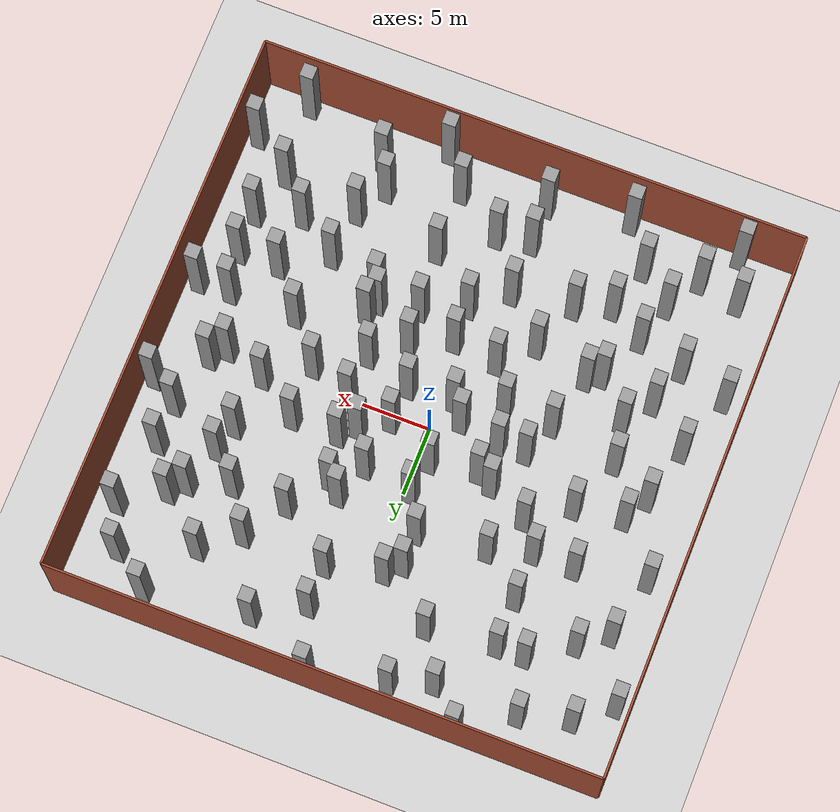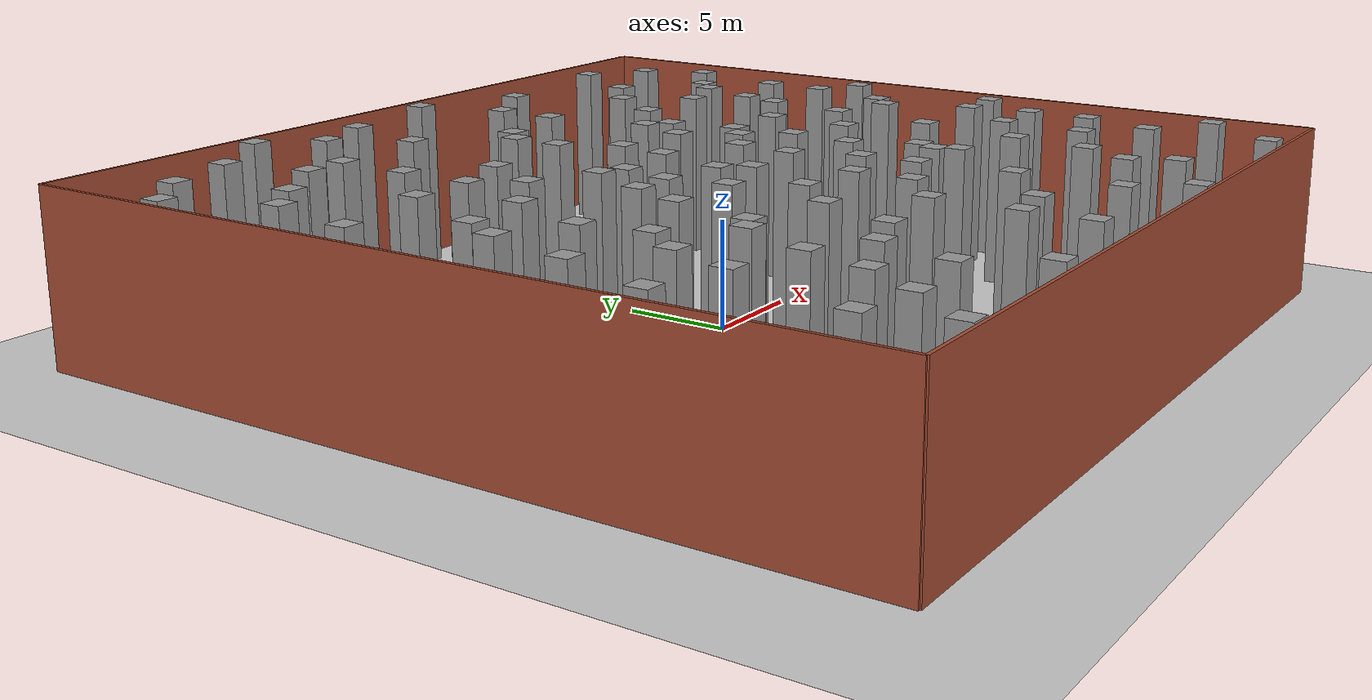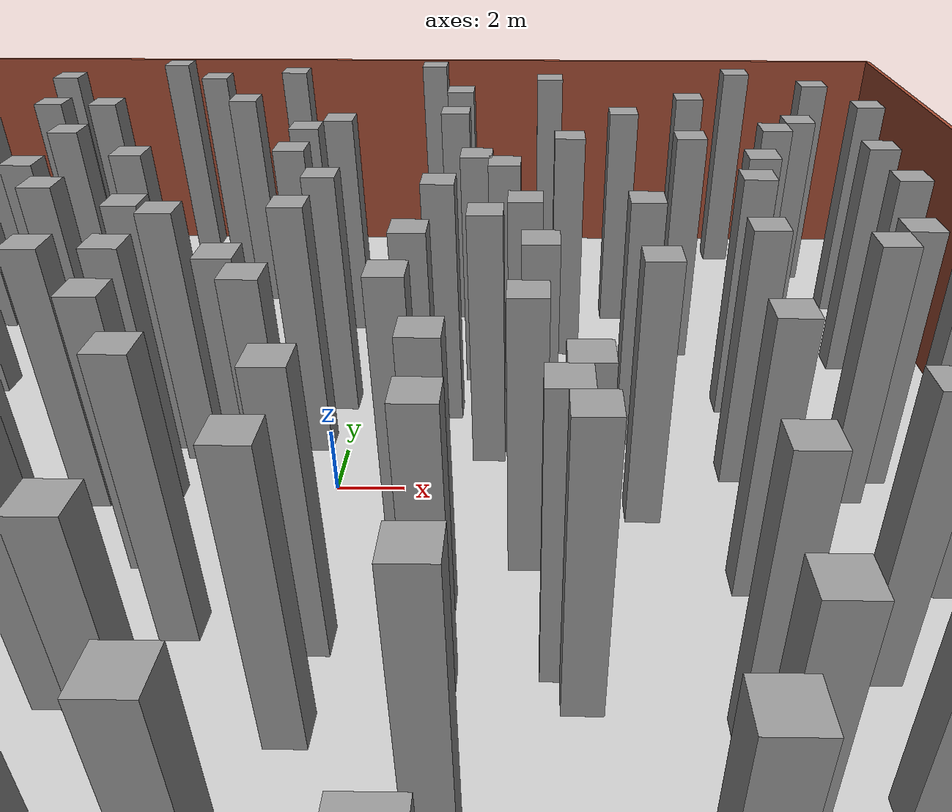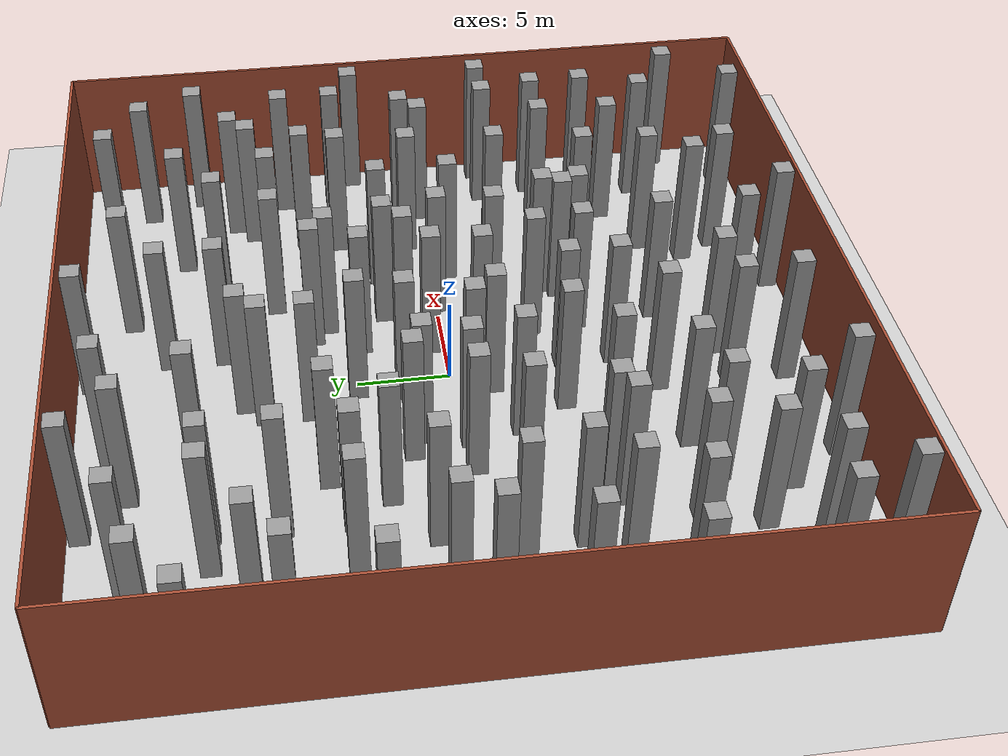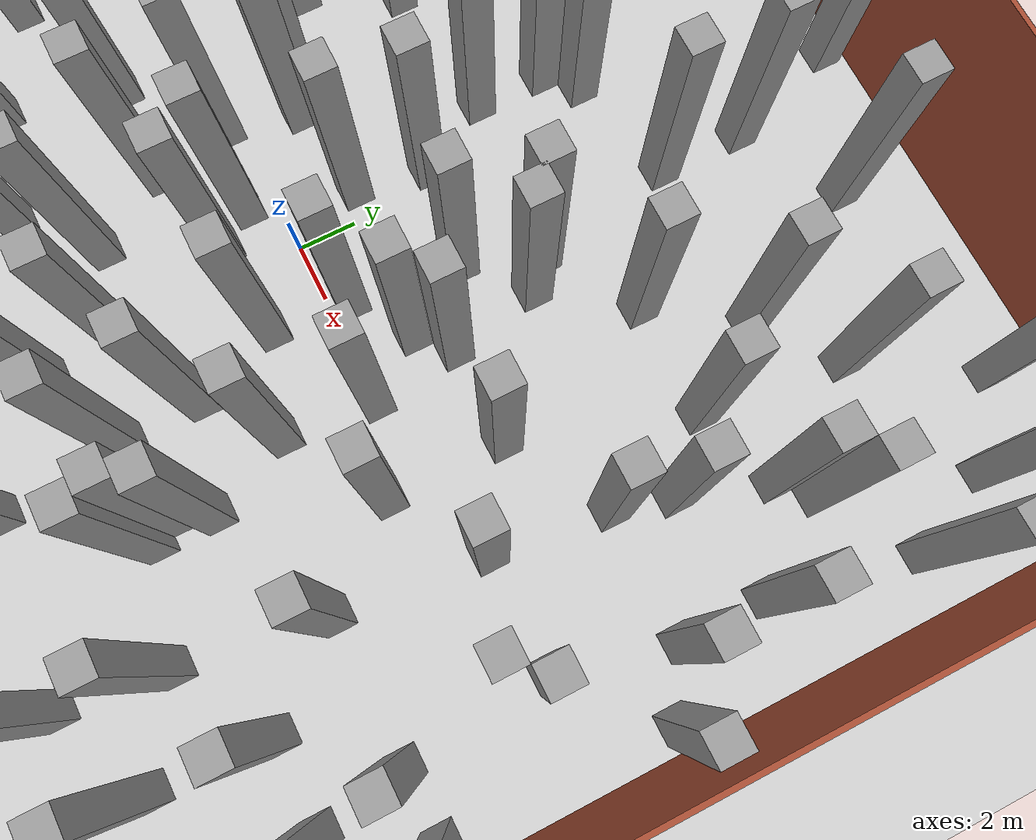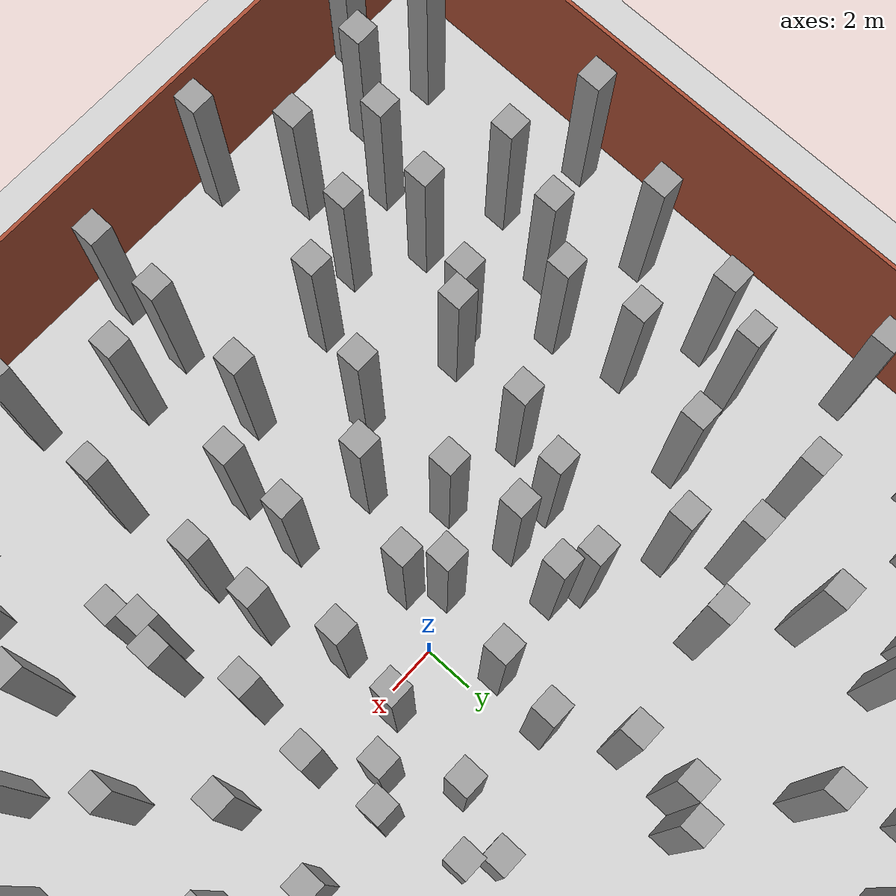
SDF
<sdf version="1.7">
 <world name="default">
  <light name="sun" type="directional">
   <pose>0 0 10 0 -0 0</pose>
   <diffuse>0.8 0.8 0.8 1</diffuse>
   <specular>0.2 0.2 0.2 1</specular>
   <attenuation>
    <range>1000</range>
    <constant>0.9</constant>
    <linear>0.01</linear>
    <quadratic>0.001</quadratic>
   </attenuation>
   <direction>-0.5 0.1 -0.9</direction>
   <spot><inner_angle>0</inner_angle><outer_angle>0</outer_angle><falloff>0</falloff></spot>
  </light>
  <model name="ground_plane">
   <static>1</static>
   <link name="link">
    <collision name="collision">
     <geometry><plane><normal>0 0 1</normal><size>100 100</size></plane></geometry>
     <surface>
      <contact><collide_bitmask>65535</collide_bitmask></contact>
      <friction><ode><mu>100</mu><mu2>50</mu2></ode></friction>
     </surface>
    </collision>
    <visual name="visual">
     <cast_shadows>0</cast_shadows>
     <geometry><plane><normal>0 0 1</normal><size>100 100</size></plane></geometry>
     <material>
      <script><uri>file://media/materials/scripts/gazebo.material</uri><name>Gazebo/Grey</name></script>
     </material>
    </visual>
   </link>
  </model>
  <gravity>0 0 -9.8</gravity>
  <magnetic_field>6e-06 2.3e-05 -4.2e-05</magnetic_field>
  <atmosphere type="adiabatic"/>
  <physics type="ode">
   <max_step_size>0.001</max_step_size>
   <real_time_factor>1</real_time_factor>
   <real_time_update_rate>1000</real_time_update_rate>
  </physics>
  <scene><ambient>0.4 0.4 0.4 1</ambient><background>0.7 0.7 0.7 1</background><shadows>1</shadows></scene>
  <spherical_coordinates>
   <surface_model>EARTH_WGS84</surface_model>
   <latitude_deg>0</latitude_deg>
   <longitude_deg>0</longitude_deg>
   <elevation>0</elevation>
   <heading_deg>0</heading_deg>
  </spherical_coordinates>
  <model name="sim_room_square">
   <link name="Wall_14">
    <collision name="Wall_14_Collision">
     <geometry><box><size>40 0.15 8</size></box></geometry>
     <pose>0 0 4 0 -0 0</pose>
    </collision>
    <visual name="Wall_14_Visual">
     <pose>0 0 4 0 -0 0</pose>
     <geometry><box><size>40 0.15 8</size></box></geometry>
     <material>
      <script><uri>file://media/materials/scripts/gazebo.material</uri><name>Gazebo/Bricks</name></script>
      <ambient>1 1 1 1</ambient>
     </material>
     <meta><layer>0</layer></meta>
    </visual>
    <pose>20 -0 0 0 -0 -1.5708</pose>
   </link>
   <link name="Wall_15">
    <collision name="Wall_15_Collision">
     <geometry><box><size>40 0.15 8</size></box></geometry>
     <pose>0 0 4 0 -0 0</pose>
    </collision>
    <visual name="Wall_15_Visual">
     <pose>0 0 4 0 -0 0</pose>
     <geometry><box><size>40 0.15 8</size></box></geometry>
     <material>
      <script><uri>file://media/materials/scripts/gazebo.material</uri><name>Gazebo/Bricks</name></script>
      <ambient>1 1 1 1</ambient>
     </material>
     <meta><layer>0</layer></meta>
    </visual>
    <pose>0 -20 0 0 -0 3.14159</pose>
   </link>
   <link name="Wall_16">
    <collision name="Wall_16_Collision">
     <geometry><box><size>40 0.15 8</size></box></geometry>
     <pose>0 0 4 0 -0 0</pose>
    </collision>
    <visual name="Wall_16_Visual">
     <pose>0 0 4 0 -0 0</pose>
     <geometry><box><size>40 0.15 8</size></box></geometry>
     <material>
      <script><uri>file://media/materials/scripts/gazebo.material</uri><name>Gazebo/Bricks</name></script>
      <ambient>1 1 1 1</ambient>
     </material>
     <meta><layer>0</layer></meta>
    </visual>
    <pose>-20 -0 0 0 -0 1.5708</pose>
   </link>
   <link name="Wall_19">
    <collision name="Wall_19_Collision">
     <geometry><box><size>40 0.15 8</size></box></geometry>
     <pose>0 0 4 0 -0 0</pose>
    </collision>
    <visual name="Wall_19_Visual">
     <pose>0 0 4 0 -0 0</pose>
     <geometry><box><size>40 0.15 8</size></box></geometry>
     <material>
      <script><uri>file://media/materials/scripts/gazebo.material</uri><name>Gazebo/Bricks</name></script>
      <ambient>1 1 1 1</ambient>
     </material>
     <meta><layer>0</layer></meta>
    </visual>
    <pose>0 20 0 0 -0 0</pose>
   </link>
   <static>1</static>
  </model>
  <model name="unit_box_static95_clone_52_clone_clone">
   <link name="link">
    <inertial>
     <mass>1</mass>
     <inertia>
      <ixx>0.166667</ixx>
      <ixy>0</ixy>
      <ixz>0</ixz>
      <iyy>0.166667</iyy>
      <iyz>0</iyz>
      <izz>0.166667</izz>
     </inertia>
    </inertial>
    <visual name="visual">
     <geometry><box><size>1 1 8</size></box></geometry>
     <material>
      <script><name>Gazebo/Grey</name><uri>file://media/materials/scripts/gazebo.material</uri></script>
      <shader type="pixel"/>
     </material>
    </visual>
    <collision name="collision">
     <geometry><box><size>1 1 8</size></box></geometry>
     <surface>
      <friction>
       <ode><mu>1</mu><mu2>1</mu2><fdir1>0 0 0</fdir1><slip1>0</slip1><slip2>0</slip2></ode>
       <torsional>
        <coefficient>1</coefficient>
        <patch_radius>0</patch_radius>
        <surface_radius>0</surface_radius>
        <use_patch_radius>1</use_patch_radius>
        <ode><slip>0</slip></ode>
       </torsional>
      </friction>
      <bounce><restitution_coefficient>0</restitution_coefficient><threshold>1e+06</threshold></bounce>
      <contact>
       <collide_without_contact>0</collide_without_contact>
       <collide_without_contact_bitmask>1</collide_without_contact_bitmask>
       <collide_bitmask>1</collide_bitmask>
       <ode>
        <soft_cfm>0</soft_cfm>
        <soft_erp>0.2</soft_erp>
        <kp>1e+13</kp>
        <kd>1</kd>
        <max_vel>0.01</max_vel>
        <min_depth>0</min_depth>
       </ode>
       <bullet>
        <split_impulse>1</split_impulse>
        <split_impulse_penetration_threshold>-0.01</split_impulse_penetration_threshold>
        <soft_cfm>0</soft_cfm>
        <soft_erp>0.2</soft_erp>
        <kp>1e+13</kp>
        <kd>1</kd>
       </bullet>
      </contact>
     </surface>
    </collision>
   </link>
   <static>1</static>
   <pose>3 4.46583 4 0 -0 0</pose>
  </model>
  <model name="unit_box_static95_clone_52_clone_clone_0">
   <link name="link">
    <inertial>
     <mass>1</mass>
     <inertia>
      <ixx>0.166667</ixx>
      <ixy>0</ixy>
      <ixz>0</ixz>
      <iyy>0.166667</iyy>
      <iyz>0</iyz>
      <izz>0.166667</izz>
     </inertia>
    </inertial>
    <visual name="visual">
     <geometry><box><size>1 1 8</size></box></geometry>
     <material>
      <script><name>Gazebo/Grey</name><uri>file://media/materials/scripts/gazebo.material</uri></script>
      <shader type="pixel"/>
     </material>
    </visual>
    <collision name="collision">
     <geometry><box><size>1 1 8</size></box></geometry>
     <surface>
      <friction>
       <ode><mu>1</mu><mu2>1</mu2><fdir1>0 0 0</fdir1><slip1>0</slip1><slip2>0</slip2></ode>
       <torsional>
        <coefficient>1</coefficient>
        <patch_radius>0</patch_radius>
        <surface_radius>0</surface_radius>
        <use_patch_radius>1</use_patch_radius>
        <ode><slip>0</slip></ode>
       </torsional>
      </friction>
      <bounce><restitution_coefficient>0</restitution_coefficient><threshold>1e+06</threshold></bounce>
      <contact>
       <collide_without_contact>0</collide_without_contact>
       <collide_without_contact_bitmask>1</collide_without_contact_bitmask>
       <collide_bitmask>1</collide_bitmask>
       <ode>
        <soft_cfm>0</soft_cfm>
        <soft_erp>0.2</soft_erp>
        <kp>1e+13</kp>
        <kd>1</kd>
        <max_vel>0.01</max_vel>
        <min_depth>0</min_depth>
       </ode>
       <bullet>
        <split_impulse>1</split_impulse>
        <split_impulse_penetration_threshold>-0.01</split_impulse_penetration_threshold>
        <soft_cfm>0</soft_cfm>
        <soft_erp>0.2</soft_erp>
        <kp>1e+13</kp>
        <kd>1</kd>
       </bullet>
      </contact>
     </surface>
    </collision>
   </link>
   <static>1</static>
   <pose>-0.575145 5 4 0 -0 0</pose>
  </model>
  <model name="unit_box_static95_clone_52_clone_clone_1">
   <link name="link">
    <inertial>
     <mass>1</mass>
     <inertia>
      <ixx>0.166667</ixx>
      <ixy>0</ixy>
      <ixz>0</ixz>
      <iyy>0.166667</iyy>
      <iyz>0</iyz>
      <izz>0.166667</izz>
     </inertia>
    </inertial>
    <visual name="visual">
     <geometry><box><size>1 1 8</size></box></geometry>
     <material>
      <script><name>Gazebo/Grey</name><uri>file://media/materials/scripts/gazebo.material</uri></script>
      <shader type="pixel"/>
     </material>
    </visual>
    <collision name="collision">
     <geometry><box><size>1 1 8</size></box></geometry>
     <surface>
      <friction>
       <ode><mu>1</mu><mu2>1</mu2><fdir1>0 0 0</fdir1><slip1>0</slip1><slip2>0</slip2></ode>
       <torsional>
        <coefficient>1</coefficient>
        <patch_radius>0</patch_radius>
        <surface_radius>0</surface_radius>
        <use_patch_radius>1</use_patch_radius>
        <ode><slip>0</slip></ode>
       </torsional>
      </friction>
      <bounce><restitution_coefficient>0</restitution_coefficient><threshold>1e+06</threshold></bounce>
      <contact>
       <collide_without_contact>0</collide_without_contact>
       <collide_without_contact_bitmask>1</collide_without_contact_bitmask>
       <collide_bitmask>1</collide_bitmask>
       <ode>
        <soft_cfm>0</soft_cfm>
        <soft_erp>0.2</soft_erp>
        <kp>1e+13</kp>
        <kd>1</kd>
        <max_vel>0.01</max_vel>
        <min_depth>0</min_depth>
       </ode>
       <bullet>
        <split_impulse>1</split_impulse>
        <split_impulse_penetration_threshold>-0.01</split_impulse_penetration_threshold>
        <soft_cfm>0</soft_cfm>
        <soft_erp>0.2</soft_erp>
        <kp>1e+13</kp>
        <kd>1</kd>
       </bullet>
      </contact>
     </surface>
    </collision>
   </link>
   <static>1</static>
   <pose>-2 7.57838 4 0 -0 0</pose>
  </model>
  <model name="unit_box_static95_clone_52_clone_clone_2">
   <link name="link">
    <inertial>
     <mass>1</mass>
     <inertia>
      <ixx>0.166667</ixx>
      <ixy>0</ixy>
      <ixz>0</ixz>
      <iyy>0.166667</iyy>
      <iyz>0</iyz>
      <izz>0.166667</izz>
     </inertia>
    </inertial>
    <visual name="visual">
     <geometry><box><size>1 1 8</size></box></geometry>
     <material>
      <script><name>Gazebo/Grey</name><uri>file://media/materials/scripts/gazebo.material</uri></script>
      <shader type="pixel"/>
     </material>
    </visual>
    <collision name="collision">
     <geometry><box><size>1 1 8</size></box></geometry>
     <surface>
      <friction>
       <ode><mu>1</mu><mu2>1</mu2><fdir1>0 0 0</fdir1><slip1>0</slip1><slip2>0</slip2></ode>
       <torsional>
        <coefficient>1</coefficient>
        <patch_radius>0</patch_radius>
        <surface_radius>0</surface_radius>
        <use_patch_radius>1</use_patch_radius>
        <ode><slip>0</slip></ode>
       </torsional>
      </friction>
      <bounce><restitution_coefficient>0</restitution_coefficient><threshold>1e+06</threshold></bounce>
      <contact>
       <collide_without_contact>0</collide_without_contact>
       <collide_without_contact_bitmask>1</collide_without_contact_bitmask>
       <collide_bitmask>1</collide_bitmask>
       <ode>
        <soft_cfm>0</soft_cfm>
        <soft_erp>0.2</soft_erp>
        <kp>1e+13</kp>
        <kd>1</kd>
        <max_vel>0.01</max_vel>
        <min_depth>0</min_depth>
       </ode>
       <bullet>
        <split_impulse>1</split_impulse>
        <split_impulse_penetration_threshold>-0.01</split_impulse_penetration_threshold>
        <soft_cfm>0</soft_cfm>
        <soft_erp>0.2</soft_erp>
        <kp>1e+13</kp>
        <kd>1</kd>
       </bullet>
      </contact>
     </surface>
    </collision>
   </link>
   <static>1</static>
   <pose>-7 7 4 0 -0 0</pose>
  </model>
  <model name="unit_box_static95_clone_52_clone_clone_3">
   <link name="link">
    <inertial>
     <mass>1</mass>
     <inertia>
      <ixx>0.166667</ixx>
      <ixy>0</ixy>
      <ixz>0</ixz>
      <iyy>0.166667</iyy>
      <iyz>0</iyz>
      <izz>0.166667</izz>
     </inertia>
    </inertial>
    <visual name="visual">
     <geometry><box><size>1 1 8</size></box></geometry>
     <material>
      <script><name>Gazebo/Grey</name><uri>file://media/materials/scripts/gazebo.material</uri></script>
      <shader type="pixel"/>
     </material>
    </visual>
    <collision name="collision">
     <geometry><box><size>1 1 8</size></box></geometry>
     <surface>
      <friction>
       <ode><mu>1</mu><mu2>1</mu2><fdir1>0 0 0</fdir1><slip1>0</slip1><slip2>0</slip2></ode>
       <torsional>
        <coefficient>1</coefficient>
        <patch_radius>0</patch_radius>
        <surface_radius>0</surface_radius>
        <use_patch_radius>1</use_patch_radius>
        <ode><slip>0</slip></ode>
       </torsional>
      </friction>
      <bounce><restitution_coefficient>0</restitution_coefficient><threshold>1e+06</threshold></bounce>
      <contact>
       <collide_without_contact>0</collide_without_contact>
       <collide_without_contact_bitmask>1</collide_without_contact_bitmask>
       <collide_bitmask>1</collide_bitmask>
       <ode>
        <soft_cfm>0</soft_cfm>
        <soft_erp>0.2</soft_erp>
        <kp>1e+13</kp>
        <kd>1</kd>
        <max_vel>0.01</max_vel>
        <min_depth>0</min_depth>
       </ode>
       <bullet>
        <split_impulse>1</split_impulse>
        <split_impulse_penetration_threshold>-0.01</split_impulse_penetration_threshold>
        <soft_cfm>0</soft_cfm>
        <soft_erp>0.2</soft_erp>
        <kp>1e+13</kp>
        <kd>1</kd>
       </bullet>
      </contact>
     </surface>
    </collision>
   </link>
   <static>1</static>
   <pose>-5.58229 2.57124 4 0 -0 0</pose>
  </model>
  <model name="unit_box_static95_clone_52_clone_clone_4">
   <link name="link">
    <inertial>
     <mass>1</mass>
     <inertia>
      <ixx>0.166667</ixx>
      <ixy>0</ixy>
      <ixz>0</ixz>
      <iyy>0.166667</iyy>
      <iyz>0</iyz>
      <izz>0.166667</izz>
     </inertia>
    </inertial>
    <visual name="visual">
     <geometry><box><size>1 1 8</size></box></geometry>
     <material>
      <script><name>Gazebo/Grey</name><uri>file://media/materials/scripts/gazebo.material</uri></script>
      <shader type="pixel"/>
     </material>
    </visual>
    <collision name="collision">
     <geometry><box><size>1 1 8</size></box></geometry>
     <surface>
      <friction>
       <ode><mu>1</mu><mu2>1</mu2><fdir1>0 0 0</fdir1><slip1>0</slip1><slip2>0</slip2></ode>
       <torsional>
        <coefficient>1</coefficient>
        <patch_radius>0</patch_radius>
        <surface_radius>0</surface_radius>
        <use_patch_radius>1</use_patch_radius>
        <ode><slip>0</slip></ode>
       </torsional>
      </friction>
      <bounce><restitution_coefficient>0</restitution_coefficient><threshold>1e+06</threshold></bounce>
      <contact>
       <collide_without_contact>0</collide_without_contact>
       <collide_without_contact_bitmask>1</collide_without_contact_bitmask>
       <collide_bitmask>1</collide_bitmask>
       <ode>
        <soft_cfm>0</soft_cfm>
        <soft_erp>0.2</soft_erp>
        <kp>1e+13</kp>
        <kd>1</kd>
        <max_vel>0.01</max_vel>
        <min_depth>0</min_depth>
       </ode>
       <bullet>
        <split_impulse>1</split_impulse>
        <split_impulse_penetration_threshold>-0.01</split_impulse_penetration_threshold>
        <soft_cfm>0</soft_cfm>
        <soft_erp>0.2</soft_erp>
        <kp>1e+13</kp>
        <kd>1</kd>
       </bullet>
      </contact>
     </surface>
    </collision>
   </link>
   <static>1</static>
   <pose>-8.55951 4 4 0 -0 0</pose>
  </model>
  <model name="unit_box_static95_clone_52_clone_clone_5">
   <link name="link">
    <inertial>
     <mass>1</mass>
     <inertia>
      <ixx>0.166667</ixx>
      <ixy>0</ixy>
      <ixz>0</ixz>
      <iyy>0.166667</iyy>
      <iyz>0</iyz>
      <izz>0.166667</izz>
     </inertia>
    </inertial>
    <visual name="visual">
     <geometry><box><size>1 1 8</size></box></geometry>
     <material>
      <script><name>Gazebo/Grey</name><uri>file://media/materials/scripts/gazebo.material</uri></script>
      <shader type="pixel"/>
     </material>
    </visual>
    <collision name="collision">
     <geometry><box><size>1 1 8</size></box></geometry>
     <surface>
      <friction>
       <ode><mu>1</mu><mu2>1</mu2><fdir1>0 0 0</fdir1><slip1>0</slip1><slip2>0</slip2></ode>
       <torsional>
        <coefficient>1</coefficient>
        <patch_radius>0</patch_radius>
        <surface_radius>0</surface_radius>
        <use_patch_radius>1</use_patch_radius>
        <ode><slip>0</slip></ode>
       </torsional>
      </friction>
      <bounce><restitution_coefficient>0</restitution_coefficient><threshold>1e+06</threshold></bounce>
      <contact>
       <collide_without_contact>0</collide_without_contact>
       <collide_without_contact_bitmask>1</collide_without_contact_bitmask>
       <collide_bitmask>1</collide_bitmask>
       <ode>
        <soft_cfm>0</soft_cfm>
        <soft_erp>0.2</soft_erp>
        <kp>1e+13</kp>
        <kd>1</kd>
        <max_vel>0.01</max_vel>
        <min_depth>0</min_depth>
       </ode>
       <bullet>
        <split_impulse>1</split_impulse>
        <split_impulse_penetration_threshold>-0.01</split_impulse_penetration_threshold>
        <soft_cfm>0</soft_cfm>
        <soft_erp>0.2</soft_erp>
        <kp>1e+13</kp>
        <kd>1</kd>
       </bullet>
      </contact>
     </surface>
    </collision>
   </link>
   <static>1</static>
   <pose>-11.4691 2 4 0 -0 0</pose>
  </model>
  <model name="unit_box_static95_clone_52_clone_clone_6">
   <link name="link">
    <inertial>
     <mass>1</mass>
     <inertia>
      <ixx>0.166667</ixx>
      <ixy>0</ixy>
      <ixz>0</ixz>
      <iyy>0.166667</iyy>
      <iyz>0</iyz>
      <izz>0.166667</izz>
     </inertia>
    </inertial>
    <visual name="visual">
     <geometry><box><size>1 1 8</size></box></geometry>
     <material>
      <script><name>Gazebo/Grey</name><uri>file://media/materials/scripts/gazebo.material</uri></script>
      <shader type="pixel"/>
     </material>
    </visual>
    <collision name="collision">
     <geometry><box><size>1 1 8</size></box></geometry>
     <surface>
      <friction>
       <ode><mu>1</mu><mu2>1</mu2><fdir1>0 0 0</fdir1><slip1>0</slip1><slip2>0</slip2></ode>
       <torsional>
        <coefficient>1</coefficient>
        <patch_radius>0</patch_radius>
        <surface_radius>0</surface_radius>
        <use_patch_radius>1</use_patch_radius>
        <ode><slip>0</slip></ode>
       </torsional>
      </friction>
      <bounce><restitution_coefficient>0</restitution_coefficient><threshold>1e+06</threshold></bounce>
      <contact>
       <collide_without_contact>0</collide_without_contact>
       <collide_without_contact_bitmask>1</collide_without_contact_bitmask>
       <collide_bitmask>1</collide_bitmask>
       <ode>
        <soft_cfm>0</soft_cfm>
        <soft_erp>0.2</soft_erp>
        <kp>1e+13</kp>
        <kd>1</kd>
        <max_vel>0.01</max_vel>
        <min_depth>0</min_depth>
       </ode>
       <bullet>
        <split_impulse>1</split_impulse>
        <split_impulse_penetration_threshold>-0.01</split_impulse_penetration_threshold>
        <soft_cfm>0</soft_cfm>
        <soft_erp>0.2</soft_erp>
        <kp>1e+13</kp>
        <kd>1</kd>
       </bullet>
      </contact>
     </surface>
    </collision>
   </link>
   <static>1</static>
   <pose>-13 6 4 0 -0 0</pose>
  </model>
  <model name="unit_box_static95_clone_52_clone_clone_7">
   <link name="link">
    <inertial>
     <mass>1</mass>
     <inertia>
      <ixx>0.166667</ixx>
      <ixy>0</ixy>
      <ixz>0</ixz>
      <iyy>0.166667</iyy>
      <iyz>0</iyz>
      <izz>0.166667</izz>
     </inertia>
    </inertial>
    <visual name="visual">
     <geometry><box><size>1 1 8</size></box></geometry>
     <material>
      <script><name>Gazebo/Grey</name><uri>file://media/materials/scripts/gazebo.material</uri></script>
      <shader type="pixel"/>
     </material>
    </visual>
    <collision name="collision">
     <geometry><box><size>1 1 8</size></box></geometry>
     <surface>
      <friction>
       <ode><mu>1</mu><mu2>1</mu2><fdir1>0 0 0</fdir1><slip1>0</slip1><slip2>0</slip2></ode>
       <torsional>
        <coefficient>1</coefficient>
        <patch_radius>0</patch_radius>
        <surface_radius>0</surface_radius>
        <use_patch_radius>1</use_patch_radius>
        <ode><slip>0</slip></ode>
       </torsional>
      </friction>
      <bounce><restitution_coefficient>0</restitution_coefficient><threshold>1e+06</threshold></bounce>
      <contact>
       <collide_without_contact>0</collide_without_contact>
       <collide_without_contact_bitmask>1</collide_without_contact_bitmask>
       <collide_bitmask>1</collide_bitmask>
       <ode>
        <soft_cfm>0</soft_cfm>
        <soft_erp>0.2</soft_erp>
        <kp>1e+13</kp>
        <kd>1</kd>
        <max_vel>0.01</max_vel>
        <min_depth>0</min_depth>
       </ode>
       <bullet>
        <split_impulse>1</split_impulse>
        <split_impulse_penetration_threshold>-0.01</split_impulse_penetration_threshold>
        <soft_cfm>0</soft_cfm>
        <soft_erp>0.2</soft_erp>
        <kp>1e+13</kp>
        <kd>1</kd>
       </bullet>
      </contact>
     </surface>
    </collision>
   </link>
   <static>1</static>
   <pose>-10 6 4 0 -0 0</pose>
  </model>
  <model name="unit_box_static95_clone_52_clone_clone_9">
   <link name="link">
    <inertial>
     <mass>1</mass>
     <inertia>
      <ixx>0.166667</ixx>
      <ixy>0</ixy>
      <ixz>0</ixz>
      <iyy>0.166667</iyy>
      <iyz>0</iyz>
      <izz>0.166667</izz>
     </inertia>
    </inertial>
    <visual name="visual">
     <geometry><box><size>1 1 8</size></box></geometry>
     <material>
      <script><name>Gazebo/Grey</name><uri>file://media/materials/scripts/gazebo.material</uri></script>
      <shader type="pixel"/>
     </material>
    </visual>
    <collision name="collision">
     <geometry><box><size>1 1 8</size></box></geometry>
     <surface>
      <friction>
       <ode><mu>1</mu><mu2>1</mu2><fdir1>0 0 0</fdir1><slip1>0</slip1><slip2>0</slip2></ode>
       <torsional>
        <coefficient>1</coefficient>
        <patch_radius>0</patch_radius>
        <surface_radius>0</surface_radius>
        <use_patch_radius>1</use_patch_radius>
        <ode><slip>0</slip></ode>
       </torsional>
      </friction>
      <bounce><restitution_coefficient>0</restitution_coefficient><threshold>1e+06</threshold></bounce>
      <contact>
       <collide_without_contact>0</collide_without_contact>
       <collide_without_contact_bitmask>1</collide_without_contact_bitmask>
       <collide_bitmask>1</collide_bitmask>
       <ode>
        <soft_cfm>0</soft_cfm>
        <soft_erp>0.2</soft_erp>
        <kp>1e+13</kp>
        <kd>1</kd>
        <max_vel>0.01</max_vel>
        <min_depth>0</min_depth>
       </ode>
       <bullet>
        <split_impulse>1</split_impulse>
        <split_impulse_penetration_threshold>-0.01</split_impulse_penetration_threshold>
        <soft_cfm>0</soft_cfm>
        <soft_erp>0.2</soft_erp>
        <kp>1e+13</kp>
        <kd>1</kd>
       </bullet>
      </contact>
     </surface>
    </collision>
   </link>
   <static>1</static>
   <pose>-10 9.47298 4 0 -0 0</pose>
  </model>
  <model name="unit_box_static95_clone_52_clone_clone_12">
   <link name="link">
    <inertial>
     <mass>1</mass>
     <inertia>
      <ixx>0.166667</ixx>
      <ixy>0</ixy>
      <ixz>0</ixz>
      <iyy>0.166667</iyy>
      <iyz>0</iyz>
      <izz>0.166667</izz>
     </inertia>
    </inertial>
    <visual name="visual">
     <geometry><box><size>1 1 8</size></box></geometry>
     <material>
      <script><name>Gazebo/Grey</name><uri>file://media/materials/scripts/gazebo.material</uri></script>
      <shader type="pixel"/>
     </material>
    </visual>
    <collision name="collision">
     <geometry><box><size>1 1 8</size></box></geometry>
     <surface>
      <friction>
       <ode><mu>1</mu><mu2>1</mu2><fdir1>0 0 0</fdir1><slip1>0</slip1><slip2>0</slip2></ode>
       <torsional>
        <coefficient>1</coefficient>
        <patch_radius>0</patch_radius>
        <surface_radius>0</surface_radius>
        <use_patch_radius>1</use_patch_radius>
        <ode><slip>0</slip></ode>
       </torsional>
      </friction>
      <bounce><restitution_coefficient>0</restitution_coefficient><threshold>1e+06</threshold></bounce>
      <contact>
       <collide_without_contact>0</collide_without_contact>
       <collide_without_contact_bitmask>1</collide_without_contact_bitmask>
       <collide_bitmask>1</collide_bitmask>
       <ode>
        <soft_cfm>0</soft_cfm>
        <soft_erp>0.2</soft_erp>
        <kp>1e+13</kp>
        <kd>1</kd>
        <max_vel>0.01</max_vel>
        <min_depth>0</min_depth>
       </ode>
       <bullet>
        <split_impulse>1</split_impulse>
        <split_impulse_penetration_threshold>-0.01</split_impulse_penetration_threshold>
        <soft_cfm>0</soft_cfm>
        <soft_erp>0.2</soft_erp>
        <kp>1e+13</kp>
        <kd>1</kd>
       </bullet>
      </contact>
     </surface>
    </collision>
   </link>
   <static>1</static>
   <pose>-2 10 4 0 -0 0</pose>
  </model>
  <model name="unit_box_static95_clone_52_clone_clone_14">
   <link name="link">
    <inertial>
     <mass>1</mass>
     <inertia>
      <ixx>0.166667</ixx>
      <ixy>0</ixy>
      <ixz>0</ixz>
      <iyy>0.166667</iyy>
      <iyz>0</iyz>
      <izz>0.166667</izz>
     </inertia>
    </inertial>
    <visual name="visual">
     <geometry><box><size>1 1 8</size></box></geometry>
     <material>
      <script><name>Gazebo/Grey</name><uri>file://media/materials/scripts/gazebo.material</uri></script>
      <shader type="pixel"/>
     </material>
    </visual>
    <collision name="collision">
     <geometry><box><size>1 1 8</size></box></geometry>
     <surface>
      <friction>
       <ode><mu>1</mu><mu2>1</mu2><fdir1>0 0 0</fdir1><slip1>0</slip1><slip2>0</slip2></ode>
       <torsional>
        <coefficient>1</coefficient>
        <patch_radius>0</patch_radius>
        <surface_radius>0</surface_radius>
        <use_patch_radius>1</use_patch_radius>
        <ode><slip>0</slip></ode>
       </torsional>
      </friction>
      <bounce><restitution_coefficient>0</restitution_coefficient><threshold>1e+06</threshold></bounce>
      <contact>
       <collide_without_contact>0</collide_without_contact>
       <collide_without_contact_bitmask>1</collide_without_contact_bitmask>
       <collide_bitmask>1</collide_bitmask>
       <ode>
        <soft_cfm>0</soft_cfm>
        <soft_erp>0.2</soft_erp>
        <kp>1e+13</kp>
        <kd>1</kd>
        <max_vel>0.01</max_vel>
        <min_depth>0</min_depth>
       </ode>
       <bullet>
        <split_impulse>1</split_impulse>
        <split_impulse_penetration_threshold>-0.01</split_impulse_penetration_threshold>
        <soft_cfm>0</soft_cfm>
        <soft_erp>0.2</soft_erp>
        <kp>1e+13</kp>
        <kd>1</kd>
       </bullet>
      </contact>
     </surface>
    </collision>
   </link>
   <static>1</static>
   <pose>5.58229 3 4 0 -0 0</pose>
  </model>
  <model name="unit_box_static95_clone_52_clone_clone_15">
   <link name="link">
    <inertial>
     <mass>1</mass>
     <inertia>
      <ixx>0.166667</ixx>
      <ixy>0</ixy>
      <ixz>0</ixz>
      <iyy>0.166667</iyy>
      <iyz>0</iyz>
      <izz>0.166667</izz>
     </inertia>
    </inertial>
    <visual name="visual">
     <geometry><box><size>1 1 8</size></box></geometry>
     <material>
      <script><name>Gazebo/Grey</name><uri>file://media/materials/scripts/gazebo.material</uri></script>
      <shader type="pixel"/>
     </material>
    </visual>
    <collision name="collision">
     <geometry><box><size>1 1 8</size></box></geometry>
     <surface>
      <friction>
       <ode><mu>1</mu><mu2>1</mu2><fdir1>0 0 0</fdir1><slip1>0</slip1><slip2>0</slip2></ode>
       <torsional>
        <coefficient>1</coefficient>
        <patch_radius>0</patch_radius>
        <surface_radius>0</surface_radius>
        <use_patch_radius>1</use_patch_radius>
        <ode><slip>0</slip></ode>
       </torsional>
      </friction>
      <bounce><restitution_coefficient>0</restitution_coefficient><threshold>1e+06</threshold></bounce>
      <contact>
       <collide_without_contact>0</collide_without_contact>
       <collide_without_contact_bitmask>1</collide_without_contact_bitmask>
       <collide_bitmask>1</collide_bitmask>
       <ode>
        <soft_cfm>0</soft_cfm>
        <soft_erp>0.2</soft_erp>
        <kp>1e+13</kp>
        <kd>1</kd>
        <max_vel>0.01</max_vel>
        <min_depth>0</min_depth>
       </ode>
       <bullet>
        <split_impulse>1</split_impulse>
        <split_impulse_penetration_threshold>-0.01</split_impulse_penetration_threshold>
        <soft_cfm>0</soft_cfm>
        <soft_erp>0.2</soft_erp>
        <kp>1e+13</kp>
        <kd>1</kd>
       </bullet>
      </contact>
     </surface>
    </collision>
   </link>
   <static>1</static>
   <pose>6 0 4 0 -0 0</pose>
  </model>
  <model name="unit_box_static95_clone_52_clone_clone_17">
   <link name="link">
    <inertial>
     <mass>1</mass>
     <inertia>
      <ixx>0.166667</ixx>
      <ixy>0</ixy>
      <ixz>0</ixz>
      <iyy>0.166667</iyy>
      <iyz>0</iyz>
      <izz>0.166667</izz>
     </inertia>
    </inertial>
    <visual name="visual">
     <geometry><box><size>1 1 8</size></box></geometry>
     <material>
      <script><name>Gazebo/Grey</name><uri>file://media/materials/scripts/gazebo.material</uri></script>
      <shader type="pixel"/>
     </material>
    </visual>
    <collision name="collision">
     <geometry><box><size>1 1 8</size></box></geometry>
     <surface>
      <friction>
       <ode><mu>1</mu><mu2>1</mu2><fdir1>0 0 0</fdir1><slip1>0</slip1><slip2>0</slip2></ode>
       <torsional>
        <coefficient>1</coefficient>
        <patch_radius>0</patch_radius>
        <surface_radius>0</surface_radius>
        <use_patch_radius>1</use_patch_radius>
        <ode><slip>0</slip></ode>
       </torsional>
      </friction>
      <bounce><restitution_coefficient>0</restitution_coefficient><threshold>1e+06</threshold></bounce>
      <contact>
       <collide_without_contact>0</collide_without_contact>
       <collide_without_contact_bitmask>1</collide_without_contact_bitmask>
       <collide_bitmask>1</collide_bitmask>
       <ode>
        <soft_cfm>0</soft_cfm>
        <soft_erp>0.2</soft_erp>
        <kp>1e+13</kp>
        <kd>1</kd>
        <max_vel>0.01</max_vel>
        <min_depth>0</min_depth>
       </ode>
       <bullet>
        <split_impulse>1</split_impulse>
        <split_impulse_penetration_threshold>-0.01</split_impulse_penetration_threshold>
        <soft_cfm>0</soft_cfm>
        <soft_erp>0.2</soft_erp>
        <kp>1e+13</kp>
        <kd>1</kd>
       </bullet>
      </contact>
     </surface>
    </collision>
   </link>
   <static>1</static>
   <pose>6.52958 -7 4 0 -0 0</pose>
  </model>
  <model name="unit_box_static95_clone_52_clone_clone_18">
   <link name="link">
    <inertial>
     <mass>1</mass>
     <inertia>
      <ixx>0.166667</ixx>
      <ixy>0</ixy>
      <ixz>0</ixz>
      <iyy>0.166667</iyy>
      <iyz>0</iyz>
      <izz>0.166667</izz>
     </inertia>
    </inertial>
    <visual name="visual">
     <geometry><box><size>1 1 8</size></box></geometry>
     <material>
      <script><name>Gazebo/Grey</name><uri>file://media/materials/scripts/gazebo.material</uri></script>
      <shader type="pixel"/>
     </material>
    </visual>
    <collision name="collision">
     <geometry><box><size>1 1 8</size></box></geometry>
     <surface>
      <friction>
       <ode><mu>1</mu><mu2>1</mu2><fdir1>0 0 0</fdir1><slip1>0</slip1><slip2>0</slip2></ode>
       <torsional>
        <coefficient>1</coefficient>
        <patch_radius>0</patch_radius>
        <surface_radius>0</surface_radius>
        <use_patch_radius>1</use_patch_radius>
        <ode><slip>0</slip></ode>
       </torsional>
      </friction>
      <bounce><restitution_coefficient>0</restitution_coefficient><threshold>1e+06</threshold></bounce>
      <contact>
       <collide_without_contact>0</collide_without_contact>
       <collide_without_contact_bitmask>1</collide_without_contact_bitmask>
       <collide_bitmask>1</collide_bitmask>
       <ode>
        <soft_cfm>0</soft_cfm>
        <soft_erp>0.2</soft_erp>
        <kp>1e+13</kp>
        <kd>1</kd>
        <max_vel>0.01</max_vel>
        <min_depth>0</min_depth>
       </ode>
       <bullet>
        <split_impulse>1</split_impulse>
        <split_impulse_penetration_threshold>-0.01</split_impulse_penetration_threshold>
        <soft_cfm>0</soft_cfm>
        <soft_erp>0.2</soft_erp>
        <kp>1e+13</kp>
        <kd>1</kd>
       </bullet>
      </contact>
     </surface>
    </collision>
   </link>
   <static>1</static>
   <pose>3.40813 -5 4 0 -0 0</pose>
  </model>
  <model name="unit_box_static95_clone_52_clone_clone_19">
   <link name="link">
    <inertial>
     <mass>1</mass>
     <inertia>
      <ixx>0.166667</ixx>
      <ixy>0</ixy>
      <ixz>0</ixz>
      <iyy>0.166667</iyy>
      <iyz>0</iyz>
      <izz>0.166667</izz>
     </inertia>
    </inertial>
    <visual name="visual">
     <geometry><box><size>1 1 8</size></box></geometry>
     <material>
      <script><name>Gazebo/Grey</name><uri>file://media/materials/scripts/gazebo.material</uri></script>
      <shader type="pixel"/>
     </material>
    </visual>
    <collision name="collision">
     <geometry><box><size>1 1 8</size></box></geometry>
     <surface>
      <friction>
       <ode><mu>1</mu><mu2>1</mu2><fdir1>0 0 0</fdir1><slip1>0</slip1><slip2>0</slip2></ode>
       <torsional>
        <coefficient>1</coefficient>
        <patch_radius>0</patch_radius>
        <surface_radius>0</surface_radius>
        <use_patch_radius>1</use_patch_radius>
        <ode><slip>0</slip></ode>
       </torsional>
      </friction>
      <bounce><restitution_coefficient>0</restitution_coefficient><threshold>1e+06</threshold></bounce>
      <contact>
       <collide_without_contact>0</collide_without_contact>
       <collide_without_contact_bitmask>1</collide_without_contact_bitmask>
       <collide_bitmask>1</collide_bitmask>
       <ode>
        <soft_cfm>0</soft_cfm>
        <soft_erp>0.2</soft_erp>
        <kp>1e+13</kp>
        <kd>1</kd>
        <max_vel>0.01</max_vel>
        <min_depth>0</min_depth>
       </ode>
       <bullet>
        <split_impulse>1</split_impulse>
        <split_impulse_penetration_threshold>-0.01</split_impulse_penetration_threshold>
        <soft_cfm>0</soft_cfm>
        <soft_erp>0.2</soft_erp>
        <kp>1e+13</kp>
        <kd>1</kd>
       </bullet>
      </contact>
     </surface>
    </collision>
   </link>
   <static>1</static>
   <pose>-1.06932 -2.20283 4 0 -0 0</pose>
  </model>
  <model name="unit_box_static95_clone_52_clone_clone_20">
   <link name="link">
    <inertial>
     <mass>1</mass>
     <inertia>
      <ixx>0.166667</ixx>
      <ixy>0</ixy>
      <ixz>0</ixz>
      <iyy>0.166667</iyy>
      <iyz>0</iyz>
      <izz>0.166667</izz>
     </inertia>
    </inertial>
    <visual name="visual">
     <geometry><box><size>1 1 8</size></box></geometry>
     <material>
      <script><name>Gazebo/Grey</name><uri>file://media/materials/scripts/gazebo.material</uri></script>
      <shader type="pixel"/>
     </material>
    </visual>
    <collision name="collision">
     <geometry><box><size>1 1 8</size></box></geometry>
     <surface>
      <friction>
       <ode><mu>1</mu><mu2>1</mu2><fdir1>0 0 0</fdir1><slip1>0</slip1><slip2>0</slip2></ode>
       <torsional>
        <coefficient>1</coefficient>
        <patch_radius>0</patch_radius>
        <surface_radius>0</surface_radius>
        <use_patch_radius>1</use_patch_radius>
        <ode><slip>0</slip></ode>
       </torsional>
      </friction>
      <bounce><restitution_coefficient>0</restitution_coefficient><threshold>1e+06</threshold></bounce>
      <contact>
       <collide_without_contact>0</collide_without_contact>
       <collide_without_contact_bitmask>1</collide_without_contact_bitmask>
       <collide_bitmask>1</collide_bitmask>
       <ode>
        <soft_cfm>0</soft_cfm>
        <soft_erp>0.2</soft_erp>
        <kp>1e+13</kp>
        <kd>1</kd>
        <max_vel>0.01</max_vel>
        <min_depth>0</min_depth>
       </ode>
       <bullet>
        <split_impulse>1</split_impulse>
        <split_impulse_penetration_threshold>-0.01</split_impulse_penetration_threshold>
        <soft_cfm>0</soft_cfm>
        <soft_erp>0.2</soft_erp>
        <kp>1e+13</kp>
        <kd>1</kd>
       </bullet>
      </contact>
     </surface>
    </collision>
   </link>
   <static>1</static>
   <pose>-2.81058 -5.81659 4 0 -0 0</pose>
  </model>
  <model name="unit_box_static95_clone_52_clone_clone_21">
   <link name="link">
    <inertial>
     <mass>1</mass>
     <inertia>
      <ixx>0.166667</ixx>
      <ixy>0</ixy>
      <ixz>0</ixz>
      <iyy>0.166667</iyy>
      <iyz>0</iyz>
      <izz>0.166667</izz>
     </inertia>
    </inertial>
    <visual name="visual">
     <geometry><box><size>1 1 8</size></box></geometry>
     <material>
      <script><name>Gazebo/Grey</name><uri>file://media/materials/scripts/gazebo.material</uri></script>
      <shader type="pixel"/>
     </material>
    </visual>
    <collision name="collision">
     <geometry><box><size>1 1 8</size></box></geometry>
     <surface>
      <friction>
       <ode><mu>1</mu><mu2>1</mu2><fdir1>0 0 0</fdir1><slip1>0</slip1><slip2>0</slip2></ode>
       <torsional>
        <coefficient>1</coefficient>
        <patch_radius>0</patch_radius>
        <surface_radius>0</surface_radius>
        <use_patch_radius>1</use_patch_radius>
        <ode><slip>0</slip></ode>
       </torsional>
      </friction>
      <bounce><restitution_coefficient>0</restitution_coefficient><threshold>1e+06</threshold></bounce>
      <contact>
       <collide_without_contact>0</collide_without_contact>
       <collide_without_contact_bitmask>1</collide_without_contact_bitmask>
       <collide_bitmask>1</collide_bitmask>
       <ode>
        <soft_cfm>0</soft_cfm>
        <soft_erp>0.2</soft_erp>
        <kp>1e+13</kp>
        <kd>1</kd>
        <max_vel>0.01</max_vel>
        <min_depth>0</min_depth>
       </ode>
       <bullet>
        <split_impulse>1</split_impulse>
        <split_impulse_penetration_threshold>-0.01</split_impulse_penetration_threshold>
        <soft_cfm>0</soft_cfm>
        <soft_erp>0.2</soft_erp>
        <kp>1e+13</kp>
        <kd>1</kd>
       </bullet>
      </contact>
     </surface>
    </collision>
   </link>
   <static>1</static>
   <pose>-4.45541 -3.17541 4 0 -0 0</pose>
  </model>
  <model name="unit_box_static95_clone_52_clone_clone_22">
   <link name="link">
    <inertial>
     <mass>1</mass>
     <inertia>
      <ixx>0.166667</ixx>
      <ixy>0</ixy>
      <ixz>0</ixz>
      <iyy>0.166667</iyy>
      <iyz>0</iyz>
      <izz>0.166667</izz>
     </inertia>
    </inertial>
    <visual name="visual">
     <geometry><box><size>1 1 8</size></box></geometry>
     <material>
      <script><name>Gazebo/Grey</name><uri>file://media/materials/scripts/gazebo.material</uri></script>
      <shader type="pixel"/>
     </material>
    </visual>
    <collision name="collision">
     <geometry><box><size>1 1 8</size></box></geometry>
     <surface>
      <friction>
       <ode><mu>1</mu><mu2>1</mu2><fdir1>0 0 0</fdir1><slip1>0</slip1><slip2>0</slip2></ode>
       <torsional>
        <coefficient>1</coefficient>
        <patch_radius>0</patch_radius>
        <surface_radius>0</surface_radius>
        <use_patch_radius>1</use_patch_radius>
        <ode><slip>0</slip></ode>
       </torsional>
      </friction>
      <bounce><restitution_coefficient>0</restitution_coefficient><threshold>1e+06</threshold></bounce>
      <contact>
       <collide_without_contact>0</collide_without_contact>
       <collide_without_contact_bitmask>1</collide_without_contact_bitmask>
       <collide_bitmask>1</collide_bitmask>
       <ode>
        <soft_cfm>0</soft_cfm>
        <soft_erp>0.2</soft_erp>
        <kp>1e+13</kp>
        <kd>1</kd>
        <max_vel>0.01</max_vel>
        <min_depth>0</min_depth>
       </ode>
       <bullet>
        <split_impulse>1</split_impulse>
        <split_impulse_penetration_threshold>-0.01</split_impulse_penetration_threshold>
        <soft_cfm>0</soft_cfm>
        <soft_erp>0.2</soft_erp>
        <kp>1e+13</kp>
        <kd>1</kd>
       </bullet>
      </contact>
     </surface>
    </collision>
   </link>
   <static>1</static>
   <pose>-8 -3 4 0 -0 0</pose>
  </model>
  <model name="unit_box_static95_clone_52_clone_clone_25">
   <link name="link">
    <inertial>
     <mass>1</mass>
     <inertia>
      <ixx>0.166667</ixx>
      <ixy>0</ixy>
      <ixz>0</ixz>
      <iyy>0.166667</iyy>
      <iyz>0</iyz>
      <izz>0.166667</izz>
     </inertia>
    </inertial>
    <visual name="visual">
     <geometry><box><size>1 1 8</size></box></geometry>
     <material>
      <script><name>Gazebo/Grey</name><uri>file://media/materials/scripts/gazebo.material</uri></script>
      <shader type="pixel"/>
     </material>
    </visual>
    <collision name="collision">
     <geometry><box><size>1 1 8</size></box></geometry>
     <surface>
      <friction>
       <ode><mu>1</mu><mu2>1</mu2><fdir1>0 0 0</fdir1><slip1>0</slip1><slip2>0</slip2></ode>
       <torsional>
        <coefficient>1</coefficient>
        <patch_radius>0</patch_radius>
        <surface_radius>0</surface_radius>
        <use_patch_radius>1</use_patch_radius>
        <ode><slip>0</slip></ode>
       </torsional>
      </friction>
      <bounce><restitution_coefficient>0</restitution_coefficient><threshold>1e+06</threshold></bounce>
      <contact>
       <collide_without_contact>0</collide_without_contact>
       <collide_without_contact_bitmask>1</collide_without_contact_bitmask>
       <collide_bitmask>1</collide_bitmask>
       <ode>
        <soft_cfm>0</soft_cfm>
        <soft_erp>0.2</soft_erp>
        <kp>1e+13</kp>
        <kd>1</kd>
        <max_vel>0.01</max_vel>
        <min_depth>0</min_depth>
       </ode>
       <bullet>
        <split_impulse>1</split_impulse>
        <split_impulse_penetration_threshold>-0.01</split_impulse_penetration_threshold>
        <soft_cfm>0</soft_cfm>
        <soft_erp>0.2</soft_erp>
        <kp>1e+13</kp>
        <kd>1</kd>
       </bullet>
      </contact>
     </surface>
    </collision>
   </link>
   <static>1</static>
   <pose>-12.4357 -5 4 0 -0 0</pose>
  </model>
  <model name="unit_box_static95_clone_52_clone_clone_26">
   <link name="link">
    <inertial>
     <mass>1</mass>
     <inertia>
      <ixx>0.166667</ixx>
      <ixy>0</ixy>
      <ixz>0</ixz>
      <iyy>0.166667</iyy>
      <iyz>0</iyz>
      <izz>0.166667</izz>
     </inertia>
    </inertial>
    <visual name="visual">
     <geometry><box><size>1 1 8</size></box></geometry>
     <material>
      <script><name>Gazebo/Grey</name><uri>file://media/materials/scripts/gazebo.material</uri></script>
      <shader type="pixel"/>
     </material>
    </visual>
    <collision name="collision">
     <geometry><box><size>1 1 8</size></box></geometry>
     <surface>
      <friction>
       <ode><mu>1</mu><mu2>1</mu2><fdir1>0 0 0</fdir1><slip1>0</slip1><slip2>0</slip2></ode>
       <torsional>
        <coefficient>1</coefficient>
        <patch_radius>0</patch_radius>
        <surface_radius>0</surface_radius>
        <use_patch_radius>1</use_patch_radius>
        <ode><slip>0</slip></ode>
       </torsional>
      </friction>
      <bounce><restitution_coefficient>0</restitution_coefficient><threshold>1e+06</threshold></bounce>
      <contact>
       <collide_without_contact>0</collide_without_contact>
       <collide_without_contact_bitmask>1</collide_without_contact_bitmask>
       <collide_bitmask>1</collide_bitmask>
       <ode>
        <soft_cfm>0</soft_cfm>
        <soft_erp>0.2</soft_erp>
        <kp>1e+13</kp>
        <kd>1</kd>
        <max_vel>0.01</max_vel>
        <min_depth>0</min_depth>
       </ode>
       <bullet>
        <split_impulse>1</split_impulse>
        <split_impulse_penetration_threshold>-0.01</split_impulse_penetration_threshold>
        <soft_cfm>0</soft_cfm>
        <soft_erp>0.2</soft_erp>
        <kp>1e+13</kp>
        <kd>1</kd>
       </bullet>
      </contact>
     </surface>
    </collision>
   </link>
   <static>1</static>
   <pose>-13 -2 4 0 -0 0</pose>
  </model>
  <model name="unit_box_static95_clone_52_clone_clone_27">
   <link name="link">
    <inertial>
     <mass>1</mass>
     <inertia>
      <ixx>0.166667</ixx>
      <ixy>0</ixy>
      <ixz>0</ixz>
      <iyy>0.166667</iyy>
      <iyz>0</iyz>
      <izz>0.166667</izz>
     </inertia>
    </inertial>
    <visual name="visual">
     <geometry><box><size>1 1 8</size></box></geometry>
     <material>
      <script><name>Gazebo/Grey</name><uri>file://media/materials/scripts/gazebo.material</uri></script>
      <shader type="pixel"/>
     </material>
    </visual>
    <collision name="collision">
     <geometry><box><size>1 1 8</size></box></geometry>
     <surface>
      <friction>
       <ode><mu>1</mu><mu2>1</mu2><fdir1>0 0 0</fdir1><slip1>0</slip1><slip2>0</slip2></ode>
       <torsional>
        <coefficient>1</coefficient>
        <patch_radius>0</patch_radius>
        <surface_radius>0</surface_radius>
        <use_patch_radius>1</use_patch_radius>
        <ode><slip>0</slip></ode>
       </torsional>
      </friction>
      <bounce><restitution_coefficient>0</restitution_coefficient><threshold>1e+06</threshold></bounce>
      <contact>
       <collide_without_contact>0</collide_without_contact>
       <collide_without_contact_bitmask>1</collide_without_contact_bitmask>
       <collide_bitmask>1</collide_bitmask>
       <ode>
        <soft_cfm>0</soft_cfm>
        <soft_erp>0.2</soft_erp>
        <kp>1e+13</kp>
        <kd>1</kd>
        <max_vel>0.01</max_vel>
        <min_depth>0</min_depth>
       </ode>
       <bullet>
        <split_impulse>1</split_impulse>
        <split_impulse_penetration_threshold>-0.01</split_impulse_penetration_threshold>
        <soft_cfm>0</soft_cfm>
        <soft_erp>0.2</soft_erp>
        <kp>1e+13</kp>
        <kd>1</kd>
       </bullet>
      </contact>
     </surface>
    </collision>
   </link>
   <static>1</static>
   <pose>-15 1.47683 4 0 -0 0</pose>
  </model>
  <model name="unit_box_static95_clone_52_clone_clone_28">
   <link name="link">
    <inertial>
     <mass>1</mass>
     <inertia>
      <ixx>0.166667</ixx>
      <ixy>0</ixy>
      <ixz>0</ixz>
      <iyy>0.166667</iyy>
      <iyz>0</iyz>
      <izz>0.166667</izz>
     </inertia>
    </inertial>
    <visual name="visual">
     <geometry><box><size>1 1 8</size></box></geometry>
     <material>
      <script><name>Gazebo/Grey</name><uri>file://media/materials/scripts/gazebo.material</uri></script>
      <shader type="pixel"/>
     </material>
    </visual>
    <collision name="collision">
     <geometry><box><size>1 1 8</size></box></geometry>
     <surface>
      <friction>
       <ode><mu>1</mu><mu2>1</mu2><fdir1>0 0 0</fdir1><slip1>0</slip1><slip2>0</slip2></ode>
       <torsional>
        <coefficient>1</coefficient>
        <patch_radius>0</patch_radius>
        <surface_radius>0</surface_radius>
        <use_patch_radius>1</use_patch_radius>
        <ode><slip>0</slip></ode>
       </torsional>
      </friction>
      <bounce><restitution_coefficient>0</restitution_coefficient><threshold>1e+06</threshold></bounce>
      <contact>
       <collide_without_contact>0</collide_without_contact>
       <collide_without_contact_bitmask>1</collide_without_contact_bitmask>
       <collide_bitmask>1</collide_bitmask>
       <ode>
        <soft_cfm>0</soft_cfm>
        <soft_erp>0.2</soft_erp>
        <kp>1e+13</kp>
        <kd>1</kd>
        <max_vel>0.01</max_vel>
        <min_depth>0</min_depth>
       </ode>
       <bullet>
        <split_impulse>1</split_impulse>
        <split_impulse_penetration_threshold>-0.01</split_impulse_penetration_threshold>
        <soft_cfm>0</soft_cfm>
        <soft_erp>0.2</soft_erp>
        <kp>1e+13</kp>
        <kd>1</kd>
       </bullet>
      </contact>
     </surface>
    </collision>
   </link>
   <static>1</static>
   <pose>-16 -0.417755 4 0 -0 0</pose>
  </model>
  <model name="unit_box_static95_clone_52_clone_clone_29">
   <link name="link">
    <inertial>
     <mass>1</mass>
     <inertia>
      <ixx>0.166667</ixx>
      <ixy>0</ixy>
      <ixz>0</ixz>
      <iyy>0.166667</iyy>
      <iyz>0</iyz>
      <izz>0.166667</izz>
     </inertia>
    </inertial>
    <visual name="visual">
     <geometry><box><size>1 1 8</size></box></geometry>
     <material>
      <script><name>Gazebo/Grey</name><uri>file://media/materials/scripts/gazebo.material</uri></script>
      <shader type="pixel"/>
     </material>
    </visual>
    <collision name="collision">
     <geometry><box><size>1 1 8</size></box></geometry>
     <surface>
      <friction>
       <ode><mu>1</mu><mu2>1</mu2><fdir1>0 0 0</fdir1><slip1>0</slip1><slip2>0</slip2></ode>
       <torsional>
        <coefficient>1</coefficient>
        <patch_radius>0</patch_radius>
        <surface_radius>0</surface_radius>
        <use_patch_radius>1</use_patch_radius>
        <ode><slip>0</slip></ode>
       </torsional>
      </friction>
      <bounce><restitution_coefficient>0</restitution_coefficient><threshold>1e+06</threshold></bounce>
      <contact>
       <collide_without_contact>0</collide_without_contact>
       <collide_without_contact_bitmask>1</collide_without_contact_bitmask>
       <collide_bitmask>1</collide_bitmask>
       <ode>
        <soft_cfm>0</soft_cfm>
        <soft_erp>0.2</soft_erp>
        <kp>1e+13</kp>
        <kd>1</kd>
        <max_vel>0.01</max_vel>
        <min_depth>0</min_depth>
       </ode>
       <bullet>
        <split_impulse>1</split_impulse>
        <split_impulse_penetration_threshold>-0.01</split_impulse_penetration_threshold>
        <soft_cfm>0</soft_cfm>
        <soft_erp>0.2</soft_erp>
        <kp>1e+13</kp>
        <kd>1</kd>
       </bullet>
      </contact>
     </surface>
    </collision>
   </link>
   <static>1</static>
   <pose>-17 -4.54527 4 0 -0 0</pose>
  </model>
  <model name="unit_box_static95_clone_52_clone_clone_30">
   <link name="link">
    <inertial>
     <mass>1</mass>
     <inertia>
      <ixx>0.166667</ixx>
      <ixy>0</ixy>
      <ixz>0</ixz>
      <iyy>0.166667</iyy>
      <iyz>0</iyz>
      <izz>0.166667</izz>
     </inertia>
    </inertial>
    <visual name="visual">
     <geometry><box><size>1 1 8</size></box></geometry>
     <material>
      <script><name>Gazebo/Grey</name><uri>file://media/materials/scripts/gazebo.material</uri></script>
      <shader type="pixel"/>
     </material>
    </visual>
    <collision name="collision">
     <geometry><box><size>1 1 8</size></box></geometry>
     <surface>
      <friction>
       <ode><mu>1</mu><mu2>1</mu2><fdir1>0 0 0</fdir1><slip1>0</slip1><slip2>0</slip2></ode>
       <torsional>
        <coefficient>1</coefficient>
        <patch_radius>0</patch_radius>
        <surface_radius>0</surface_radius>
        <use_patch_radius>1</use_patch_radius>
        <ode><slip>0</slip></ode>
       </torsional>
      </friction>
      <bounce><restitution_coefficient>0</restitution_coefficient><threshold>1e+06</threshold></bounce>
      <contact>
       <collide_without_contact>0</collide_without_contact>
       <collide_without_contact_bitmask>1</collide_without_contact_bitmask>
       <collide_bitmask>1</collide_bitmask>
       <ode>
        <soft_cfm>0</soft_cfm>
        <soft_erp>0.2</soft_erp>
        <kp>1e+13</kp>
        <kd>1</kd>
        <max_vel>0.01</max_vel>
        <min_depth>0</min_depth>
       </ode>
       <bullet>
        <split_impulse>1</split_impulse>
        <split_impulse_penetration_threshold>-0.01</split_impulse_penetration_threshold>
        <soft_cfm>0</soft_cfm>
        <soft_erp>0.2</soft_erp>
        <kp>1e+13</kp>
        <kd>1</kd>
       </bullet>
      </contact>
     </surface>
    </collision>
   </link>
   <static>1</static>
   <pose>-18.5271 -9 4 0 -0 0</pose>
  </model>
  <model name="unit_box_static95_clone_52_clone_clone_31">
   <link name="link">
    <inertial>
     <mass>1</mass>
     <inertia>
      <ixx>0.166667</ixx>
      <ixy>0</ixy>
      <ixz>0</ixz>
      <iyy>0.166667</iyy>
      <iyz>0</iyz>
      <izz>0.166667</izz>
     </inertia>
    </inertial>
    <visual name="visual">
     <geometry><box><size>1 1 8</size></box></geometry>
     <material>
      <script><name>Gazebo/Grey</name><uri>file://media/materials/scripts/gazebo.material</uri></script>
      <shader type="pixel"/>
     </material>
    </visual>
    <collision name="collision">
     <geometry><box><size>1 1 8</size></box></geometry>
     <surface>
      <friction>
       <ode><mu>1</mu><mu2>1</mu2><fdir1>0 0 0</fdir1><slip1>0</slip1><slip2>0</slip2></ode>
       <torsional>
        <coefficient>1</coefficient>
        <patch_radius>0</patch_radius>
        <surface_radius>0</surface_radius>
        <use_patch_radius>1</use_patch_radius>
        <ode><slip>0</slip></ode>
       </torsional>
      </friction>
      <bounce><restitution_coefficient>0</restitution_coefficient><threshold>1e+06</threshold></bounce>
      <contact>
       <collide_without_contact>0</collide_without_contact>
       <collide_without_contact_bitmask>1</collide_without_contact_bitmask>
       <collide_bitmask>1</collide_bitmask>
       <ode>
        <soft_cfm>0</soft_cfm>
        <soft_erp>0.2</soft_erp>
        <kp>1e+13</kp>
        <kd>1</kd>
        <max_vel>0.01</max_vel>
        <min_depth>0</min_depth>
       </ode>
       <bullet>
        <split_impulse>1</split_impulse>
        <split_impulse_penetration_threshold>-0.01</split_impulse_penetration_threshold>
        <soft_cfm>0</soft_cfm>
        <soft_erp>0.2</soft_erp>
        <kp>1e+13</kp>
        <kd>1</kd>
       </bullet>
      </contact>
     </surface>
    </collision>
   </link>
   <static>1</static>
   <pose>-15 -10 4 0 -0 0</pose>
  </model>
  <model name="unit_box_static95_clone_52_clone_clone_32">
   <link name="link">
    <inertial>
     <mass>1</mass>
     <inertia>
      <ixx>0.166667</ixx>
      <ixy>0</ixy>
      <ixz>0</ixz>
      <iyy>0.166667</iyy>
      <iyz>0</iyz>
      <izz>0.166667</izz>
     </inertia>
    </inertial>
    <visual name="visual">
     <geometry><box><size>1 1 8</size></box></geometry>
     <material>
      <script><name>Gazebo/Grey</name><uri>file://media/materials/scripts/gazebo.material</uri></script>
      <shader type="pixel"/>
     </material>
    </visual>
    <collision name="collision">
     <geometry><box><size>1 1 8</size></box></geometry>
     <surface>
      <friction>
       <ode><mu>1</mu><mu2>1</mu2><fdir1>0 0 0</fdir1><slip1>0</slip1><slip2>0</slip2></ode>
       <torsional>
        <coefficient>1</coefficient>
        <patch_radius>0</patch_radius>
        <surface_radius>0</surface_radius>
        <use_patch_radius>1</use_patch_radius>
        <ode><slip>0</slip></ode>
       </torsional>
      </friction>
      <bounce><restitution_coefficient>0</restitution_coefficient><threshold>1e+06</threshold></bounce>
      <contact>
       <collide_without_contact>0</collide_without_contact>
       <collide_without_contact_bitmask>1</collide_without_contact_bitmask>
       <collide_bitmask>1</collide_bitmask>
       <ode>
        <soft_cfm>0</soft_cfm>
        <soft_erp>0.2</soft_erp>
        <kp>1e+13</kp>
        <kd>1</kd>
        <max_vel>0.01</max_vel>
        <min_depth>0</min_depth>
       </ode>
       <bullet>
        <split_impulse>1</split_impulse>
        <split_impulse_penetration_threshold>-0.01</split_impulse_penetration_threshold>
        <soft_cfm>0</soft_cfm>
        <soft_erp>0.2</soft_erp>
        <kp>1e+13</kp>
        <kd>1</kd>
       </bullet>
      </contact>
     </surface>
    </collision>
   </link>
   <static>1</static>
   <pose>-11.5577 -11 4 0 -0 0</pose>
  </model>
  <model name="unit_box_static95_clone_52_clone_clone_33">
   <link name="link">
    <inertial>
     <mass>1</mass>
     <inertia>
      <ixx>0.166667</ixx>
      <ixy>0</ixy>
      <ixz>0</ixz>
      <iyy>0.166667</iyy>
      <iyz>0</iyz>
      <izz>0.166667</izz>
     </inertia>
    </inertial>
    <visual name="visual">
     <geometry><box><size>1 1 8</size></box></geometry>
     <material>
      <script><name>Gazebo/Grey</name><uri>file://media/materials/scripts/gazebo.material</uri></script>
      <shader type="pixel"/>
     </material>
    </visual>
    <collision name="collision">
     <geometry><box><size>1 1 8</size></box></geometry>
     <surface>
      <friction>
       <ode><mu>1</mu><mu2>1</mu2><fdir1>0 0 0</fdir1><slip1>0</slip1><slip2>0</slip2></ode>
       <torsional>
        <coefficient>1</coefficient>
        <patch_radius>0</patch_radius>
        <surface_radius>0</surface_radius>
        <use_patch_radius>1</use_patch_radius>
        <ode><slip>0</slip></ode>
       </torsional>
      </friction>
      <bounce><restitution_coefficient>0</restitution_coefficient><threshold>1e+06</threshold></bounce>
      <contact>
       <collide_without_contact>0</collide_without_contact>
       <collide_without_contact_bitmask>1</collide_without_contact_bitmask>
       <collide_bitmask>1</collide_bitmask>
       <ode>
        <soft_cfm>0</soft_cfm>
        <soft_erp>0.2</soft_erp>
        <kp>1e+13</kp>
        <kd>1</kd>
        <max_vel>0.01</max_vel>
        <min_depth>0</min_depth>
       </ode>
       <bullet>
        <split_impulse>1</split_impulse>
        <split_impulse_penetration_threshold>-0.01</split_impulse_penetration_threshold>
        <soft_cfm>0</soft_cfm>
        <soft_erp>0.2</soft_erp>
        <kp>1e+13</kp>
        <kd>1</kd>
       </bullet>
      </contact>
     </surface>
    </collision>
   </link>
   <static>1</static>
   <pose>-9 -12.5296 4 0 -0 0</pose>
  </model>
  <model name="unit_box_static95_clone_52_clone_clone_34">
   <link name="link">
    <inertial>
     <mass>1</mass>
     <inertia>
      <ixx>0.166667</ixx>
      <ixy>0</ixy>
      <ixz>0</ixz>
      <iyy>0.166667</iyy>
      <iyz>0</iyz>
      <izz>0.166667</izz>
     </inertia>
    </inertial>
    <visual name="visual">
     <geometry><box><size>1 1 8</size></box></geometry>
     <material>
      <script><name>Gazebo/Grey</name><uri>file://media/materials/scripts/gazebo.material</uri></script>
      <shader type="pixel"/>
     </material>
    </visual>
    <collision name="collision">
     <geometry><box><size>1 1 8</size></box></geometry>
     <surface>
      <friction>
       <ode><mu>1</mu><mu2>1</mu2><fdir1>0 0 0</fdir1><slip1>0</slip1><slip2>0</slip2></ode>
       <torsional>
        <coefficient>1</coefficient>
        <patch_radius>0</patch_radius>
        <surface_radius>0</surface_radius>
        <use_patch_radius>1</use_patch_radius>
        <ode><slip>0</slip></ode>
       </torsional>
      </friction>
      <bounce><restitution_coefficient>0</restitution_coefficient><threshold>1e+06</threshold></bounce>
      <contact>
       <collide_without_contact>0</collide_without_contact>
       <collide_without_contact_bitmask>1</collide_without_contact_bitmask>
       <collide_bitmask>1</collide_bitmask>
       <ode>
        <soft_cfm>0</soft_cfm>
        <soft_erp>0.2</soft_erp>
        <kp>1e+13</kp>
        <kd>1</kd>
        <max_vel>0.01</max_vel>
        <min_depth>0</min_depth>
       </ode>
       <bullet>
        <split_impulse>1</split_impulse>
        <split_impulse_penetration_threshold>-0.01</split_impulse_penetration_threshold>
        <soft_cfm>0</soft_cfm>
        <soft_erp>0.2</soft_erp>
        <kp>1e+13</kp>
        <kd>1</kd>
       </bullet>
      </contact>
     </surface>
    </collision>
   </link>
   <static>1</static>
   <pose>-6.41187 -11.5824 4 0 -0 0</pose>
  </model>
  <model name="unit_box_static95_clone_52_clone_clone_36">
   <link name="link">
    <inertial>
     <mass>1</mass>
     <inertia>
      <ixx>0.166667</ixx>
      <ixy>0</ixy>
      <ixz>0</ixz>
      <iyy>0.166667</iyy>
      <iyz>0</iyz>
      <izz>0.166667</izz>
     </inertia>
    </inertial>
    <visual name="visual">
     <geometry><box><size>1 1 8</size></box></geometry>
     <material>
      <script><name>Gazebo/Grey</name><uri>file://media/materials/scripts/gazebo.material</uri></script>
      <shader type="pixel"/>
     </material>
    </visual>
    <collision name="collision">
     <geometry><box><size>1 1 8</size></box></geometry>
     <surface>
      <friction>
       <ode><mu>1</mu><mu2>1</mu2><fdir1>0 0 0</fdir1><slip1>0</slip1><slip2>0</slip2></ode>
       <torsional>
        <coefficient>1</coefficient>
        <patch_radius>0</patch_radius>
        <surface_radius>0</surface_radius>
        <use_patch_radius>1</use_patch_radius>
        <ode><slip>0</slip></ode>
       </torsional>
      </friction>
      <bounce><restitution_coefficient>0</restitution_coefficient><threshold>1e+06</threshold></bounce>
      <contact>
       <collide_without_contact>0</collide_without_contact>
       <collide_without_contact_bitmask>1</collide_without_contact_bitmask>
       <collide_bitmask>1</collide_bitmask>
       <ode>
        <soft_cfm>0</soft_cfm>
        <soft_erp>0.2</soft_erp>
        <kp>1e+13</kp>
        <kd>1</kd>
        <max_vel>0.01</max_vel>
        <min_depth>0</min_depth>
       </ode>
       <bullet>
        <split_impulse>1</split_impulse>
        <split_impulse_penetration_threshold>-0.01</split_impulse_penetration_threshold>
        <soft_cfm>0</soft_cfm>
        <soft_erp>0.2</soft_erp>
        <kp>1e+13</kp>
        <kd>1</kd>
       </bullet>
      </contact>
     </surface>
    </collision>
   </link>
   <static>1</static>
   <pose>-10 -7.59016 4 0 -0 0</pose>
  </model>
  <model name="unit_box_static95_clone_52_clone_clone_39">
   <link name="link">
    <inertial>
     <mass>1</mass>
     <inertia>
      <ixx>0.166667</ixx>
      <ixy>0</ixy>
      <ixz>0</ixz>
      <iyy>0.166667</iyy>
      <iyz>0</iyz>
      <izz>0.166667</izz>
     </inertia>
    </inertial>
    <visual name="visual">
     <geometry><box><size>1 1 8</size></box></geometry>
     <material>
      <script><name>Gazebo/Grey</name><uri>file://media/materials/scripts/gazebo.material</uri></script>
      <shader type="pixel"/>
     </material>
    </visual>
    <collision name="collision">
     <geometry><box><size>1 1 8</size></box></geometry>
     <surface>
      <friction>
       <ode><mu>1</mu><mu2>1</mu2><fdir1>0 0 0</fdir1><slip1>0</slip1><slip2>0</slip2></ode>
       <torsional>
        <coefficient>1</coefficient>
        <patch_radius>0</patch_radius>
        <surface_radius>0</surface_radius>
        <use_patch_radius>1</use_patch_radius>
        <ode><slip>0</slip></ode>
       </torsional>
      </friction>
      <bounce><restitution_coefficient>0</restitution_coefficient><threshold>1e+06</threshold></bounce>
      <contact>
       <collide_without_contact>0</collide_without_contact>
       <collide_without_contact_bitmask>1</collide_without_contact_bitmask>
       <collide_bitmask>1</collide_bitmask>
       <ode>
        <soft_cfm>0</soft_cfm>
        <soft_erp>0.2</soft_erp>
        <kp>1e+13</kp>
        <kd>1</kd>
        <max_vel>0.01</max_vel>
        <min_depth>0</min_depth>
       </ode>
       <bullet>
        <split_impulse>1</split_impulse>
        <split_impulse_penetration_threshold>-0.01</split_impulse_penetration_threshold>
        <soft_cfm>0</soft_cfm>
        <soft_erp>0.2</soft_erp>
        <kp>1e+13</kp>
        <kd>1</kd>
       </bullet>
      </contact>
     </surface>
    </collision>
   </link>
   <static>1</static>
   <pose>-14 -7 4 0 -0 0</pose>
  </model>
  <model name="unit_box_static95_clone_52_clone_clone_40">
   <link name="link">
    <inertial>
     <mass>1</mass>
     <inertia>
      <ixx>0.166667</ixx>
      <ixy>0</ixy>
      <ixz>0</ixz>
      <iyy>0.166667</iyy>
      <iyz>0</iyz>
      <izz>0.166667</izz>
     </inertia>
    </inertial>
    <visual name="visual">
     <geometry><box><size>1 1 8</size></box></geometry>
     <material>
      <script><name>Gazebo/Grey</name><uri>file://media/materials/scripts/gazebo.material</uri></script>
      <shader type="pixel"/>
     </material>
    </visual>
    <collision name="collision">
     <geometry><box><size>1 1 8</size></box></geometry>
     <surface>
      <friction>
       <ode><mu>1</mu><mu2>1</mu2><fdir1>0 0 0</fdir1><slip1>0</slip1><slip2>0</slip2></ode>
       <torsional>
        <coefficient>1</coefficient>
        <patch_radius>0</patch_radius>
        <surface_radius>0</surface_radius>
        <use_patch_radius>1</use_patch_radius>
        <ode><slip>0</slip></ode>
       </torsional>
      </friction>
      <bounce><restitution_coefficient>0</restitution_coefficient><threshold>1e+06</threshold></bounce>
      <contact>
       <collide_without_contact>0</collide_without_contact>
       <collide_without_contact_bitmask>1</collide_without_contact_bitmask>
       <collide_bitmask>1</collide_bitmask>
       <ode>
        <soft_cfm>0</soft_cfm>
        <soft_erp>0.2</soft_erp>
        <kp>1e+13</kp>
        <kd>1</kd>
        <max_vel>0.01</max_vel>
        <min_depth>0</min_depth>
       </ode>
       <bullet>
        <split_impulse>1</split_impulse>
        <split_impulse_penetration_threshold>-0.01</split_impulse_penetration_threshold>
        <soft_cfm>0</soft_cfm>
        <soft_erp>0.2</soft_erp>
        <kp>1e+13</kp>
        <kd>1</kd>
       </bullet>
      </contact>
     </surface>
    </collision>
   </link>
   <static>1</static>
   <pose>-2 -15 4 0 -0 0</pose>
  </model>
  <model name="unit_box_static95_clone_52_clone_clone_41">
   <link name="link">
    <inertial>
     <mass>1</mass>
     <inertia>
      <ixx>0.166667</ixx>
      <ixy>0</ixy>
      <ixz>0</ixz>
      <iyy>0.166667</iyy>
      <iyz>0</iyz>
      <izz>0.166667</izz>
     </inertia>
    </inertial>
    <visual name="visual">
     <geometry><box><size>1 1 8</size></box></geometry>
     <material>
      <script><name>Gazebo/Grey</name><uri>file://media/materials/scripts/gazebo.material</uri></script>
      <shader type="pixel"/>
     </material>
    </visual>
    <collision name="collision">
     <geometry><box><size>1 1 8</size></box></geometry>
     <surface>
      <friction>
       <ode><mu>1</mu><mu2>1</mu2><fdir1>0 0 0</fdir1><slip1>0</slip1><slip2>0</slip2></ode>
       <torsional>
        <coefficient>1</coefficient>
        <patch_radius>0</patch_radius>
        <surface_radius>0</surface_radius>
        <use_patch_radius>1</use_patch_radius>
        <ode><slip>0</slip></ode>
       </torsional>
      </friction>
      <bounce><restitution_coefficient>0</restitution_coefficient><threshold>1e+06</threshold></bounce>
      <contact>
       <collide_without_contact>0</collide_without_contact>
       <collide_without_contact_bitmask>1</collide_without_contact_bitmask>
       <collide_bitmask>1</collide_bitmask>
       <ode>
        <soft_cfm>0</soft_cfm>
        <soft_erp>0.2</soft_erp>
        <kp>1e+13</kp>
        <kd>1</kd>
        <max_vel>0.01</max_vel>
        <min_depth>0</min_depth>
       </ode>
       <bullet>
        <split_impulse>1</split_impulse>
        <split_impulse_penetration_threshold>-0.01</split_impulse_penetration_threshold>
        <soft_cfm>0</soft_cfm>
        <soft_erp>0.2</soft_erp>
        <kp>1e+13</kp>
        <kd>1</kd>
       </bullet>
      </contact>
     </surface>
    </collision>
   </link>
   <static>1</static>
   <pose>-2 -11 4 0 -0 0</pose>
  </model>
  <model name="unit_box_static95_clone_52_clone_clone_42">
   <link name="link">
    <inertial>
     <mass>1</mass>
     <inertia>
      <ixx>0.166667</ixx>
      <ixy>0</ixy>
      <ixz>0</ixz>
      <iyy>0.166667</iyy>
      <iyz>0</iyz>
      <izz>0.166667</izz>
     </inertia>
    </inertial>
    <visual name="visual">
     <geometry><box><size>1 1 8</size></box></geometry>
     <material>
      <script><name>Gazebo/Grey</name><uri>file://media/materials/scripts/gazebo.material</uri></script>
      <shader type="pixel"/>
     </material>
    </visual>
    <collision name="collision">
     <geometry><box><size>1 1 8</size></box></geometry>
     <surface>
      <friction>
       <ode><mu>1</mu><mu2>1</mu2><fdir1>0 0 0</fdir1><slip1>0</slip1><slip2>0</slip2></ode>
       <torsional>
        <coefficient>1</coefficient>
        <patch_radius>0</patch_radius>
        <surface_radius>0</surface_radius>
        <use_patch_radius>1</use_patch_radius>
        <ode><slip>0</slip></ode>
       </torsional>
      </friction>
      <bounce><restitution_coefficient>0</restitution_coefficient><threshold>1e+06</threshold></bounce>
      <contact>
       <collide_without_contact>0</collide_without_contact>
       <collide_without_contact_bitmask>1</collide_without_contact_bitmask>
       <collide_bitmask>1</collide_bitmask>
       <ode>
        <soft_cfm>0</soft_cfm>
        <soft_erp>0.2</soft_erp>
        <kp>1e+13</kp>
        <kd>1</kd>
        <max_vel>0.01</max_vel>
        <min_depth>0</min_depth>
       </ode>
       <bullet>
        <split_impulse>1</split_impulse>
        <split_impulse_penetration_threshold>-0.01</split_impulse_penetration_threshold>
        <soft_cfm>0</soft_cfm>
        <soft_erp>0.2</soft_erp>
        <kp>1e+13</kp>
        <kd>1</kd>
       </bullet>
      </contact>
     </surface>
    </collision>
   </link>
   <static>1</static>
   <pose>0.491745 -14.561 4 0 -0 0</pose>
  </model>
  <model name="unit_box_static95_clone_52_clone_clone_43">
   <link name="link">
    <inertial>
     <mass>1</mass>
     <inertia>
      <ixx>0.166667</ixx>
      <ixy>0</ixy>
      <ixz>0</ixz>
      <iyy>0.166667</iyy>
      <iyz>0</iyz>
      <izz>0.166667</izz>
     </inertia>
    </inertial>
    <visual name="visual">
     <geometry><box><size>1 1 8</size></box></geometry>
     <material>
      <script><name>Gazebo/Grey</name><uri>file://media/materials/scripts/gazebo.material</uri></script>
      <shader type="pixel"/>
     </material>
    </visual>
    <collision name="collision">
     <geometry><box><size>1 1 8</size></box></geometry>
     <surface>
      <friction>
       <ode><mu>1</mu><mu2>1</mu2><fdir1>0 0 0</fdir1><slip1>0</slip1><slip2>0</slip2></ode>
       <torsional>
        <coefficient>1</coefficient>
        <patch_radius>0</patch_radius>
        <surface_radius>0</surface_radius>
        <use_patch_radius>1</use_patch_radius>
        <ode><slip>0</slip></ode>
       </torsional>
      </friction>
      <bounce><restitution_coefficient>0</restitution_coefficient><threshold>1e+06</threshold></bounce>
      <contact>
       <collide_without_contact>0</collide_without_contact>
       <collide_without_contact_bitmask>1</collide_without_contact_bitmask>
       <collide_bitmask>1</collide_bitmask>
       <ode>
        <soft_cfm>0</soft_cfm>
        <soft_erp>0.2</soft_erp>
        <kp>1e+13</kp>
        <kd>1</kd>
        <max_vel>0.01</max_vel>
        <min_depth>0</min_depth>
       </ode>
       <bullet>
        <split_impulse>1</split_impulse>
        <split_impulse_penetration_threshold>-0.01</split_impulse_penetration_threshold>
        <soft_cfm>0</soft_cfm>
        <soft_erp>0.2</soft_erp>
        <kp>1e+13</kp>
        <kd>1</kd>
       </bullet>
      </contact>
     </surface>
    </collision>
   </link>
   <static>1</static>
   <pose>4 -16.8143 4 0 -0 0</pose>
  </model>
  <model name="unit_box_static95_clone_52_clone_clone_44">
   <link name="link">
    <inertial>
     <mass>1</mass>
     <inertia>
      <ixx>0.166667</ixx>
      <ixy>0</ixy>
      <ixz>0</ixz>
      <iyy>0.166667</iyy>
      <iyz>0</iyz>
      <izz>0.166667</izz>
     </inertia>
    </inertial>
    <visual name="visual">
     <geometry><box><size>1 1 8</size></box></geometry>
     <material>
      <script><name>Gazebo/Grey</name><uri>file://media/materials/scripts/gazebo.material</uri></script>
      <shader type="pixel"/>
     </material>
    </visual>
    <collision name="collision">
     <geometry><box><size>1 1 8</size></box></geometry>
     <surface>
      <friction>
       <ode><mu>1</mu><mu2>1</mu2><fdir1>0 0 0</fdir1><slip1>0</slip1><slip2>0</slip2></ode>
       <torsional>
        <coefficient>1</coefficient>
        <patch_radius>0</patch_radius>
        <surface_radius>0</surface_radius>
        <use_patch_radius>1</use_patch_radius>
        <ode><slip>0</slip></ode>
       </torsional>
      </friction>
      <bounce><restitution_coefficient>0</restitution_coefficient><threshold>1e+06</threshold></bounce>
      <contact>
       <collide_without_contact>0</collide_without_contact>
       <collide_without_contact_bitmask>1</collide_without_contact_bitmask>
       <collide_bitmask>1</collide_bitmask>
       <ode>
        <soft_cfm>0</soft_cfm>
        <soft_erp>0.2</soft_erp>
        <kp>1e+13</kp>
        <kd>1</kd>
        <max_vel>0.01</max_vel>
        <min_depth>0</min_depth>
       </ode>
       <bullet>
        <split_impulse>1</split_impulse>
        <split_impulse_penetration_threshold>-0.01</split_impulse_penetration_threshold>
        <soft_cfm>0</soft_cfm>
        <soft_erp>0.2</soft_erp>
        <kp>1e+13</kp>
        <kd>1</kd>
       </bullet>
      </contact>
     </surface>
    </collision>
   </link>
   <static>1</static>
   <pose>4 -12 4 0 -0 0</pose>
  </model>
  <model name="unit_box_static95_clone_52_clone_clone_46">
   <link name="link">
    <inertial>
     <mass>1</mass>
     <inertia>
      <ixx>0.166667</ixx>
      <ixy>0</ixy>
      <ixz>0</ixz>
      <iyy>0.166667</iyy>
      <iyz>0</iyz>
      <izz>0.166667</izz>
     </inertia>
    </inertial>
    <visual name="visual">
     <geometry><box><size>1 1 8</size></box></geometry>
     <material>
      <script><name>Gazebo/Grey</name><uri>file://media/materials/scripts/gazebo.material</uri></script>
      <shader type="pixel"/>
     </material>
    </visual>
    <collision name="collision">
     <geometry><box><size>1 1 8</size></box></geometry>
     <surface>
      <friction>
       <ode><mu>1</mu><mu2>1</mu2><fdir1>0 0 0</fdir1><slip1>0</slip1><slip2>0</slip2></ode>
       <torsional>
        <coefficient>1</coefficient>
        <patch_radius>0</patch_radius>
        <surface_radius>0</surface_radius>
        <use_patch_radius>1</use_patch_radius>
        <ode><slip>0</slip></ode>
       </torsional>
      </friction>
      <bounce><restitution_coefficient>0</restitution_coefficient><threshold>1e+06</threshold></bounce>
      <contact>
       <collide_without_contact>0</collide_without_contact>
       <collide_without_contact_bitmask>1</collide_without_contact_bitmask>
       <collide_bitmask>1</collide_bitmask>
       <ode>
        <soft_cfm>0</soft_cfm>
        <soft_erp>0.2</soft_erp>
        <kp>1e+13</kp>
        <kd>1</kd>
        <max_vel>0.01</max_vel>
        <min_depth>0</min_depth>
       </ode>
       <bullet>
        <split_impulse>1</split_impulse>
        <split_impulse_penetration_threshold>-0.01</split_impulse_penetration_threshold>
        <soft_cfm>0</soft_cfm>
        <soft_erp>0.2</soft_erp>
        <kp>1e+13</kp>
        <kd>1</kd>
       </bullet>
      </contact>
     </surface>
    </collision>
   </link>
   <static>1</static>
   <pose>2.54094 0.722864 4 0 -0 0</pose>
  </model>
  <model name="unit_box_static95_clone_52_clone_clone_48">
   <link name="link">
    <inertial>
     <mass>1</mass>
     <inertia>
      <ixx>0.166667</ixx>
      <ixy>0</ixy>
      <ixz>0</ixz>
      <iyy>0.166667</iyy>
      <iyz>0</iyz>
      <izz>0.166667</izz>
     </inertia>
    </inertial>
    <visual name="visual">
     <geometry><box><size>1 1 8</size></box></geometry>
     <material>
      <script><name>Gazebo/Grey</name><uri>file://media/materials/scripts/gazebo.material</uri></script>
      <shader type="pixel"/>
     </material>
    </visual>
    <collision name="collision">
     <geometry><box><size>1 1 8</size></box></geometry>
     <surface>
      <friction>
       <ode><mu>1</mu><mu2>1</mu2><fdir1>0 0 0</fdir1><slip1>0</slip1><slip2>0</slip2></ode>
       <torsional>
        <coefficient>1</coefficient>
        <patch_radius>0</patch_radius>
        <surface_radius>0</surface_radius>
        <use_patch_radius>1</use_patch_radius>
        <ode><slip>0</slip></ode>
       </torsional>
      </friction>
      <bounce><restitution_coefficient>0</restitution_coefficient><threshold>1e+06</threshold></bounce>
      <contact>
       <collide_without_contact>0</collide_without_contact>
       <collide_without_contact_bitmask>1</collide_without_contact_bitmask>
       <collide_bitmask>1</collide_bitmask>
       <ode>
        <soft_cfm>0</soft_cfm>
        <soft_erp>0.2</soft_erp>
        <kp>1e+13</kp>
        <kd>1</kd>
        <max_vel>0.01</max_vel>
        <min_depth>0</min_depth>
       </ode>
       <bullet>
        <split_impulse>1</split_impulse>
        <split_impulse_penetration_threshold>-0.01</split_impulse_penetration_threshold>
        <soft_cfm>0</soft_cfm>
        <soft_erp>0.2</soft_erp>
        <kp>1e+13</kp>
        <kd>1</kd>
       </bullet>
      </contact>
     </surface>
    </collision>
   </link>
   <static>1</static>
   <pose>10.3235 -12.6654 4 0 -0 0</pose>
  </model>
  <model name="unit_box_static95_clone_52_clone_clone_50">
   <link name="link">
    <inertial>
     <mass>1</mass>
     <inertia>
      <ixx>0.166667</ixx>
      <ixy>0</ixy>
      <ixz>0</ixz>
      <iyy>0.166667</iyy>
      <iyz>0</iyz>
      <izz>0.166667</izz>
     </inertia>
    </inertial>
    <visual name="visual">
     <geometry><box><size>1 1 8</size></box></geometry>
     <material>
      <script><name>Gazebo/Grey</name><uri>file://media/materials/scripts/gazebo.material</uri></script>
      <shader type="pixel"/>
     </material>
    </visual>
    <collision name="collision">
     <geometry><box><size>1 1 8</size></box></geometry>
     <surface>
      <friction>
       <ode><mu>1</mu><mu2>1</mu2><fdir1>0 0 0</fdir1><slip1>0</slip1><slip2>0</slip2></ode>
       <torsional>
        <coefficient>1</coefficient>
        <patch_radius>0</patch_radius>
        <surface_radius>0</surface_radius>
        <use_patch_radius>1</use_patch_radius>
        <ode><slip>0</slip></ode>
       </torsional>
      </friction>
      <bounce><restitution_coefficient>0</restitution_coefficient><threshold>1e+06</threshold></bounce>
      <contact>
       <collide_without_contact>0</collide_without_contact>
       <collide_without_contact_bitmask>1</collide_without_contact_bitmask>
       <collide_bitmask>1</collide_bitmask>
       <ode>
        <soft_cfm>0</soft_cfm>
        <soft_erp>0.2</soft_erp>
        <kp>1e+13</kp>
        <kd>1</kd>
        <max_vel>0.01</max_vel>
        <min_depth>0</min_depth>
       </ode>
       <bullet>
        <split_impulse>1</split_impulse>
        <split_impulse_penetration_threshold>-0.01</split_impulse_penetration_threshold>
        <soft_cfm>0</soft_cfm>
        <soft_erp>0.2</soft_erp>
        <kp>1e+13</kp>
        <kd>1</kd>
       </bullet>
      </contact>
     </surface>
    </collision>
   </link>
   <static>1</static>
   <pose>9 -15 4 0 -0 0</pose>
  </model>
  <model name="unit_box_static95_clone_52_clone_clone_51">
   <link name="link">
    <inertial>
     <mass>1</mass>
     <inertia>
      <ixx>0.166667</ixx>
      <ixy>0</ixy>
      <ixz>0</ixz>
      <iyy>0.166667</iyy>
      <iyz>0</iyz>
      <izz>0.166667</izz>
     </inertia>
    </inertial>
    <visual name="visual">
     <geometry><box><size>1 1 8</size></box></geometry>
     <material>
      <script><name>Gazebo/Grey</name><uri>file://media/materials/scripts/gazebo.material</uri></script>
      <shader type="pixel"/>
     </material>
    </visual>
    <collision name="collision">
     <geometry><box><size>1 1 8</size></box></geometry>
     <surface>
      <friction>
       <ode><mu>1</mu><mu2>1</mu2><fdir1>0 0 0</fdir1><slip1>0</slip1><slip2>0</slip2></ode>
       <torsional>
        <coefficient>1</coefficient>
        <patch_radius>0</patch_radius>
        <surface_radius>0</surface_radius>
        <use_patch_radius>1</use_patch_radius>
        <ode><slip>0</slip></ode>
       </torsional>
      </friction>
      <bounce><restitution_coefficient>0</restitution_coefficient><threshold>1e+06</threshold></bounce>
      <contact>
       <collide_without_contact>0</collide_without_contact>
       <collide_without_contact_bitmask>1</collide_without_contact_bitmask>
       <collide_bitmask>1</collide_bitmask>
       <ode>
        <soft_cfm>0</soft_cfm>
        <soft_erp>0.2</soft_erp>
        <kp>1e+13</kp>
        <kd>1</kd>
        <max_vel>0.01</max_vel>
        <min_depth>0</min_depth>
       </ode>
       <bullet>
        <split_impulse>1</split_impulse>
        <split_impulse_penetration_threshold>-0.01</split_impulse_penetration_threshold>
        <soft_cfm>0</soft_cfm>
        <soft_erp>0.2</soft_erp>
        <kp>1e+13</kp>
        <kd>1</kd>
       </bullet>
      </contact>
     </surface>
    </collision>
   </link>
   <static>1</static>
   <pose>10 -17 4 0 -0 0</pose>
  </model>
  <model name="unit_box_static95_clone_52_clone_clone_52">
   <link name="link">
    <inertial>
     <mass>1</mass>
     <inertia>
      <ixx>0.166667</ixx>
      <ixy>0</ixy>
      <ixz>0</ixz>
      <iyy>0.166667</iyy>
      <iyz>0</iyz>
      <izz>0.166667</izz>
     </inertia>
    </inertial>
    <visual name="visual">
     <geometry><box><size>1 1 8</size></box></geometry>
     <material>
      <script><name>Gazebo/Grey</name><uri>file://media/materials/scripts/gazebo.material</uri></script>
      <shader type="pixel"/>
     </material>
    </visual>
    <collision name="collision">
     <geometry><box><size>1 1 8</size></box></geometry>
     <surface>
      <friction>
       <ode><mu>1</mu><mu2>1</mu2><fdir1>0 0 0</fdir1><slip1>0</slip1><slip2>0</slip2></ode>
       <torsional>
        <coefficient>1</coefficient>
        <patch_radius>0</patch_radius>
        <surface_radius>0</surface_radius>
        <use_patch_radius>1</use_patch_radius>
        <ode><slip>0</slip></ode>
       </torsional>
      </friction>
      <bounce><restitution_coefficient>0</restitution_coefficient><threshold>1e+06</threshold></bounce>
      <contact>
       <collide_without_contact>0</collide_without_contact>
       <collide_without_contact_bitmask>1</collide_without_contact_bitmask>
       <collide_bitmask>1</collide_bitmask>
       <ode>
        <soft_cfm>0</soft_cfm>
        <soft_erp>0.2</soft_erp>
        <kp>1e+13</kp>
        <kd>1</kd>
        <max_vel>0.01</max_vel>
        <min_depth>0</min_depth>
       </ode>
       <bullet>
        <split_impulse>1</split_impulse>
        <split_impulse_penetration_threshold>-0.01</split_impulse_penetration_threshold>
        <soft_cfm>0</soft_cfm>
        <soft_erp>0.2</soft_erp>
        <kp>1e+13</kp>
        <kd>1</kd>
       </bullet>
      </contact>
     </surface>
    </collision>
   </link>
   <static>1</static>
   <pose>13.75 -11.0133 4 0 -0 0</pose>
  </model>
  <model name="unit_box_static95_clone_52_clone_clone_53">
   <link name="link">
    <inertial>
     <mass>1</mass>
     <inertia>
      <ixx>0.166667</ixx>
      <ixy>0</ixy>
      <ixz>0</ixz>
      <iyy>0.166667</iyy>
      <iyz>0</iyz>
      <izz>0.166667</izz>
     </inertia>
    </inertial>
    <visual name="visual">
     <geometry><box><size>1 1 8</size></box></geometry>
     <material>
      <script><name>Gazebo/Grey</name><uri>file://media/materials/scripts/gazebo.material</uri></script>
      <shader type="pixel"/>
     </material>
    </visual>
    <collision name="collision">
     <geometry><box><size>1 1 8</size></box></geometry>
     <surface>
      <friction>
       <ode><mu>1</mu><mu2>1</mu2><fdir1>0 0 0</fdir1><slip1>0</slip1><slip2>0</slip2></ode>
       <torsional>
        <coefficient>1</coefficient>
        <patch_radius>0</patch_radius>
        <surface_radius>0</surface_radius>
        <use_patch_radius>1</use_patch_radius>
        <ode><slip>0</slip></ode>
       </torsional>
      </friction>
      <bounce><restitution_coefficient>0</restitution_coefficient><threshold>1e+06</threshold></bounce>
      <contact>
       <collide_without_contact>0</collide_without_contact>
       <collide_without_contact_bitmask>1</collide_without_contact_bitmask>
       <collide_bitmask>1</collide_bitmask>
       <ode>
        <soft_cfm>0</soft_cfm>
        <soft_erp>0.2</soft_erp>
        <kp>1e+13</kp>
        <kd>1</kd>
        <max_vel>0.01</max_vel>
        <min_depth>0</min_depth>
       </ode>
       <bullet>
        <split_impulse>1</split_impulse>
        <split_impulse_penetration_threshold>-0.01</split_impulse_penetration_threshold>
        <soft_cfm>0</soft_cfm>
        <soft_erp>0.2</soft_erp>
        <kp>1e+13</kp>
        <kd>1</kd>
       </bullet>
      </contact>
     </surface>
    </collision>
   </link>
   <static>1</static>
   <pose>3 12 4 0 -0 0</pose>
  </model>
  <model name="unit_box_static95_clone_52_clone_clone_55">
   <link name="link">
    <inertial>
     <mass>1</mass>
     <inertia>
      <ixx>0.166667</ixx>
      <ixy>0</ixy>
      <ixz>0</ixz>
      <iyy>0.166667</iyy>
      <iyz>0</iyz>
      <izz>0.166667</izz>
     </inertia>
    </inertial>
    <visual name="visual">
     <geometry><box><size>1 1 8</size></box></geometry>
     <material>
      <script><name>Gazebo/Grey</name><uri>file://media/materials/scripts/gazebo.material</uri></script>
      <shader type="pixel"/>
     </material>
    </visual>
    <collision name="collision">
     <geometry><box><size>1 1 8</size></box></geometry>
     <surface>
      <friction>
       <ode><mu>1</mu><mu2>1</mu2><fdir1>0 0 0</fdir1><slip1>0</slip1><slip2>0</slip2></ode>
       <torsional>
        <coefficient>1</coefficient>
        <patch_radius>0</patch_radius>
        <surface_radius>0</surface_radius>
        <use_patch_radius>1</use_patch_radius>
        <ode><slip>0</slip></ode>
       </torsional>
      </friction>
      <bounce><restitution_coefficient>0</restitution_coefficient><threshold>1e+06</threshold></bounce>
      <contact>
       <collide_without_contact>0</collide_without_contact>
       <collide_without_contact_bitmask>1</collide_without_contact_bitmask>
       <collide_bitmask>1</collide_bitmask>
       <ode>
        <soft_cfm>0</soft_cfm>
        <soft_erp>0.2</soft_erp>
        <kp>1e+13</kp>
        <kd>1</kd>
        <max_vel>0.01</max_vel>
        <min_depth>0</min_depth>
       </ode>
       <bullet>
        <split_impulse>1</split_impulse>
        <split_impulse_penetration_threshold>-0.01</split_impulse_penetration_threshold>
        <soft_cfm>0</soft_cfm>
        <soft_erp>0.2</soft_erp>
        <kp>1e+13</kp>
        <kd>1</kd>
       </bullet>
      </contact>
     </surface>
    </collision>
   </link>
   <static>1</static>
   <pose>9 12 4 0 -0 0</pose>
  </model>
  <model name="unit_box_static95_clone_52_clone_clone_56">
   <link name="link">
    <inertial>
     <mass>1</mass>
     <inertia>
      <ixx>0.166667</ixx>
      <ixy>0</ixy>
      <ixz>0</ixz>
      <iyy>0.166667</iyy>
      <iyz>0</iyz>
      <izz>0.166667</izz>
     </inertia>
    </inertial>
    <visual name="visual">
     <geometry><box><size>1 1 8</size></box></geometry>
     <material>
      <script><name>Gazebo/Grey</name><uri>file://media/materials/scripts/gazebo.material</uri></script>
      <shader type="pixel"/>
     </material>
    </visual>
    <collision name="collision">
     <geometry><box><size>1 1 8</size></box></geometry>
     <surface>
      <friction>
       <ode><mu>1</mu><mu2>1</mu2><fdir1>0 0 0</fdir1><slip1>0</slip1><slip2>0</slip2></ode>
       <torsional>
        <coefficient>1</coefficient>
        <patch_radius>0</patch_radius>
        <surface_radius>0</surface_radius>
        <use_patch_radius>1</use_patch_radius>
        <ode><slip>0</slip></ode>
       </torsional>
      </friction>
      <bounce><restitution_coefficient>0</restitution_coefficient><threshold>1e+06</threshold></bounce>
      <contact>
       <collide_without_contact>0</collide_without_contact>
       <collide_without_contact_bitmask>1</collide_without_contact_bitmask>
       <collide_bitmask>1</collide_bitmask>
       <ode>
        <soft_cfm>0</soft_cfm>
        <soft_erp>0.2</soft_erp>
        <kp>1e+13</kp>
        <kd>1</kd>
        <max_vel>0.01</max_vel>
        <min_depth>0</min_depth>
       </ode>
       <bullet>
        <split_impulse>1</split_impulse>
        <split_impulse_penetration_threshold>-0.01</split_impulse_penetration_threshold>
        <soft_cfm>0</soft_cfm>
        <soft_erp>0.2</soft_erp>
        <kp>1e+13</kp>
        <kd>1</kd>
       </bullet>
      </contact>
     </surface>
    </collision>
   </link>
   <static>1</static>
   <pose>11.585 14 4 0 -0 0</pose>
  </model>
  <model name="unit_box_static95_clone_52_clone_clone_57">
   <link name="link">
    <inertial>
     <mass>1</mass>
     <inertia>
      <ixx>0.166667</ixx>
      <ixy>0</ixy>
      <ixz>0</ixz>
      <iyy>0.166667</iyy>
      <iyz>0</iyz>
      <izz>0.166667</izz>
     </inertia>
    </inertial>
    <visual name="visual">
     <geometry><box><size>1 1 8</size></box></geometry>
     <material>
      <script><name>Gazebo/Grey</name><uri>file://media/materials/scripts/gazebo.material</uri></script>
      <shader type="pixel"/>
     </material>
    </visual>
    <collision name="collision">
     <geometry><box><size>1 1 8</size></box></geometry>
     <surface>
      <friction>
       <ode><mu>1</mu><mu2>1</mu2><fdir1>0 0 0</fdir1><slip1>0</slip1><slip2>0</slip2></ode>
       <torsional>
        <coefficient>1</coefficient>
        <patch_radius>0</patch_radius>
        <surface_radius>0</surface_radius>
        <use_patch_radius>1</use_patch_radius>
        <ode><slip>0</slip></ode>
       </torsional>
      </friction>
      <bounce><restitution_coefficient>0</restitution_coefficient><threshold>1e+06</threshold></bounce>
      <contact>
       <collide_without_contact>0</collide_without_contact>
       <collide_without_contact_bitmask>1</collide_without_contact_bitmask>
       <collide_bitmask>1</collide_bitmask>
       <ode>
        <soft_cfm>0</soft_cfm>
        <soft_erp>0.2</soft_erp>
        <kp>1e+13</kp>
        <kd>1</kd>
        <max_vel>0.01</max_vel>
        <min_depth>0</min_depth>
       </ode>
       <bullet>
        <split_impulse>1</split_impulse>
        <split_impulse_penetration_threshold>-0.01</split_impulse_penetration_threshold>
        <soft_cfm>0</soft_cfm>
        <soft_erp>0.2</soft_erp>
        <kp>1e+13</kp>
        <kd>1</kd>
       </bullet>
      </contact>
     </surface>
    </collision>
   </link>
   <static>1</static>
   <pose>14 10 4 0 -0 0</pose>
  </model>
  <model name="unit_box_static95_clone_52_clone_clone_58">
   <link name="link">
    <inertial>
     <mass>1</mass>
     <inertia>
      <ixx>0.166667</ixx>
      <ixy>0</ixy>
      <ixz>0</ixz>
      <iyy>0.166667</iyy>
      <iyz>0</iyz>
      <izz>0.166667</izz>
     </inertia>
    </inertial>
    <visual name="visual">
     <geometry><box><size>1 1 8</size></box></geometry>
     <material>
      <script><name>Gazebo/Grey</name><uri>file://media/materials/scripts/gazebo.material</uri></script>
      <shader type="pixel"/>
     </material>
    </visual>
    <collision name="collision">
     <geometry><box><size>1 1 8</size></box></geometry>
     <surface>
      <friction>
       <ode><mu>1</mu><mu2>1</mu2><fdir1>0 0 0</fdir1><slip1>0</slip1><slip2>0</slip2></ode>
       <torsional>
        <coefficient>1</coefficient>
        <patch_radius>0</patch_radius>
        <surface_radius>0</surface_radius>
        <use_patch_radius>1</use_patch_radius>
        <ode><slip>0</slip></ode>
       </torsional>
      </friction>
      <bounce><restitution_coefficient>0</restitution_coefficient><threshold>1e+06</threshold></bounce>
      <contact>
       <collide_without_contact>0</collide_without_contact>
       <collide_without_contact_bitmask>1</collide_without_contact_bitmask>
       <collide_bitmask>1</collide_bitmask>
       <ode>
        <soft_cfm>0</soft_cfm>
        <soft_erp>0.2</soft_erp>
        <kp>1e+13</kp>
        <kd>1</kd>
        <max_vel>0.01</max_vel>
        <min_depth>0</min_depth>
       </ode>
       <bullet>
        <split_impulse>1</split_impulse>
        <split_impulse_penetration_threshold>-0.01</split_impulse_penetration_threshold>
        <soft_cfm>0</soft_cfm>
        <soft_erp>0.2</soft_erp>
        <kp>1e+13</kp>
        <kd>1</kd>
       </bullet>
      </contact>
     </surface>
    </collision>
   </link>
   <static>1</static>
   <pose>11 9 4 0 -0 0</pose>
  </model>
  <model name="unit_box_static95_clone_52_clone_clone_60">
   <link name="link">
    <inertial>
     <mass>1</mass>
     <inertia>
      <ixx>0.166667</ixx>
      <ixy>0</ixy>
      <ixz>0</ixz>
      <iyy>0.166667</iyy>
      <iyz>0</iyz>
      <izz>0.166667</izz>
     </inertia>
    </inertial>
    <visual name="visual">
     <geometry><box><size>1 1 8</size></box></geometry>
     <material>
      <script><name>Gazebo/Grey</name><uri>file://media/materials/scripts/gazebo.material</uri></script>
      <shader type="pixel"/>
     </material>
    </visual>
    <collision name="collision">
     <geometry><box><size>1 1 8</size></box></geometry>
     <surface>
      <friction>
       <ode><mu>1</mu><mu2>1</mu2><fdir1>0 0 0</fdir1><slip1>0</slip1><slip2>0</slip2></ode>
       <torsional>
        <coefficient>1</coefficient>
        <patch_radius>0</patch_radius>
        <surface_radius>0</surface_radius>
        <use_patch_radius>1</use_patch_radius>
        <ode><slip>0</slip></ode>
       </torsional>
      </friction>
      <bounce><restitution_coefficient>0</restitution_coefficient><threshold>1e+06</threshold></bounce>
      <contact>
       <collide_without_contact>0</collide_without_contact>
       <collide_without_contact_bitmask>1</collide_without_contact_bitmask>
       <collide_bitmask>1</collide_bitmask>
       <ode>
        <soft_cfm>0</soft_cfm>
        <soft_erp>0.2</soft_erp>
        <kp>1e+13</kp>
        <kd>1</kd>
        <max_vel>0.01</max_vel>
        <min_depth>0</min_depth>
       </ode>
       <bullet>
        <split_impulse>1</split_impulse>
        <split_impulse_penetration_threshold>-0.01</split_impulse_penetration_threshold>
        <soft_cfm>0</soft_cfm>
        <soft_erp>0.2</soft_erp>
        <kp>1e+13</kp>
        <kd>1</kd>
       </bullet>
      </contact>
     </surface>
    </collision>
   </link>
   <static>1</static>
   <pose>3 15 4 0 -0 0</pose>
  </model>
  <model name="unit_box_static95_clone_52_clone_clone_62">
   <link name="link">
    <inertial>
     <mass>1</mass>
     <inertia>
      <ixx>0.166667</ixx>
      <ixy>0</ixy>
      <ixz>0</ixz>
      <iyy>0.166667</iyy>
      <iyz>0</iyz>
      <izz>0.166667</izz>
     </inertia>
    </inertial>
    <visual name="visual">
     <geometry><box><size>1 1 8</size></box></geometry>
     <material>
      <script><name>Gazebo/Grey</name><uri>file://media/materials/scripts/gazebo.material</uri></script>
      <shader type="pixel"/>
     </material>
    </visual>
    <collision name="collision">
     <geometry><box><size>1 1 8</size></box></geometry>
     <surface>
      <friction>
       <ode><mu>1</mu><mu2>1</mu2><fdir1>0 0 0</fdir1><slip1>0</slip1><slip2>0</slip2></ode>
       <torsional>
        <coefficient>1</coefficient>
        <patch_radius>0</patch_radius>
        <surface_radius>0</surface_radius>
        <use_patch_radius>1</use_patch_radius>
        <ode><slip>0</slip></ode>
       </torsional>
      </friction>
      <bounce><restitution_coefficient>0</restitution_coefficient><threshold>1e+06</threshold></bounce>
      <contact>
       <collide_without_contact>0</collide_without_contact>
       <collide_without_contact_bitmask>1</collide_without_contact_bitmask>
       <collide_bitmask>1</collide_bitmask>
       <ode>
        <soft_cfm>0</soft_cfm>
        <soft_erp>0.2</soft_erp>
        <kp>1e+13</kp>
        <kd>1</kd>
        <max_vel>0.01</max_vel>
        <min_depth>0</min_depth>
       </ode>
       <bullet>
        <split_impulse>1</split_impulse>
        <split_impulse_penetration_threshold>-0.01</split_impulse_penetration_threshold>
        <soft_cfm>0</soft_cfm>
        <soft_erp>0.2</soft_erp>
        <kp>1e+13</kp>
        <kd>1</kd>
       </bullet>
      </contact>
     </surface>
    </collision>
   </link>
   <static>1</static>
   <pose>-7 17 4 0 -0 0</pose>
  </model>
  <model name="unit_box_static95_clone_52_clone_clone_63">
   <link name="link">
    <inertial>
     <mass>1</mass>
     <inertia>
      <ixx>0.166667</ixx>
      <ixy>0</ixy>
      <ixz>0</ixz>
      <iyy>0.166667</iyy>
      <iyz>0</iyz>
      <izz>0.166667</izz>
     </inertia>
    </inertial>
    <visual name="visual">
     <geometry><box><size>1 1 8</size></box></geometry>
     <material>
      <script><name>Gazebo/Grey</name><uri>file://media/materials/scripts/gazebo.material</uri></script>
      <shader type="pixel"/>
     </material>
    </visual>
    <collision name="collision">
     <geometry><box><size>1 1 8</size></box></geometry>
     <surface>
      <friction>
       <ode><mu>1</mu><mu2>1</mu2><fdir1>0 0 0</fdir1><slip1>0</slip1><slip2>0</slip2></ode>
       <torsional>
        <coefficient>1</coefficient>
        <patch_radius>0</patch_radius>
        <surface_radius>0</surface_radius>
        <use_patch_radius>1</use_patch_radius>
        <ode><slip>0</slip></ode>
       </torsional>
      </friction>
      <bounce><restitution_coefficient>0</restitution_coefficient><threshold>1e+06</threshold></bounce>
      <contact>
       <collide_without_contact>0</collide_without_contact>
       <collide_without_contact_bitmask>1</collide_without_contact_bitmask>
       <collide_bitmask>1</collide_bitmask>
       <ode>
        <soft_cfm>0</soft_cfm>
        <soft_erp>0.2</soft_erp>
        <kp>1e+13</kp>
        <kd>1</kd>
        <max_vel>0.01</max_vel>
        <min_depth>0</min_depth>
       </ode>
       <bullet>
        <split_impulse>1</split_impulse>
        <split_impulse_penetration_threshold>-0.01</split_impulse_penetration_threshold>
        <soft_cfm>0</soft_cfm>
        <soft_erp>0.2</soft_erp>
        <kp>1e+13</kp>
        <kd>1</kd>
       </bullet>
      </contact>
     </surface>
    </collision>
   </link>
   <static>1</static>
   <pose>-5 13.5916 4 0 -0 0</pose>
  </model>
  <model name="unit_box_static95_clone_52_clone_clone_65">
   <link name="link">
    <inertial>
     <mass>1</mass>
     <inertia>
      <ixx>0.166667</ixx>
      <ixy>0</ixy>
      <ixz>0</ixz>
      <iyy>0.166667</iyy>
      <iyz>0</iyz>
      <izz>0.166667</izz>
     </inertia>
    </inertial>
    <visual name="visual">
     <geometry><box><size>1 1 8</size></box></geometry>
     <material>
      <script><name>Gazebo/Grey</name><uri>file://media/materials/scripts/gazebo.material</uri></script>
      <shader type="pixel"/>
     </material>
    </visual>
    <collision name="collision">
     <geometry><box><size>1 1 8</size></box></geometry>
     <surface>
      <friction>
       <ode><mu>1</mu><mu2>1</mu2><fdir1>0 0 0</fdir1><slip1>0</slip1><slip2>0</slip2></ode>
       <torsional>
        <coefficient>1</coefficient>
        <patch_radius>0</patch_radius>
        <surface_radius>0</surface_radius>
        <use_patch_radius>1</use_patch_radius>
        <ode><slip>0</slip></ode>
       </torsional>
      </friction>
      <bounce><restitution_coefficient>0</restitution_coefficient><threshold>1e+06</threshold></bounce>
      <contact>
       <collide_without_contact>0</collide_without_contact>
       <collide_without_contact_bitmask>1</collide_without_contact_bitmask>
       <collide_bitmask>1</collide_bitmask>
       <ode>
        <soft_cfm>0</soft_cfm>
        <soft_erp>0.2</soft_erp>
        <kp>1e+13</kp>
        <kd>1</kd>
        <max_vel>0.01</max_vel>
        <min_depth>0</min_depth>
       </ode>
       <bullet>
        <split_impulse>1</split_impulse>
        <split_impulse_penetration_threshold>-0.01</split_impulse_penetration_threshold>
        <soft_cfm>0</soft_cfm>
        <soft_erp>0.2</soft_erp>
        <kp>1e+13</kp>
        <kd>1</kd>
       </bullet>
      </contact>
     </surface>
    </collision>
   </link>
   <static>1</static>
   <pose>6.43793 17 4 0 -0 0</pose>
  </model>
  <model name="unit_box_static95_clone_52_clone_clone_68">
   <link name="link">
    <inertial>
     <mass>1</mass>
     <inertia>
      <ixx>0.166667</ixx>
      <ixy>0</ixy>
      <ixz>0</ixz>
      <iyy>0.166667</iyy>
      <iyz>0</iyz>
      <izz>0.166667</izz>
     </inertia>
    </inertial>
    <visual name="visual">
     <geometry><box><size>1 1 8</size></box></geometry>
     <material>
      <script><name>Gazebo/Grey</name><uri>file://media/materials/scripts/gazebo.material</uri></script>
      <shader type="pixel"/>
     </material>
    </visual>
    <collision name="collision">
     <geometry><box><size>1 1 8</size></box></geometry>
     <surface>
      <friction>
       <ode><mu>1</mu><mu2>1</mu2><fdir1>0 0 0</fdir1><slip1>0</slip1><slip2>0</slip2></ode>
       <torsional>
        <coefficient>1</coefficient>
        <patch_radius>0</patch_radius>
        <surface_radius>0</surface_radius>
        <use_patch_radius>1</use_patch_radius>
        <ode><slip>0</slip></ode>
       </torsional>
      </friction>
      <bounce><restitution_coefficient>0</restitution_coefficient><threshold>1e+06</threshold></bounce>
      <contact>
       <collide_without_contact>0</collide_without_contact>
       <collide_without_contact_bitmask>1</collide_without_contact_bitmask>
       <collide_bitmask>1</collide_bitmask>
       <ode>
        <soft_cfm>0</soft_cfm>
        <soft_erp>0.2</soft_erp>
        <kp>1e+13</kp>
        <kd>1</kd>
        <max_vel>0.01</max_vel>
        <min_depth>0</min_depth>
       </ode>
       <bullet>
        <split_impulse>1</split_impulse>
        <split_impulse_penetration_threshold>-0.01</split_impulse_penetration_threshold>
        <soft_cfm>0</soft_cfm>
        <soft_erp>0.2</soft_erp>
        <kp>1e+13</kp>
        <kd>1</kd>
       </bullet>
      </contact>
     </surface>
    </collision>
   </link>
   <static>1</static>
   <pose>15 11 4 0 -0 0</pose>
  </model>
  <model name="unit_box_static95_clone_52_clone_clone_69">
   <link name="link">
    <inertial>
     <mass>1</mass>
     <inertia>
      <ixx>0.166667</ixx>
      <ixy>0</ixy>
      <ixz>0</ixz>
      <iyy>0.166667</iyy>
      <iyz>0</iyz>
      <izz>0.166667</izz>
     </inertia>
    </inertial>
    <visual name="visual">
     <geometry><box><size>1 1 8</size></box></geometry>
     <material>
      <script><name>Gazebo/Grey</name><uri>file://media/materials/scripts/gazebo.material</uri></script>
      <shader type="pixel"/>
     </material>
    </visual>
    <collision name="collision">
     <geometry><box><size>1 1 8</size></box></geometry>
     <surface>
      <friction>
       <ode><mu>1</mu><mu2>1</mu2><fdir1>0 0 0</fdir1><slip1>0</slip1><slip2>0</slip2></ode>
       <torsional>
        <coefficient>1</coefficient>
        <patch_radius>0</patch_radius>
        <surface_radius>0</surface_radius>
        <use_patch_radius>1</use_patch_radius>
        <ode><slip>0</slip></ode>
       </torsional>
      </friction>
      <bounce><restitution_coefficient>0</restitution_coefficient><threshold>1e+06</threshold></bounce>
      <contact>
       <collide_without_contact>0</collide_without_contact>
       <collide_without_contact_bitmask>1</collide_without_contact_bitmask>
       <collide_bitmask>1</collide_bitmask>
       <ode>
        <soft_cfm>0</soft_cfm>
        <soft_erp>0.2</soft_erp>
        <kp>1e+13</kp>
        <kd>1</kd>
        <max_vel>0.01</max_vel>
        <min_depth>0</min_depth>
       </ode>
       <bullet>
        <split_impulse>1</split_impulse>
        <split_impulse_penetration_threshold>-0.01</split_impulse_penetration_threshold>
        <soft_cfm>0</soft_cfm>
        <soft_erp>0.2</soft_erp>
        <kp>1e+13</kp>
        <kd>1</kd>
       </bullet>
      </contact>
     </surface>
    </collision>
   </link>
   <static>1</static>
   <pose>-12 13 4 0 -0 0</pose>
  </model>
  <model name="unit_box_static95_clone_52_clone_clone_70">
   <link name="link">
    <inertial>
     <mass>1</mass>
     <inertia>
      <ixx>0.166667</ixx>
      <ixy>0</ixy>
      <ixz>0</ixz>
      <iyy>0.166667</iyy>
      <iyz>0</iyz>
      <izz>0.166667</izz>
     </inertia>
    </inertial>
    <visual name="visual">
     <geometry><box><size>1 1 8</size></box></geometry>
     <material>
      <script><name>Gazebo/Grey</name><uri>file://media/materials/scripts/gazebo.material</uri></script>
      <shader type="pixel"/>
     </material>
    </visual>
    <collision name="collision">
     <geometry><box><size>1 1 8</size></box></geometry>
     <surface>
      <friction>
       <ode><mu>1</mu><mu2>1</mu2><fdir1>0 0 0</fdir1><slip1>0</slip1><slip2>0</slip2></ode>
       <torsional>
        <coefficient>1</coefficient>
        <patch_radius>0</patch_radius>
        <surface_radius>0</surface_radius>
        <use_patch_radius>1</use_patch_radius>
        <ode><slip>0</slip></ode>
       </torsional>
      </friction>
      <bounce><restitution_coefficient>0</restitution_coefficient><threshold>1e+06</threshold></bounce>
      <contact>
       <collide_without_contact>0</collide_without_contact>
       <collide_without_contact_bitmask>1</collide_without_contact_bitmask>
       <collide_bitmask>1</collide_bitmask>
       <ode>
        <soft_cfm>0</soft_cfm>
        <soft_erp>0.2</soft_erp>
        <kp>1e+13</kp>
        <kd>1</kd>
        <max_vel>0.01</max_vel>
        <min_depth>0</min_depth>
       </ode>
       <bullet>
        <split_impulse>1</split_impulse>
        <split_impulse_penetration_threshold>-0.01</split_impulse_penetration_threshold>
        <soft_cfm>0</soft_cfm>
        <soft_erp>0.2</soft_erp>
        <kp>1e+13</kp>
        <kd>1</kd>
       </bullet>
      </contact>
     </surface>
    </collision>
   </link>
   <static>1</static>
   <pose>-16.5678 16 4 0 -0 0</pose>
  </model>
  <model name="unit_box_static95_clone_52_clone_clone_71">
   <link name="link">
    <inertial>
     <mass>1</mass>
     <inertia>
      <ixx>0.166667</ixx>
      <ixy>0</ixy>
      <ixz>0</ixz>
      <iyy>0.166667</iyy>
      <iyz>0</iyz>
      <izz>0.166667</izz>
     </inertia>
    </inertial>
    <visual name="visual">
     <geometry><box><size>1 1 8</size></box></geometry>
     <material>
      <script><name>Gazebo/Grey</name><uri>file://media/materials/scripts/gazebo.material</uri></script>
      <shader type="pixel"/>
     </material>
    </visual>
    <collision name="collision">
     <geometry><box><size>1 1 8</size></box></geometry>
     <surface>
      <friction>
       <ode><mu>1</mu><mu2>1</mu2><fdir1>0 0 0</fdir1><slip1>0</slip1><slip2>0</slip2></ode>
       <torsional>
        <coefficient>1</coefficient>
        <patch_radius>0</patch_radius>
        <surface_radius>0</surface_radius>
        <use_patch_radius>1</use_patch_radius>
        <ode><slip>0</slip></ode>
       </torsional>
      </friction>
      <bounce><restitution_coefficient>0</restitution_coefficient><threshold>1e+06</threshold></bounce>
      <contact>
       <collide_without_contact>0</collide_without_contact>
       <collide_without_contact_bitmask>1</collide_without_contact_bitmask>
       <collide_bitmask>1</collide_bitmask>
       <ode>
        <soft_cfm>0</soft_cfm>
        <soft_erp>0.2</soft_erp>
        <kp>1e+13</kp>
        <kd>1</kd>
        <max_vel>0.01</max_vel>
        <min_depth>0</min_depth>
       </ode>
       <bullet>
        <split_impulse>1</split_impulse>
        <split_impulse_penetration_threshold>-0.01</split_impulse_penetration_threshold>
        <soft_cfm>0</soft_cfm>
        <soft_erp>0.2</soft_erp>
        <kp>1e+13</kp>
        <kd>1</kd>
       </bullet>
      </contact>
     </surface>
    </collision>
   </link>
   <static>1</static>
   <pose>-13 17 4 0 -0 0</pose>
  </model>
  <model name="unit_box_static95_clone_52_clone_clone_72">
   <link name="link">
    <inertial>
     <mass>1</mass>
     <inertia>
      <ixx>0.166667</ixx>
      <ixy>0</ixy>
      <ixz>0</ixz>
      <iyy>0.166667</iyy>
      <iyz>0</iyz>
      <izz>0.166667</izz>
     </inertia>
    </inertial>
    <visual name="visual">
     <geometry><box><size>1 1 8</size></box></geometry>
     <material>
      <script><name>Gazebo/Grey</name><uri>file://media/materials/scripts/gazebo.material</uri></script>
      <shader type="pixel"/>
     </material>
    </visual>
    <collision name="collision">
     <geometry><box><size>1 1 8</size></box></geometry>
     <surface>
      <friction>
       <ode><mu>1</mu><mu2>1</mu2><fdir1>0 0 0</fdir1><slip1>0</slip1><slip2>0</slip2></ode>
       <torsional>
        <coefficient>1</coefficient>
        <patch_radius>0</patch_radius>
        <surface_radius>0</surface_radius>
        <use_patch_radius>1</use_patch_radius>
        <ode><slip>0</slip></ode>
       </torsional>
      </friction>
      <bounce><restitution_coefficient>0</restitution_coefficient><threshold>1e+06</threshold></bounce>
      <contact>
       <collide_without_contact>0</collide_without_contact>
       <collide_without_contact_bitmask>1</collide_without_contact_bitmask>
       <collide_bitmask>1</collide_bitmask>
       <ode>
        <soft_cfm>0</soft_cfm>
        <soft_erp>0.2</soft_erp>
        <kp>1e+13</kp>
        <kd>1</kd>
        <max_vel>0.01</max_vel>
        <min_depth>0</min_depth>
       </ode>
       <bullet>
        <split_impulse>1</split_impulse>
        <split_impulse_penetration_threshold>-0.01</split_impulse_penetration_threshold>
        <soft_cfm>0</soft_cfm>
        <soft_erp>0.2</soft_erp>
        <kp>1e+13</kp>
        <kd>1</kd>
       </bullet>
      </contact>
     </surface>
    </collision>
   </link>
   <static>1</static>
   <pose>-10 13 4 0 -0 0</pose>
  </model>
  <model name="unit_box_static95_clone_52_clone_clone_74">
   <link name="link">
    <inertial>
     <mass>1</mass>
     <inertia>
      <ixx>0.166667</ixx>
      <ixy>0</ixy>
      <ixz>0</ixz>
      <iyy>0.166667</iyy>
      <iyz>0</iyz>
      <izz>0.166667</izz>
     </inertia>
    </inertial>
    <visual name="visual">
     <geometry><box><size>1 1 8</size></box></geometry>
     <material>
      <script><name>Gazebo/Grey</name><uri>file://media/materials/scripts/gazebo.material</uri></script>
      <shader type="pixel"/>
     </material>
    </visual>
    <collision name="collision">
     <geometry><box><size>1 1 8</size></box></geometry>
     <surface>
      <friction>
       <ode><mu>1</mu><mu2>1</mu2><fdir1>0 0 0</fdir1><slip1>0</slip1><slip2>0</slip2></ode>
       <torsional>
        <coefficient>1</coefficient>
        <patch_radius>0</patch_radius>
        <surface_radius>0</surface_radius>
        <use_patch_radius>1</use_patch_radius>
        <ode><slip>0</slip></ode>
       </torsional>
      </friction>
      <bounce><restitution_coefficient>0</restitution_coefficient><threshold>1e+06</threshold></bounce>
      <contact>
       <collide_without_contact>0</collide_without_contact>
       <collide_without_contact_bitmask>1</collide_without_contact_bitmask>
       <collide_bitmask>1</collide_bitmask>
       <ode>
        <soft_cfm>0</soft_cfm>
        <soft_erp>0.2</soft_erp>
        <kp>1e+13</kp>
        <kd>1</kd>
        <max_vel>0.01</max_vel>
        <min_depth>0</min_depth>
       </ode>
       <bullet>
        <split_impulse>1</split_impulse>
        <split_impulse_penetration_threshold>-0.01</split_impulse_penetration_threshold>
        <soft_cfm>0</soft_cfm>
        <soft_erp>0.2</soft_erp>
        <kp>1e+13</kp>
        <kd>1</kd>
       </bullet>
      </contact>
     </surface>
    </collision>
   </link>
   <static>1</static>
   <pose>-1 11 4 0 -0 0</pose>
  </model>
  <model name="unit_box_static95_clone_52_clone_clone_75">
   <link name="link">
    <inertial>
     <mass>1</mass>
     <inertia>
      <ixx>0.166667</ixx>
      <ixy>0</ixy>
      <ixz>0</ixz>
      <iyy>0.166667</iyy>
      <iyz>0</iyz>
      <izz>0.166667</izz>
     </inertia>
    </inertial>
    <visual name="visual">
     <geometry><box><size>1 1 8</size></box></geometry>
     <material>
      <script><name>Gazebo/Grey</name><uri>file://media/materials/scripts/gazebo.material</uri></script>
      <shader type="pixel"/>
     </material>
    </visual>
    <collision name="collision">
     <geometry><box><size>1 1 8</size></box></geometry>
     <surface>
      <friction>
       <ode><mu>1</mu><mu2>1</mu2><fdir1>0 0 0</fdir1><slip1>0</slip1><slip2>0</slip2></ode>
       <torsional>
        <coefficient>1</coefficient>
        <patch_radius>0</patch_radius>
        <surface_radius>0</surface_radius>
        <use_patch_radius>1</use_patch_radius>
        <ode><slip>0</slip></ode>
       </torsional>
      </friction>
      <bounce><restitution_coefficient>0</restitution_coefficient><threshold>1e+06</threshold></bounce>
      <contact>
       <collide_without_contact>0</collide_without_contact>
       <collide_without_contact_bitmask>1</collide_without_contact_bitmask>
       <collide_bitmask>1</collide_bitmask>
       <ode>
        <soft_cfm>0</soft_cfm>
        <soft_erp>0.2</soft_erp>
        <kp>1e+13</kp>
        <kd>1</kd>
        <max_vel>0.01</max_vel>
        <min_depth>0</min_depth>
       </ode>
       <bullet>
        <split_impulse>1</split_impulse>
        <split_impulse_penetration_threshold>-0.01</split_impulse_penetration_threshold>
        <soft_cfm>0</soft_cfm>
        <soft_erp>0.2</soft_erp>
        <kp>1e+13</kp>
        <kd>1</kd>
       </bullet>
      </contact>
     </surface>
    </collision>
   </link>
   <static>1</static>
   <pose>-4.43739 2 4 0 -0 0</pose>
  </model>
  <model name="unit_box_static95_clone_52_clone_clone_76">
   <link name="link">
    <inertial>
     <mass>1</mass>
     <inertia>
      <ixx>0.166667</ixx>
      <ixy>0</ixy>
      <ixz>0</ixz>
      <iyy>0.166667</iyy>
      <iyz>0</iyz>
      <izz>0.166667</izz>
     </inertia>
    </inertial>
    <visual name="visual">
     <geometry><box><size>1 1 8</size></box></geometry>
     <material>
      <script><name>Gazebo/Grey</name><uri>file://media/materials/scripts/gazebo.material</uri></script>
      <shader type="pixel"/>
     </material>
    </visual>
    <collision name="collision">
     <geometry><box><size>1 1 8</size></box></geometry>
     <surface>
      <friction>
       <ode><mu>1</mu><mu2>1</mu2><fdir1>0 0 0</fdir1><slip1>0</slip1><slip2>0</slip2></ode>
       <torsional>
        <coefficient>1</coefficient>
        <patch_radius>0</patch_radius>
        <surface_radius>0</surface_radius>
        <use_patch_radius>1</use_patch_radius>
        <ode><slip>0</slip></ode>
       </torsional>
      </friction>
      <bounce><restitution_coefficient>0</restitution_coefficient><threshold>1e+06</threshold></bounce>
      <contact>
       <collide_without_contact>0</collide_without_contact>
       <collide_without_contact_bitmask>1</collide_without_contact_bitmask>
       <collide_bitmask>1</collide_bitmask>
       <ode>
        <soft_cfm>0</soft_cfm>
        <soft_erp>0.2</soft_erp>
        <kp>1e+13</kp>
        <kd>1</kd>
        <max_vel>0.01</max_vel>
        <min_depth>0</min_depth>
       </ode>
       <bullet>
        <split_impulse>1</split_impulse>
        <split_impulse_penetration_threshold>-0.01</split_impulse_penetration_threshold>
        <soft_cfm>0</soft_cfm>
        <soft_erp>0.2</soft_erp>
        <kp>1e+13</kp>
        <kd>1</kd>
       </bullet>
      </contact>
     </surface>
    </collision>
   </link>
   <static>1</static>
   <pose>-7 -0.482951 4 0 -0 0</pose>
  </model>
  <model name="unit_box_static95_clone_52_clone_clone_77">
   <link name="link">
    <inertial>
     <mass>1</mass>
     <inertia>
      <ixx>0.166667</ixx>
      <ixy>0</ixy>
      <ixz>0</ixz>
      <iyy>0.166667</iyy>
      <iyz>0</iyz>
      <izz>0.166667</izz>
     </inertia>
    </inertial>
    <visual name="visual">
     <geometry><box><size>1 1 8</size></box></geometry>
     <material>
      <script><name>Gazebo/Grey</name><uri>file://media/materials/scripts/gazebo.material</uri></script>
      <shader type="pixel"/>
     </material>
    </visual>
    <collision name="collision">
     <geometry><box><size>1 1 8</size></box></geometry>
     <surface>
      <friction>
       <ode><mu>1</mu><mu2>1</mu2><fdir1>0 0 0</fdir1><slip1>0</slip1><slip2>0</slip2></ode>
       <torsional>
        <coefficient>1</coefficient>
        <patch_radius>0</patch_radius>
        <surface_radius>0</surface_radius>
        <use_patch_radius>1</use_patch_radius>
        <ode><slip>0</slip></ode>
       </torsional>
      </friction>
      <bounce><restitution_coefficient>0</restitution_coefficient><threshold>1e+06</threshold></bounce>
      <contact>
       <collide_without_contact>0</collide_without_contact>
       <collide_without_contact_bitmask>1</collide_without_contact_bitmask>
       <collide_bitmask>1</collide_bitmask>
       <ode>
        <soft_cfm>0</soft_cfm>
        <soft_erp>0.2</soft_erp>
        <kp>1e+13</kp>
        <kd>1</kd>
        <max_vel>0.01</max_vel>
        <min_depth>0</min_depth>
       </ode>
       <bullet>
        <split_impulse>1</split_impulse>
        <split_impulse_penetration_threshold>-0.01</split_impulse_penetration_threshold>
        <soft_cfm>0</soft_cfm>
        <soft_erp>0.2</soft_erp>
        <kp>1e+13</kp>
        <kd>1</kd>
       </bullet>
      </contact>
     </surface>
    </collision>
   </link>
   <static>1</static>
   <pose>-5 -0.435382 4 0 -0 0</pose>
  </model>
  <model name="unit_box_static95_clone_52_clone_clone_79">
   <link name="link">
    <inertial>
     <mass>1</mass>
     <inertia>
      <ixx>0.166667</ixx>
      <ixy>0</ixy>
      <ixz>0</ixz>
      <iyy>0.166667</iyy>
      <iyz>0</iyz>
      <izz>0.166667</izz>
     </inertia>
    </inertial>
    <visual name="visual">
     <geometry><box><size>1 1 8</size></box></geometry>
     <material>
      <script><name>Gazebo/Grey</name><uri>file://media/materials/scripts/gazebo.material</uri></script>
      <shader type="pixel"/>
     </material>
    </visual>
    <collision name="collision">
     <geometry><box><size>1 1 8</size></box></geometry>
     <surface>
      <friction>
       <ode><mu>1</mu><mu2>1</mu2><fdir1>0 0 0</fdir1><slip1>0</slip1><slip2>0</slip2></ode>
       <torsional>
        <coefficient>1</coefficient>
        <patch_radius>0</patch_radius>
        <surface_radius>0</surface_radius>
        <use_patch_radius>1</use_patch_radius>
        <ode><slip>0</slip></ode>
       </torsional>
      </friction>
      <bounce><restitution_coefficient>0</restitution_coefficient><threshold>1e+06</threshold></bounce>
      <contact>
       <collide_without_contact>0</collide_without_contact>
       <collide_without_contact_bitmask>1</collide_without_contact_bitmask>
       <collide_bitmask>1</collide_bitmask>
       <ode>
        <soft_cfm>0</soft_cfm>
        <soft_erp>0.2</soft_erp>
        <kp>1e+13</kp>
        <kd>1</kd>
        <max_vel>0.01</max_vel>
        <min_depth>0</min_depth>
       </ode>
       <bullet>
        <split_impulse>1</split_impulse>
        <split_impulse_penetration_threshold>-0.01</split_impulse_penetration_threshold>
        <soft_cfm>0</soft_cfm>
        <soft_erp>0.2</soft_erp>
        <kp>1e+13</kp>
        <kd>1</kd>
       </bullet>
      </contact>
     </surface>
    </collision>
   </link>
   <static>1</static>
   <pose>-1 2.50327 4 0 -0 0</pose>
  </model>
  <model name="unit_box_static95_clone_52_clone_clone_80">
   <link name="link">
    <inertial>
     <mass>1</mass>
     <inertia>
      <ixx>0.166667</ixx>
      <ixy>0</ixy>
      <ixz>0</ixz>
      <iyy>0.166667</iyy>
      <iyz>0</iyz>
      <izz>0.166667</izz>
     </inertia>
    </inertial>
    <visual name="visual">
     <geometry><box><size>1 1 8</size></box></geometry>
     <material>
      <script><name>Gazebo/Grey</name><uri>file://media/materials/scripts/gazebo.material</uri></script>
      <shader type="pixel"/>
     </material>
    </visual>
    <collision name="collision">
     <geometry><box><size>1 1 8</size></box></geometry>
     <surface>
      <friction>
       <ode><mu>1</mu><mu2>1</mu2><fdir1>0 0 0</fdir1><slip1>0</slip1><slip2>0</slip2></ode>
       <torsional>
        <coefficient>1</coefficient>
        <patch_radius>0</patch_radius>
        <surface_radius>0</surface_radius>
        <use_patch_radius>1</use_patch_radius>
        <ode><slip>0</slip></ode>
       </torsional>
      </friction>
      <bounce><restitution_coefficient>0</restitution_coefficient><threshold>1e+06</threshold></bounce>
      <contact>
       <collide_without_contact>0</collide_without_contact>
       <collide_without_contact_bitmask>1</collide_without_contact_bitmask>
       <collide_bitmask>1</collide_bitmask>
       <ode>
        <soft_cfm>0</soft_cfm>
        <soft_erp>0.2</soft_erp>
        <kp>1e+13</kp>
        <kd>1</kd>
        <max_vel>0.01</max_vel>
        <min_depth>0</min_depth>
       </ode>
       <bullet>
        <split_impulse>1</split_impulse>
        <split_impulse_penetration_threshold>-0.01</split_impulse_penetration_threshold>
        <soft_cfm>0</soft_cfm>
        <soft_erp>0.2</soft_erp>
        <kp>1e+13</kp>
        <kd>1</kd>
       </bullet>
      </contact>
     </surface>
    </collision>
   </link>
   <static>1</static>
   <pose>2.29872 -2 4 0 -0 0</pose>
  </model>
  <model name="unit_box_static95_clone_52_clone_clone_81">
   <link name="link">
    <inertial>
     <mass>1</mass>
     <inertia>
      <ixx>0.166667</ixx>
      <ixy>0</ixy>
      <ixz>0</ixz>
      <iyy>0.166667</iyy>
      <iyz>0</iyz>
      <izz>0.166667</izz>
     </inertia>
    </inertial>
    <visual name="visual">
     <geometry><box><size>1 1 8</size></box></geometry>
     <material>
      <script><name>Gazebo/Grey</name><uri>file://media/materials/scripts/gazebo.material</uri></script>
      <shader type="pixel"/>
     </material>
    </visual>
    <collision name="collision">
     <geometry><box><size>1 1 8</size></box></geometry>
     <surface>
      <friction>
       <ode><mu>1</mu><mu2>1</mu2><fdir1>0 0 0</fdir1><slip1>0</slip1><slip2>0</slip2></ode>
       <torsional>
        <coefficient>1</coefficient>
        <patch_radius>0</patch_radius>
        <surface_radius>0</surface_radius>
        <use_patch_radius>1</use_patch_radius>
        <ode><slip>0</slip></ode>
       </torsional>
      </friction>
      <bounce><restitution_coefficient>0</restitution_coefficient><threshold>1e+06</threshold></bounce>
      <contact>
       <collide_without_contact>0</collide_without_contact>
       <collide_without_contact_bitmask>1</collide_without_contact_bitmask>
       <collide_bitmask>1</collide_bitmask>
       <ode>
        <soft_cfm>0</soft_cfm>
        <soft_erp>0.2</soft_erp>
        <kp>1e+13</kp>
        <kd>1</kd>
        <max_vel>0.01</max_vel>
        <min_depth>0</min_depth>
       </ode>
       <bullet>
        <split_impulse>1</split_impulse>
        <split_impulse_penetration_threshold>-0.01</split_impulse_penetration_threshold>
        <soft_cfm>0</soft_cfm>
        <soft_erp>0.2</soft_erp>
        <kp>1e+13</kp>
        <kd>1</kd>
       </bullet>
      </contact>
     </surface>
    </collision>
   </link>
   <static>1</static>
   <pose>4.4898 2 4 0 -0 0</pose>
  </model>
  <model name="unit_box_static95_clone_52_clone_clone_82">
   <link name="link">
    <inertial>
     <mass>1</mass>
     <inertia>
      <ixx>0.166667</ixx>
      <ixy>0</ixy>
      <ixz>0</ixz>
      <iyy>0.166667</iyy>
      <iyz>0</iyz>
      <izz>0.166667</izz>
     </inertia>
    </inertial>
    <visual name="visual">
     <geometry><box><size>1 1 8</size></box></geometry>
     <material>
      <script><name>Gazebo/Grey</name><uri>file://media/materials/scripts/gazebo.material</uri></script>
      <shader type="pixel"/>
     </material>
    </visual>
    <collision name="collision">
     <geometry><box><size>1 1 8</size></box></geometry>
     <surface>
      <friction>
       <ode><mu>1</mu><mu2>1</mu2><fdir1>0 0 0</fdir1><slip1>0</slip1><slip2>0</slip2></ode>
       <torsional>
        <coefficient>1</coefficient>
        <patch_radius>0</patch_radius>
        <surface_radius>0</surface_radius>
        <use_patch_radius>1</use_patch_radius>
        <ode><slip>0</slip></ode>
       </torsional>
      </friction>
      <bounce><restitution_coefficient>0</restitution_coefficient><threshold>1e+06</threshold></bounce>
      <contact>
       <collide_without_contact>0</collide_without_contact>
       <collide_without_contact_bitmask>1</collide_without_contact_bitmask>
       <collide_bitmask>1</collide_bitmask>
       <ode>
        <soft_cfm>0</soft_cfm>
        <soft_erp>0.2</soft_erp>
        <kp>1e+13</kp>
        <kd>1</kd>
        <max_vel>0.01</max_vel>
        <min_depth>0</min_depth>
       </ode>
       <bullet>
        <split_impulse>1</split_impulse>
        <split_impulse_penetration_threshold>-0.01</split_impulse_penetration_threshold>
        <soft_cfm>0</soft_cfm>
        <soft_erp>0.2</soft_erp>
        <kp>1e+13</kp>
        <kd>1</kd>
       </bullet>
      </contact>
     </surface>
    </collision>
   </link>
   <static>1</static>
   <pose>9 -1 4 0 -0 0</pose>
  </model>
  <model name="unit_box_static95_clone_52_clone_clone_83">
   <link name="link">
    <inertial>
     <mass>1</mass>
     <inertia>
      <ixx>0.166667</ixx>
      <ixy>0</ixy>
      <ixz>0</ixz>
      <iyy>0.166667</iyy>
      <iyz>0</iyz>
      <izz>0.166667</izz>
     </inertia>
    </inertial>
    <visual name="visual">
     <geometry><box><size>1 1 8</size></box></geometry>
     <material>
      <script><name>Gazebo/Grey</name><uri>file://media/materials/scripts/gazebo.material</uri></script>
      <shader type="pixel"/>
     </material>
    </visual>
    <collision name="collision">
     <geometry><box><size>1 1 8</size></box></geometry>
     <surface>
      <friction>
       <ode><mu>1</mu><mu2>1</mu2><fdir1>0 0 0</fdir1><slip1>0</slip1><slip2>0</slip2></ode>
       <torsional>
        <coefficient>1</coefficient>
        <patch_radius>0</patch_radius>
        <surface_radius>0</surface_radius>
        <use_patch_radius>1</use_patch_radius>
        <ode><slip>0</slip></ode>
       </torsional>
      </friction>
      <bounce><restitution_coefficient>0</restitution_coefficient><threshold>1e+06</threshold></bounce>
      <contact>
       <collide_without_contact>0</collide_without_contact>
       <collide_without_contact_bitmask>1</collide_without_contact_bitmask>
       <collide_bitmask>1</collide_bitmask>
       <ode>
        <soft_cfm>0</soft_cfm>
        <soft_erp>0.2</soft_erp>
        <kp>1e+13</kp>
        <kd>1</kd>
        <max_vel>0.01</max_vel>
        <min_depth>0</min_depth>
       </ode>
       <bullet>
        <split_impulse>1</split_impulse>
        <split_impulse_penetration_threshold>-0.01</split_impulse_penetration_threshold>
        <soft_cfm>0</soft_cfm>
        <soft_erp>0.2</soft_erp>
        <kp>1e+13</kp>
        <kd>1</kd>
       </bullet>
      </contact>
     </surface>
    </collision>
   </link>
   <static>1</static>
   <pose>9 3 4 0 -0 0</pose>
  </model>
  <model name="unit_box_static95_clone_52_clone_clone_84">
   <link name="link">
    <inertial>
     <mass>1</mass>
     <inertia>
      <ixx>0.166667</ixx>
      <ixy>0</ixy>
      <ixz>0</ixz>
      <iyy>0.166667</iyy>
      <iyz>0</iyz>
      <izz>0.166667</izz>
     </inertia>
    </inertial>
    <visual name="visual">
     <geometry><box><size>1 1 8</size></box></geometry>
     <material>
      <script><name>Gazebo/Grey</name><uri>file://media/materials/scripts/gazebo.material</uri></script>
      <shader type="pixel"/>
     </material>
    </visual>
    <collision name="collision">
     <geometry><box><size>1 1 8</size></box></geometry>
     <surface>
      <friction>
       <ode><mu>1</mu><mu2>1</mu2><fdir1>0 0 0</fdir1><slip1>0</slip1><slip2>0</slip2></ode>
       <torsional>
        <coefficient>1</coefficient>
        <patch_radius>0</patch_radius>
        <surface_radius>0</surface_radius>
        <use_patch_radius>1</use_patch_radius>
        <ode><slip>0</slip></ode>
       </torsional>
      </friction>
      <bounce><restitution_coefficient>0</restitution_coefficient><threshold>1e+06</threshold></bounce>
      <contact>
       <collide_without_contact>0</collide_without_contact>
       <collide_without_contact_bitmask>1</collide_without_contact_bitmask>
       <collide_bitmask>1</collide_bitmask>
       <ode>
        <soft_cfm>0</soft_cfm>
        <soft_erp>0.2</soft_erp>
        <kp>1e+13</kp>
        <kd>1</kd>
        <max_vel>0.01</max_vel>
        <min_depth>0</min_depth>
       </ode>
       <bullet>
        <split_impulse>1</split_impulse>
        <split_impulse_penetration_threshold>-0.01</split_impulse_penetration_threshold>
        <soft_cfm>0</soft_cfm>
        <soft_erp>0.2</soft_erp>
        <kp>1e+13</kp>
        <kd>1</kd>
       </bullet>
      </contact>
     </surface>
    </collision>
   </link>
   <static>1</static>
   <pose>12.4741 5 4 0 -0 0</pose>
  </model>
  <model name="unit_box_static95_clone_52_clone_clone_85">
   <link name="link">
    <inertial>
     <mass>1</mass>
     <inertia>
      <ixx>0.166667</ixx>
      <ixy>0</ixy>
      <ixz>0</ixz>
      <iyy>0.166667</iyy>
      <iyz>0</iyz>
      <izz>0.166667</izz>
     </inertia>
    </inertial>
    <visual name="visual">
     <geometry><box><size>1 1 8</size></box></geometry>
     <material>
      <script><name>Gazebo/Grey</name><uri>file://media/materials/scripts/gazebo.material</uri></script>
      <shader type="pixel"/>
     </material>
    </visual>
    <collision name="collision">
     <geometry><box><size>1 1 8</size></box></geometry>
     <surface>
      <friction>
       <ode><mu>1</mu><mu2>1</mu2><fdir1>0 0 0</fdir1><slip1>0</slip1><slip2>0</slip2></ode>
       <torsional>
        <coefficient>1</coefficient>
        <patch_radius>0</patch_radius>
        <surface_radius>0</surface_radius>
        <use_patch_radius>1</use_patch_radius>
        <ode><slip>0</slip></ode>
       </torsional>
      </friction>
      <bounce><restitution_coefficient>0</restitution_coefficient><threshold>1e+06</threshold></bounce>
      <contact>
       <collide_without_contact>0</collide_without_contact>
       <collide_without_contact_bitmask>1</collide_without_contact_bitmask>
       <collide_bitmask>1</collide_bitmask>
       <ode>
        <soft_cfm>0</soft_cfm>
        <soft_erp>0.2</soft_erp>
        <kp>1e+13</kp>
        <kd>1</kd>
        <max_vel>0.01</max_vel>
        <min_depth>0</min_depth>
       </ode>
       <bullet>
        <split_impulse>1</split_impulse>
        <split_impulse_penetration_threshold>-0.01</split_impulse_penetration_threshold>
        <soft_cfm>0</soft_cfm>
        <soft_erp>0.2</soft_erp>
        <kp>1e+13</kp>
        <kd>1</kd>
       </bullet>
      </contact>
     </surface>
    </collision>
   </link>
   <static>1</static>
   <pose>13 7 4 0 -0 0</pose>
  </model>
  <model name="unit_box_static95_clone_52_clone_clone_86">
   <link name="link">
    <inertial>
     <mass>1</mass>
     <inertia>
      <ixx>0.166667</ixx>
      <ixy>0</ixy>
      <ixz>0</ixz>
      <iyy>0.166667</iyy>
      <iyz>0</iyz>
      <izz>0.166667</izz>
     </inertia>
    </inertial>
    <visual name="visual">
     <geometry><box><size>1 1 8</size></box></geometry>
     <material>
      <script><name>Gazebo/Grey</name><uri>file://media/materials/scripts/gazebo.material</uri></script>
      <shader type="pixel"/>
     </material>
    </visual>
    <collision name="collision">
     <geometry><box><size>1 1 8</size></box></geometry>
     <surface>
      <friction>
       <ode><mu>1</mu><mu2>1</mu2><fdir1>0 0 0</fdir1><slip1>0</slip1><slip2>0</slip2></ode>
       <torsional>
        <coefficient>1</coefficient>
        <patch_radius>0</patch_radius>
        <surface_radius>0</surface_radius>
        <use_patch_radius>1</use_patch_radius>
        <ode><slip>0</slip></ode>
       </torsional>
      </friction>
      <bounce><restitution_coefficient>0</restitution_coefficient><threshold>1e+06</threshold></bounce>
      <contact>
       <collide_without_contact>0</collide_without_contact>
       <collide_without_contact_bitmask>1</collide_without_contact_bitmask>
       <collide_bitmask>1</collide_bitmask>
       <ode>
        <soft_cfm>0</soft_cfm>
        <soft_erp>0.2</soft_erp>
        <kp>1e+13</kp>
        <kd>1</kd>
        <max_vel>0.01</max_vel>
        <min_depth>0</min_depth>
       </ode>
       <bullet>
        <split_impulse>1</split_impulse>
        <split_impulse_penetration_threshold>-0.01</split_impulse_penetration_threshold>
        <soft_cfm>0</soft_cfm>
        <soft_erp>0.2</soft_erp>
        <kp>1e+13</kp>
        <kd>1</kd>
       </bullet>
      </contact>
     </surface>
    </collision>
   </link>
   <static>1</static>
   <pose>17 5 4 0 -0 0</pose>
  </model>
  <model name="unit_box_static95_clone_52_clone_clone_87">
   <link name="link">
    <inertial>
     <mass>1</mass>
     <inertia>
      <ixx>0.166667</ixx>
      <ixy>0</ixy>
      <ixz>0</ixz>
      <iyy>0.166667</iyy>
      <iyz>0</iyz>
      <izz>0.166667</izz>
     </inertia>
    </inertial>
    <visual name="visual">
     <geometry><box><size>1 1 8</size></box></geometry>
     <material>
      <script><name>Gazebo/Grey</name><uri>file://media/materials/scripts/gazebo.material</uri></script>
      <shader type="pixel"/>
     </material>
    </visual>
    <collision name="collision">
     <geometry><box><size>1 1 8</size></box></geometry>
     <surface>
      <friction>
       <ode><mu>1</mu><mu2>1</mu2><fdir1>0 0 0</fdir1><slip1>0</slip1><slip2>0</slip2></ode>
       <torsional>
        <coefficient>1</coefficient>
        <patch_radius>0</patch_radius>
        <surface_radius>0</surface_radius>
        <use_patch_radius>1</use_patch_radius>
        <ode><slip>0</slip></ode>
       </torsional>
      </friction>
      <bounce><restitution_coefficient>0</restitution_coefficient><threshold>1e+06</threshold></bounce>
      <contact>
       <collide_without_contact>0</collide_without_contact>
       <collide_without_contact_bitmask>1</collide_without_contact_bitmask>
       <collide_bitmask>1</collide_bitmask>
       <ode>
        <soft_cfm>0</soft_cfm>
        <soft_erp>0.2</soft_erp>
        <kp>1e+13</kp>
        <kd>1</kd>
        <max_vel>0.01</max_vel>
        <min_depth>0</min_depth>
       </ode>
       <bullet>
        <split_impulse>1</split_impulse>
        <split_impulse_penetration_threshold>-0.01</split_impulse_penetration_threshold>
        <soft_cfm>0</soft_cfm>
        <soft_erp>0.2</soft_erp>
        <kp>1e+13</kp>
        <kd>1</kd>
       </bullet>
      </contact>
     </surface>
    </collision>
   </link>
   <static>1</static>
   <pose>16 1 4 0 -0 0</pose>
  </model>
  <model name="unit_box_static95_clone_52_clone_clone_88">
   <link name="link">
    <inertial>
     <mass>1</mass>
     <inertia>
      <ixx>0.166667</ixx>
      <ixy>0</ixy>
      <ixz>0</ixz>
      <iyy>0.166667</iyy>
      <iyz>0</iyz>
      <izz>0.166667</izz>
     </inertia>
    </inertial>
    <visual name="visual">
     <geometry><box><size>1 1 8</size></box></geometry>
     <material>
      <script><name>Gazebo/Grey</name><uri>file://media/materials/scripts/gazebo.material</uri></script>
      <shader type="pixel"/>
     </material>
    </visual>
    <collision name="collision">
     <geometry><box><size>1 1 8</size></box></geometry>
     <surface>
      <friction>
       <ode><mu>1</mu><mu2>1</mu2><fdir1>0 0 0</fdir1><slip1>0</slip1><slip2>0</slip2></ode>
       <torsional>
        <coefficient>1</coefficient>
        <patch_radius>0</patch_radius>
        <surface_radius>0</surface_radius>
        <use_patch_radius>1</use_patch_radius>
        <ode><slip>0</slip></ode>
       </torsional>
      </friction>
      <bounce><restitution_coefficient>0</restitution_coefficient><threshold>1e+06</threshold></bounce>
      <contact>
       <collide_without_contact>0</collide_without_contact>
       <collide_without_contact_bitmask>1</collide_without_contact_bitmask>
       <collide_bitmask>1</collide_bitmask>
       <ode>
        <soft_cfm>0</soft_cfm>
        <soft_erp>0.2</soft_erp>
        <kp>1e+13</kp>
        <kd>1</kd>
        <max_vel>0.01</max_vel>
        <min_depth>0</min_depth>
       </ode>
       <bullet>
        <split_impulse>1</split_impulse>
        <split_impulse_penetration_threshold>-0.01</split_impulse_penetration_threshold>
        <soft_cfm>0</soft_cfm>
        <soft_erp>0.2</soft_erp>
        <kp>1e+13</kp>
        <kd>1</kd>
       </bullet>
      </contact>
     </surface>
    </collision>
   </link>
   <static>1</static>
   <pose>12 1 4 0 -0 0</pose>
  </model>
  <model name="unit_box_static95_clone_52_clone_clone_90">
   <link name="link">
    <inertial>
     <mass>1</mass>
     <inertia>
      <ixx>0.166667</ixx>
      <ixy>0</ixy>
      <ixz>0</ixz>
      <iyy>0.166667</iyy>
      <iyz>0</iyz>
      <izz>0.166667</izz>
     </inertia>
    </inertial>
    <visual name="visual">
     <geometry><box><size>1 1 8</size></box></geometry>
     <material>
      <script><name>Gazebo/Grey</name><uri>file://media/materials/scripts/gazebo.material</uri></script>
      <shader type="pixel"/>
     </material>
    </visual>
    <collision name="collision">
     <geometry><box><size>1 1 8</size></box></geometry>
     <surface>
      <friction>
       <ode><mu>1</mu><mu2>1</mu2><fdir1>0 0 0</fdir1><slip1>0</slip1><slip2>0</slip2></ode>
       <torsional>
        <coefficient>1</coefficient>
        <patch_radius>0</patch_radius>
        <surface_radius>0</surface_radius>
        <use_patch_radius>1</use_patch_radius>
        <ode><slip>0</slip></ode>
       </torsional>
      </friction>
      <bounce><restitution_coefficient>0</restitution_coefficient><threshold>1e+06</threshold></bounce>
      <contact>
       <collide_without_contact>0</collide_without_contact>
       <collide_without_contact_bitmask>1</collide_without_contact_bitmask>
       <collide_bitmask>1</collide_bitmask>
       <ode>
        <soft_cfm>0</soft_cfm>
        <soft_erp>0.2</soft_erp>
        <kp>1e+13</kp>
        <kd>1</kd>
        <max_vel>0.01</max_vel>
        <min_depth>0</min_depth>
       </ode>
       <bullet>
        <split_impulse>1</split_impulse>
        <split_impulse_penetration_threshold>-0.01</split_impulse_penetration_threshold>
        <soft_cfm>0</soft_cfm>
        <soft_erp>0.2</soft_erp>
        <kp>1e+13</kp>
        <kd>1</kd>
       </bullet>
      </contact>
     </surface>
    </collision>
   </link>
   <static>1</static>
   <pose>16.4623 -4 4 0 -0 0</pose>
  </model>
  <model name="unit_box_static95_clone_52_clone_clone_91">
   <link name="link">
    <inertial>
     <mass>1</mass>
     <inertia>
      <ixx>0.166667</ixx>
      <ixy>0</ixy>
      <ixz>0</ixz>
      <iyy>0.166667</iyy>
      <iyz>0</iyz>
      <izz>0.166667</izz>
     </inertia>
    </inertial>
    <visual name="visual">
     <geometry><box><size>1 1 8</size></box></geometry>
     <material>
      <script><name>Gazebo/Grey</name><uri>file://media/materials/scripts/gazebo.material</uri></script>
      <shader type="pixel"/>
     </material>
    </visual>
    <collision name="collision">
     <geometry><box><size>1 1 8</size></box></geometry>
     <surface>
      <friction>
       <ode><mu>1</mu><mu2>1</mu2><fdir1>0 0 0</fdir1><slip1>0</slip1><slip2>0</slip2></ode>
       <torsional>
        <coefficient>1</coefficient>
        <patch_radius>0</patch_radius>
        <surface_radius>0</surface_radius>
        <use_patch_radius>1</use_patch_radius>
        <ode><slip>0</slip></ode>
       </torsional>
      </friction>
      <bounce><restitution_coefficient>0</restitution_coefficient><threshold>1e+06</threshold></bounce>
      <contact>
       <collide_without_contact>0</collide_without_contact>
       <collide_without_contact_bitmask>1</collide_without_contact_bitmask>
       <collide_bitmask>1</collide_bitmask>
       <ode>
        <soft_cfm>0</soft_cfm>
        <soft_erp>0.2</soft_erp>
        <kp>1e+13</kp>
        <kd>1</kd>
        <max_vel>0.01</max_vel>
        <min_depth>0</min_depth>
       </ode>
       <bullet>
        <split_impulse>1</split_impulse>
        <split_impulse_penetration_threshold>-0.01</split_impulse_penetration_threshold>
        <soft_cfm>0</soft_cfm>
        <soft_erp>0.2</soft_erp>
        <kp>1e+13</kp>
        <kd>1</kd>
       </bullet>
      </contact>
     </surface>
    </collision>
   </link>
   <static>1</static>
   <pose>17 -7 4 0 -0 0</pose>
  </model>
  <model name="unit_box_static95_clone_52_clone_clone_92">
   <link name="link">
    <inertial>
     <mass>1</mass>
     <inertia>
      <ixx>0.166667</ixx>
      <ixy>0</ixy>
      <ixz>0</ixz>
      <iyy>0.166667</iyy>
      <iyz>0</iyz>
      <izz>0.166667</izz>
     </inertia>
    </inertial>
    <visual name="visual">
     <geometry><box><size>1 1 8</size></box></geometry>
     <material>
      <script><name>Gazebo/Grey</name><uri>file://media/materials/scripts/gazebo.material</uri></script>
      <shader type="pixel"/>
     </material>
    </visual>
    <collision name="collision">
     <geometry><box><size>1 1 8</size></box></geometry>
     <surface>
      <friction>
       <ode><mu>1</mu><mu2>1</mu2><fdir1>0 0 0</fdir1><slip1>0</slip1><slip2>0</slip2></ode>
       <torsional>
        <coefficient>1</coefficient>
        <patch_radius>0</patch_radius>
        <surface_radius>0</surface_radius>
        <use_patch_radius>1</use_patch_radius>
        <ode><slip>0</slip></ode>
       </torsional>
      </friction>
      <bounce><restitution_coefficient>0</restitution_coefficient><threshold>1e+06</threshold></bounce>
      <contact>
       <collide_without_contact>0</collide_without_contact>
       <collide_without_contact_bitmask>1</collide_without_contact_bitmask>
       <collide_bitmask>1</collide_bitmask>
       <ode>
        <soft_cfm>0</soft_cfm>
        <soft_erp>0.2</soft_erp>
        <kp>1e+13</kp>
        <kd>1</kd>
        <max_vel>0.01</max_vel>
        <min_depth>0</min_depth>
       </ode>
       <bullet>
        <split_impulse>1</split_impulse>
        <split_impulse_penetration_threshold>-0.01</split_impulse_penetration_threshold>
        <soft_cfm>0</soft_cfm>
        <soft_erp>0.2</soft_erp>
        <kp>1e+13</kp>
        <kd>1</kd>
       </bullet>
      </contact>
     </surface>
    </collision>
   </link>
   <static>1</static>
   <pose>14 -7 4 0 -0 0</pose>
  </model>
  <model name="unit_box_static95_clone_52_clone_clone_93">
   <link name="link">
    <inertial>
     <mass>1</mass>
     <inertia>
      <ixx>0.166667</ixx>
      <ixy>0</ixy>
      <ixz>0</ixz>
      <iyy>0.166667</iyy>
      <iyz>0</iyz>
      <izz>0.166667</izz>
     </inertia>
    </inertial>
    <visual name="visual">
     <geometry><box><size>1 1 8</size></box></geometry>
     <material>
      <script><name>Gazebo/Grey</name><uri>file://media/materials/scripts/gazebo.material</uri></script>
      <shader type="pixel"/>
     </material>
    </visual>
    <collision name="collision">
     <geometry><box><size>1 1 8</size></box></geometry>
     <surface>
      <friction>
       <ode><mu>1</mu><mu2>1</mu2><fdir1>0 0 0</fdir1><slip1>0</slip1><slip2>0</slip2></ode>
       <torsional>
        <coefficient>1</coefficient>
        <patch_radius>0</patch_radius>
        <surface_radius>0</surface_radius>
        <use_patch_radius>1</use_patch_radius>
        <ode><slip>0</slip></ode>
       </torsional>
      </friction>
      <bounce><restitution_coefficient>0</restitution_coefficient><threshold>1e+06</threshold></bounce>
      <contact>
       <collide_without_contact>0</collide_without_contact>
       <collide_without_contact_bitmask>1</collide_without_contact_bitmask>
       <collide_bitmask>1</collide_bitmask>
       <ode>
        <soft_cfm>0</soft_cfm>
        <soft_erp>0.2</soft_erp>
        <kp>1e+13</kp>
        <kd>1</kd>
        <max_vel>0.01</max_vel>
        <min_depth>0</min_depth>
       </ode>
       <bullet>
        <split_impulse>1</split_impulse>
        <split_impulse_penetration_threshold>-0.01</split_impulse_penetration_threshold>
        <soft_cfm>0</soft_cfm>
        <soft_erp>0.2</soft_erp>
        <kp>1e+13</kp>
        <kd>1</kd>
       </bullet>
      </contact>
     </surface>
    </collision>
   </link>
   <static>1</static>
   <pose>16 -13.4011 4 0 -0 0</pose>
  </model>
  <model name="unit_box_static95_clone_52_clone_clone_94">
   <link name="link">
    <inertial>
     <mass>1</mass>
     <inertia>
      <ixx>0.166667</ixx>
      <ixy>0</ixy>
      <ixz>0</ixz>
      <iyy>0.166667</iyy>
      <iyz>0</iyz>
      <izz>0.166667</izz>
     </inertia>
    </inertial>
    <visual name="visual">
     <geometry><box><size>1 1 8</size></box></geometry>
     <material>
      <script><name>Gazebo/Grey</name><uri>file://media/materials/scripts/gazebo.material</uri></script>
      <shader type="pixel"/>
     </material>
    </visual>
    <collision name="collision">
     <geometry><box><size>1 1 8</size></box></geometry>
     <surface>
      <friction>
       <ode><mu>1</mu><mu2>1</mu2><fdir1>0 0 0</fdir1><slip1>0</slip1><slip2>0</slip2></ode>
       <torsional>
        <coefficient>1</coefficient>
        <patch_radius>0</patch_radius>
        <surface_radius>0</surface_radius>
        <use_patch_radius>1</use_patch_radius>
        <ode><slip>0</slip></ode>
       </torsional>
      </friction>
      <bounce><restitution_coefficient>0</restitution_coefficient><threshold>1e+06</threshold></bounce>
      <contact>
       <collide_without_contact>0</collide_without_contact>
       <collide_without_contact_bitmask>1</collide_without_contact_bitmask>
       <collide_bitmask>1</collide_bitmask>
       <ode>
        <soft_cfm>0</soft_cfm>
        <soft_erp>0.2</soft_erp>
        <kp>1e+13</kp>
        <kd>1</kd>
        <max_vel>0.01</max_vel>
        <min_depth>0</min_depth>
       </ode>
       <bullet>
        <split_impulse>1</split_impulse>
        <split_impulse_penetration_threshold>-0.01</split_impulse_penetration_threshold>
        <soft_cfm>0</soft_cfm>
        <soft_erp>0.2</soft_erp>
        <kp>1e+13</kp>
        <kd>1</kd>
       </bullet>
      </contact>
     </surface>
    </collision>
   </link>
   <static>1</static>
   <pose>7 -6 4 0 -0 0</pose>
  </model>
  <model name="unit_box_static95_clone_52_clone_clone_95">
   <link name="link">
    <inertial>
     <mass>1</mass>
     <inertia>
      <ixx>0.166667</ixx>
      <ixy>0</ixy>
      <ixz>0</ixz>
      <iyy>0.166667</iyy>
      <iyz>0</iyz>
      <izz>0.166667</izz>
     </inertia>
    </inertial>
    <visual name="visual">
     <geometry><box><size>1 1 8</size></box></geometry>
     <material>
      <script><name>Gazebo/Grey</name><uri>file://media/materials/scripts/gazebo.material</uri></script>
      <shader type="pixel"/>
     </material>
    </visual>
    <collision name="collision">
     <geometry><box><size>1 1 8</size></box></geometry>
     <surface>
      <friction>
       <ode><mu>1</mu><mu2>1</mu2><fdir1>0 0 0</fdir1><slip1>0</slip1><slip2>0</slip2></ode>
       <torsional>
        <coefficient>1</coefficient>
        <patch_radius>0</patch_radius>
        <surface_radius>0</surface_radius>
        <use_patch_radius>1</use_patch_radius>
        <ode><slip>0</slip></ode>
       </torsional>
      </friction>
      <bounce><restitution_coefficient>0</restitution_coefficient><threshold>1e+06</threshold></bounce>
      <contact>
       <collide_without_contact>0</collide_without_contact>
       <collide_without_contact_bitmask>1</collide_without_contact_bitmask>
       <collide_bitmask>1</collide_bitmask>
       <ode>
        <soft_cfm>0</soft_cfm>
        <soft_erp>0.2</soft_erp>
        <kp>1e+13</kp>
        <kd>1</kd>
        <max_vel>0.01</max_vel>
        <min_depth>0</min_depth>
       </ode>
       <bullet>
        <split_impulse>1</split_impulse>
        <split_impulse_penetration_threshold>-0.01</split_impulse_penetration_threshold>
        <soft_cfm>0</soft_cfm>
        <soft_erp>0.2</soft_erp>
        <kp>1e+13</kp>
        <kd>1</kd>
       </bullet>
      </contact>
     </surface>
    </collision>
   </link>
   <static>1</static>
   <pose>7 -8 4 0 -0 0</pose>
  </model>
  <model name="unit_box_static95_clone_52_clone_clone_96">
   <link name="link">
    <inertial>
     <mass>1</mass>
     <inertia>
      <ixx>0.166667</ixx>
      <ixy>0</ixy>
      <ixz>0</ixz>
      <iyy>0.166667</iyy>
      <iyz>0</iyz>
      <izz>0.166667</izz>
     </inertia>
    </inertial>
    <visual name="visual">
     <geometry><box><size>1 1 8</size></box></geometry>
     <material>
      <script><name>Gazebo/Grey</name><uri>file://media/materials/scripts/gazebo.material</uri></script>
      <shader type="pixel"/>
     </material>
    </visual>
    <collision name="collision">
     <geometry><box><size>1 1 8</size></box></geometry>
     <surface>
      <friction>
       <ode><mu>1</mu><mu2>1</mu2><fdir1>0 0 0</fdir1><slip1>0</slip1><slip2>0</slip2></ode>
       <torsional>
        <coefficient>1</coefficient>
        <patch_radius>0</patch_radius>
        <surface_radius>0</surface_radius>
        <use_patch_radius>1</use_patch_radius>
        <ode><slip>0</slip></ode>
       </torsional>
      </friction>
      <bounce><restitution_coefficient>0</restitution_coefficient><threshold>1e+06</threshold></bounce>
      <contact>
       <collide_without_contact>0</collide_without_contact>
       <collide_without_contact_bitmask>1</collide_without_contact_bitmask>
       <collide_bitmask>1</collide_bitmask>
       <ode>
        <soft_cfm>0</soft_cfm>
        <soft_erp>0.2</soft_erp>
        <kp>1e+13</kp>
        <kd>1</kd>
        <max_vel>0.01</max_vel>
        <min_depth>0</min_depth>
       </ode>
       <bullet>
        <split_impulse>1</split_impulse>
        <split_impulse_penetration_threshold>-0.01</split_impulse_penetration_threshold>
        <soft_cfm>0</soft_cfm>
        <soft_erp>0.2</soft_erp>
        <kp>1e+13</kp>
        <kd>1</kd>
       </bullet>
      </contact>
     </surface>
    </collision>
   </link>
   <static>1</static>
   <pose>0.49359 -9 4 0 -0 0</pose>
  </model>
  <model name="unit_box_static95_clone_52_clone_clone_97">
   <link name="link">
    <inertial>
     <mass>1</mass>
     <inertia>
      <ixx>0.166667</ixx>
      <ixy>0</ixy>
      <ixz>0</ixz>
      <iyy>0.166667</iyy>
      <iyz>0</iyz>
      <izz>0.166667</izz>
     </inertia>
    </inertial>
    <visual name="visual">
     <geometry><box><size>1 1 8</size></box></geometry>
     <material>
      <script><name>Gazebo/Grey</name><uri>file://media/materials/scripts/gazebo.material</uri></script>
      <shader type="pixel"/>
     </material>
    </visual>
    <collision name="collision">
     <geometry><box><size>1 1 8</size></box></geometry>
     <surface>
      <friction>
       <ode><mu>1</mu><mu2>1</mu2><fdir1>0 0 0</fdir1><slip1>0</slip1><slip2>0</slip2></ode>
       <torsional>
        <coefficient>1</coefficient>
        <patch_radius>0</patch_radius>
        <surface_radius>0</surface_radius>
        <use_patch_radius>1</use_patch_radius>
        <ode><slip>0</slip></ode>
       </torsional>
      </friction>
      <bounce><restitution_coefficient>0</restitution_coefficient><threshold>1e+06</threshold></bounce>
      <contact>
       <collide_without_contact>0</collide_without_contact>
       <collide_without_contact_bitmask>1</collide_without_contact_bitmask>
       <collide_bitmask>1</collide_bitmask>
       <ode>
        <soft_cfm>0</soft_cfm>
        <soft_erp>0.2</soft_erp>
        <kp>1e+13</kp>
        <kd>1</kd>
        <max_vel>0.01</max_vel>
        <min_depth>0</min_depth>
       </ode>
       <bullet>
        <split_impulse>1</split_impulse>
        <split_impulse_penetration_threshold>-0.01</split_impulse_penetration_threshold>
        <soft_cfm>0</soft_cfm>
        <soft_erp>0.2</soft_erp>
        <kp>1e+13</kp>
        <kd>1</kd>
       </bullet>
      </contact>
     </surface>
    </collision>
   </link>
   <static>1</static>
   <pose>-5 -8 4 0 -0 0</pose>
  </model>
  <model name="unit_box_static95_clone_52_clone_clone_98">
   <link name="link">
    <inertial>
     <mass>1</mass>
     <inertia>
      <ixx>0.166667</ixx>
      <ixy>0</ixy>
      <ixz>0</ixz>
      <iyy>0.166667</iyy>
      <iyz>0</iyz>
      <izz>0.166667</izz>
     </inertia>
    </inertial>
    <visual name="visual">
     <geometry><box><size>1 1 8</size></box></geometry>
     <material>
      <script><name>Gazebo/Grey</name><uri>file://media/materials/scripts/gazebo.material</uri></script>
      <shader type="pixel"/>
     </material>
    </visual>
    <collision name="collision">
     <geometry><box><size>1 1 8</size></box></geometry>
     <surface>
      <friction>
       <ode><mu>1</mu><mu2>1</mu2><fdir1>0 0 0</fdir1><slip1>0</slip1><slip2>0</slip2></ode>
       <torsional>
        <coefficient>1</coefficient>
        <patch_radius>0</patch_radius>
        <surface_radius>0</surface_radius>
        <use_patch_radius>1</use_patch_radius>
        <ode><slip>0</slip></ode>
       </torsional>
      </friction>
      <bounce><restitution_coefficient>0</restitution_coefficient><threshold>1e+06</threshold></bounce>
      <contact>
       <collide_without_contact>0</collide_without_contact>
       <collide_without_contact_bitmask>1</collide_without_contact_bitmask>
       <collide_bitmask>1</collide_bitmask>
       <ode>
        <soft_cfm>0</soft_cfm>
        <soft_erp>0.2</soft_erp>
        <kp>1e+13</kp>
        <kd>1</kd>
        <max_vel>0.01</max_vel>
        <min_depth>0</min_depth>
       </ode>
       <bullet>
        <split_impulse>1</split_impulse>
        <split_impulse_penetration_threshold>-0.01</split_impulse_penetration_threshold>
        <soft_cfm>0</soft_cfm>
        <soft_erp>0.2</soft_erp>
        <kp>1e+13</kp>
        <kd>1</kd>
       </bullet>
      </contact>
     </surface>
    </collision>
   </link>
   <static>1</static>
   <pose>-17 -16 4 0 -0 0</pose>
  </model>
  <model name="unit_box_static95_clone_52_clone_clone_99">
   <link name="link">
    <inertial>
     <mass>1</mass>
     <inertia>
      <ixx>0.166667</ixx>
      <ixy>0</ixy>
      <ixz>0</ixz>
      <iyy>0.166667</iyy>
      <iyz>0</iyz>
      <izz>0.166667</izz>
     </inertia>
    </inertial>
    <visual name="visual">
     <geometry><box><size>1 1 8</size></box></geometry>
     <material>
      <script><name>Gazebo/Grey</name><uri>file://media/materials/scripts/gazebo.material</uri></script>
      <shader type="pixel"/>
     </material>
    </visual>
    <collision name="collision">
     <geometry><box><size>1 1 8</size></box></geometry>
     <surface>
      <friction>
       <ode><mu>1</mu><mu2>1</mu2><fdir1>0 0 0</fdir1><slip1>0</slip1><slip2>0</slip2></ode>
       <torsional>
        <coefficient>1</coefficient>
        <patch_radius>0</patch_radius>
        <surface_radius>0</surface_radius>
        <use_patch_radius>1</use_patch_radius>
        <ode><slip>0</slip></ode>
       </torsional>
      </friction>
      <bounce><restitution_coefficient>0</restitution_coefficient><threshold>1e+06</threshold></bounce>
      <contact>
       <collide_without_contact>0</collide_without_contact>
       <collide_without_contact_bitmask>1</collide_without_contact_bitmask>
       <collide_bitmask>1</collide_bitmask>
       <ode>
        <soft_cfm>0</soft_cfm>
        <soft_erp>0.2</soft_erp>
        <kp>1e+13</kp>
        <kd>1</kd>
        <max_vel>0.01</max_vel>
        <min_depth>0</min_depth>
       </ode>
       <bullet>
        <split_impulse>1</split_impulse>
        <split_impulse_penetration_threshold>-0.01</split_impulse_penetration_threshold>
        <soft_cfm>0</soft_cfm>
        <soft_erp>0.2</soft_erp>
        <kp>1e+13</kp>
        <kd>1</kd>
       </bullet>
      </contact>
     </surface>
    </collision>
   </link>
   <static>1</static>
   <pose>-8 -19 4 0 -0 0</pose>
  </model>
  <model name="unit_box_static95_clone_52_clone_clone_100">
   <link name="link">
    <inertial>
     <mass>1</mass>
     <inertia>
      <ixx>0.166667</ixx>
      <ixy>0</ixy>
      <ixz>0</ixz>
      <iyy>0.166667</iyy>
      <iyz>0</iyz>
      <izz>0.166667</izz>
     </inertia>
    </inertial>
    <visual name="visual">
     <geometry><box><size>1 1 8</size></box></geometry>
     <material>
      <script><name>Gazebo/Grey</name><uri>file://media/materials/scripts/gazebo.material</uri></script>
      <shader type="pixel"/>
     </material>
    </visual>
    <collision name="collision">
     <geometry><box><size>1 1 8</size></box></geometry>
     <surface>
      <friction>
       <ode><mu>1</mu><mu2>1</mu2><fdir1>0 0 0</fdir1><slip1>0</slip1><slip2>0</slip2></ode>
       <torsional>
        <coefficient>1</coefficient>
        <patch_radius>0</patch_radius>
        <surface_radius>0</surface_radius>
        <use_patch_radius>1</use_patch_radius>
        <ode><slip>0</slip></ode>
       </torsional>
      </friction>
      <bounce><restitution_coefficient>0</restitution_coefficient><threshold>1e+06</threshold></bounce>
      <contact>
       <collide_without_contact>0</collide_without_contact>
       <collide_without_contact_bitmask>1</collide_without_contact_bitmask>
       <collide_bitmask>1</collide_bitmask>
       <ode>
        <soft_cfm>0</soft_cfm>
        <soft_erp>0.2</soft_erp>
        <kp>1e+13</kp>
        <kd>1</kd>
        <max_vel>0.01</max_vel>
        <min_depth>0</min_depth>
       </ode>
       <bullet>
        <split_impulse>1</split_impulse>
        <split_impulse_penetration_threshold>-0.01</split_impulse_penetration_threshold>
        <soft_cfm>0</soft_cfm>
        <soft_erp>0.2</soft_erp>
        <kp>1e+13</kp>
        <kd>1</kd>
       </bullet>
      </contact>
     </surface>
    </collision>
   </link>
   <static>1</static>
   <pose>-12.4353 -14 4 0 -0 0</pose>
  </model>
  <model name="unit_box_static95_clone_52_clone_clone_101">
   <link name="link">
    <inertial>
     <mass>1</mass>
     <inertia>
      <ixx>0.166667</ixx>
      <ixy>0</ixy>
      <ixz>0</ixz>
      <iyy>0.166667</iyy>
      <iyz>0</iyz>
      <izz>0.166667</izz>
     </inertia>
    </inertial>
    <visual name="visual">
     <geometry><box><size>1 1 8</size></box></geometry>
     <material>
      <script><name>Gazebo/Grey</name><uri>file://media/materials/scripts/gazebo.material</uri></script>
      <shader type="pixel"/>
     </material>
    </visual>
    <collision name="collision">
     <geometry><box><size>1 1 8</size></box></geometry>
     <surface>
      <friction>
       <ode><mu>1</mu><mu2>1</mu2><fdir1>0 0 0</fdir1><slip1>0</slip1><slip2>0</slip2></ode>
       <torsional>
        <coefficient>1</coefficient>
        <patch_radius>0</patch_radius>
        <surface_radius>0</surface_radius>
        <use_patch_radius>1</use_patch_radius>
        <ode><slip>0</slip></ode>
       </torsional>
      </friction>
      <bounce><restitution_coefficient>0</restitution_coefficient><threshold>1e+06</threshold></bounce>
      <contact>
       <collide_without_contact>0</collide_without_contact>
       <collide_without_contact_bitmask>1</collide_without_contact_bitmask>
       <collide_bitmask>1</collide_bitmask>
       <ode>
        <soft_cfm>0</soft_cfm>
        <soft_erp>0.2</soft_erp>
        <kp>1e+13</kp>
        <kd>1</kd>
        <max_vel>0.01</max_vel>
        <min_depth>0</min_depth>
       </ode>
       <bullet>
        <split_impulse>1</split_impulse>
        <split_impulse_penetration_threshold>-0.01</split_impulse_penetration_threshold>
        <soft_cfm>0</soft_cfm>
        <soft_erp>0.2</soft_erp>
        <kp>1e+13</kp>
        <kd>1</kd>
       </bullet>
      </contact>
     </surface>
    </collision>
   </link>
   <static>1</static>
   <pose>-14 -16.5813 4 0 -0 0</pose>
  </model>
  <model name="unit_box_static95_clone_52_clone_clone_102">
   <link name="link">
    <inertial>
     <mass>1</mass>
     <inertia>
      <ixx>0.166667</ixx>
      <ixy>0</ixy>
      <ixz>0</ixz>
      <iyy>0.166667</iyy>
      <iyz>0</iyz>
      <izz>0.166667</izz>
     </inertia>
    </inertial>
    <visual name="visual">
     <geometry><box><size>1 1 8</size></box></geometry>
     <material>
      <script><name>Gazebo/Grey</name><uri>file://media/materials/scripts/gazebo.material</uri></script>
      <shader type="pixel"/>
     </material>
    </visual>
    <collision name="collision">
     <geometry><box><size>1 1 8</size></box></geometry>
     <surface>
      <friction>
       <ode><mu>1</mu><mu2>1</mu2><fdir1>0 0 0</fdir1><slip1>0</slip1><slip2>0</slip2></ode>
       <torsional>
        <coefficient>1</coefficient>
        <patch_radius>0</patch_radius>
        <surface_radius>0</surface_radius>
        <use_patch_radius>1</use_patch_radius>
        <ode><slip>0</slip></ode>
       </torsional>
      </friction>
      <bounce><restitution_coefficient>0</restitution_coefficient><threshold>1e+06</threshold></bounce>
      <contact>
       <collide_without_contact>0</collide_without_contact>
       <collide_without_contact_bitmask>1</collide_without_contact_bitmask>
       <collide_bitmask>1</collide_bitmask>
       <ode>
        <soft_cfm>0</soft_cfm>
        <soft_erp>0.2</soft_erp>
        <kp>1e+13</kp>
        <kd>1</kd>
        <max_vel>0.01</max_vel>
        <min_depth>0</min_depth>
       </ode>
       <bullet>
        <split_impulse>1</split_impulse>
        <split_impulse_penetration_threshold>-0.01</split_impulse_penetration_threshold>
        <soft_cfm>0</soft_cfm>
        <soft_erp>0.2</soft_erp>
        <kp>1e+13</kp>
        <kd>1</kd>
       </bullet>
      </contact>
     </surface>
    </collision>
   </link>
   <static>1</static>
   <pose>-16 -19.3239 4 0 -0 0</pose>
  </model>
  <model name="unit_box_static95_clone_52_clone_clone_104">
   <link name="link">
    <inertial>
     <mass>1</mass>
     <inertia>
      <ixx>0.166667</ixx>
      <ixy>0</ixy>
      <ixz>0</ixz>
      <iyy>0.166667</iyy>
      <iyz>0</iyz>
      <izz>0.166667</izz>
     </inertia>
    </inertial>
    <visual name="visual">
     <geometry><box><size>1 1 8</size></box></geometry>
     <material>
      <script><name>Gazebo/Grey</name><uri>file://media/materials/scripts/gazebo.material</uri></script>
      <shader type="pixel"/>
     </material>
    </visual>
    <collision name="collision">
     <geometry><box><size>1 1 8</size></box></geometry>
     <surface>
      <friction>
       <ode><mu>1</mu><mu2>1</mu2><fdir1>0 0 0</fdir1><slip1>0</slip1><slip2>0</slip2></ode>
       <torsional>
        <coefficient>1</coefficient>
        <patch_radius>0</patch_radius>
        <surface_radius>0</surface_radius>
        <use_patch_radius>1</use_patch_radius>
        <ode><slip>0</slip></ode>
       </torsional>
      </friction>
      <bounce><restitution_coefficient>0</restitution_coefficient><threshold>1e+06</threshold></bounce>
      <contact>
       <collide_without_contact>0</collide_without_contact>
       <collide_without_contact_bitmask>1</collide_without_contact_bitmask>
       <collide_bitmask>1</collide_bitmask>
       <ode>
        <soft_cfm>0</soft_cfm>
        <soft_erp>0.2</soft_erp>
        <kp>1e+13</kp>
        <kd>1</kd>
        <max_vel>0.01</max_vel>
        <min_depth>0</min_depth>
       </ode>
       <bullet>
        <split_impulse>1</split_impulse>
        <split_impulse_penetration_threshold>-0.01</split_impulse_penetration_threshold>
        <soft_cfm>0</soft_cfm>
        <soft_erp>0.2</soft_erp>
        <kp>1e+13</kp>
        <kd>1</kd>
       </bullet>
      </contact>
     </surface>
    </collision>
   </link>
   <static>1</static>
   <pose>-10 -16 4 0 -0 0</pose>
  </model>
  <model name="unit_box_static95_clone_52_clone_clone_106">
   <link name="link">
    <inertial>
     <mass>1</mass>
     <inertia>
      <ixx>0.166667</ixx>
      <ixy>0</ixy>
      <ixz>0</ixz>
      <iyy>0.166667</iyy>
      <iyz>0</iyz>
      <izz>0.166667</izz>
     </inertia>
    </inertial>
    <visual name="visual">
     <geometry><box><size>1 1 8</size></box></geometry>
     <material>
      <script><name>Gazebo/Grey</name><uri>file://media/materials/scripts/gazebo.material</uri></script>
      <shader type="pixel"/>
     </material>
    </visual>
    <collision name="collision">
     <geometry><box><size>1 1 8</size></box></geometry>
     <surface>
      <friction>
       <ode><mu>1</mu><mu2>1</mu2><fdir1>0 0 0</fdir1><slip1>0</slip1><slip2>0</slip2></ode>
       <torsional>
        <coefficient>1</coefficient>
        <patch_radius>0</patch_radius>
        <surface_radius>0</surface_radius>
        <use_patch_radius>1</use_patch_radius>
        <ode><slip>0</slip></ode>
       </torsional>
      </friction>
      <bounce><restitution_coefficient>0</restitution_coefficient><threshold>1e+06</threshold></bounce>
      <contact>
       <collide_without_contact>0</collide_without_contact>
       <collide_without_contact_bitmask>1</collide_without_contact_bitmask>
       <collide_bitmask>1</collide_bitmask>
       <ode>
        <soft_cfm>0</soft_cfm>
        <soft_erp>0.2</soft_erp>
        <kp>1e+13</kp>
        <kd>1</kd>
        <max_vel>0.01</max_vel>
        <min_depth>0</min_depth>
       </ode>
       <bullet>
        <split_impulse>1</split_impulse>
        <split_impulse_penetration_threshold>-0.01</split_impulse_penetration_threshold>
        <soft_cfm>0</soft_cfm>
        <soft_erp>0.2</soft_erp>
        <kp>1e+13</kp>
        <kd>1</kd>
       </bullet>
      </contact>
     </surface>
    </collision>
   </link>
   <static>1</static>
   <pose>-2 -18 4 0 -0 0</pose>
  </model>
  <model name="unit_box_static95_clone_52_clone_clone_108">
   <link name="link">
    <inertial>
     <mass>1</mass>
     <inertia>
      <ixx>0.166667</ixx>
      <ixy>0</ixy>
      <ixz>0</ixz>
      <iyy>0.166667</iyy>
      <iyz>0</iyz>
      <izz>0.166667</izz>
     </inertia>
    </inertial>
    <visual name="visual">
     <geometry><box><size>1 1 8</size></box></geometry>
     <material>
      <script><name>Gazebo/Grey</name><uri>file://media/materials/scripts/gazebo.material</uri></script>
      <shader type="pixel"/>
     </material>
    </visual>
    <collision name="collision">
     <geometry><box><size>1 1 8</size></box></geometry>
     <surface>
      <friction>
       <ode><mu>1</mu><mu2>1</mu2><fdir1>0 0 0</fdir1><slip1>0</slip1><slip2>0</slip2></ode>
       <torsional>
        <coefficient>1</coefficient>
        <patch_radius>0</patch_radius>
        <surface_radius>0</surface_radius>
        <use_patch_radius>1</use_patch_radius>
        <ode><slip>0</slip></ode>
       </torsional>
      </friction>
      <bounce><restitution_coefficient>0</restitution_coefficient><threshold>1e+06</threshold></bounce>
      <contact>
       <collide_without_contact>0</collide_without_contact>
       <collide_without_contact_bitmask>1</collide_without_contact_bitmask>
       <collide_bitmask>1</collide_bitmask>
       <ode>
        <soft_cfm>0</soft_cfm>
        <soft_erp>0.2</soft_erp>
        <kp>1e+13</kp>
        <kd>1</kd>
        <max_vel>0.01</max_vel>
        <min_depth>0</min_depth>
       </ode>
       <bullet>
        <split_impulse>1</split_impulse>
        <split_impulse_penetration_threshold>-0.01</split_impulse_penetration_threshold>
        <soft_cfm>0</soft_cfm>
        <soft_erp>0.2</soft_erp>
        <kp>1e+13</kp>
        <kd>1</kd>
       </bullet>
      </contact>
     </surface>
    </collision>
   </link>
   <static>1</static>
   <pose>-17 9.46936 4 0 -0 0</pose>
  </model>
  <model name="unit_box_static95_clone_52_clone_clone_109">
   <link name="link">
    <inertial>
     <mass>1</mass>
     <inertia>
      <ixx>0.166667</ixx>
      <ixy>0</ixy>
      <ixz>0</ixz>
      <iyy>0.166667</iyy>
      <iyz>0</iyz>
      <izz>0.166667</izz>
     </inertia>
    </inertial>
    <visual name="visual">
     <geometry><box><size>1 1 8</size></box></geometry>
     <material>
      <script><name>Gazebo/Grey</name><uri>file://media/materials/scripts/gazebo.material</uri></script>
      <shader type="pixel"/>
     </material>
    </visual>
    <collision name="collision">
     <geometry><box><size>1 1 8</size></box></geometry>
     <surface>
      <friction>
       <ode><mu>1</mu><mu2>1</mu2><fdir1>0 0 0</fdir1><slip1>0</slip1><slip2>0</slip2></ode>
       <torsional>
        <coefficient>1</coefficient>
        <patch_radius>0</patch_radius>
        <surface_radius>0</surface_radius>
        <use_patch_radius>1</use_patch_radius>
        <ode><slip>0</slip></ode>
       </torsional>
      </friction>
      <bounce><restitution_coefficient>0</restitution_coefficient><threshold>1e+06</threshold></bounce>
      <contact>
       <collide_without_contact>0</collide_without_contact>
       <collide_without_contact_bitmask>1</collide_without_contact_bitmask>
       <collide_bitmask>1</collide_bitmask>
       <ode>
        <soft_cfm>0</soft_cfm>
        <soft_erp>0.2</soft_erp>
        <kp>1e+13</kp>
        <kd>1</kd>
        <max_vel>0.01</max_vel>
        <min_depth>0</min_depth>
       </ode>
       <bullet>
        <split_impulse>1</split_impulse>
        <split_impulse_penetration_threshold>-0.01</split_impulse_penetration_threshold>
        <soft_cfm>0</soft_cfm>
        <soft_erp>0.2</soft_erp>
        <kp>1e+13</kp>
        <kd>1</kd>
       </bullet>
      </contact>
     </surface>
    </collision>
   </link>
   <static>1</static>
   <pose>-18 5 4 0 -0 0</pose>
  </model>
  <model name="unit_box_static95_clone_52_clone_clone_110">
   <link name="link">
    <inertial>
     <mass>1</mass>
     <inertia>
      <ixx>0.166667</ixx>
      <ixy>0</ixy>
      <ixz>0</ixz>
      <iyy>0.166667</iyy>
      <iyz>0</iyz>
      <izz>0.166667</izz>
     </inertia>
    </inertial>
    <visual name="visual">
     <geometry><box><size>1 1 8</size></box></geometry>
     <material>
      <script><name>Gazebo/Grey</name><uri>file://media/materials/scripts/gazebo.material</uri></script>
      <shader type="pixel"/>
     </material>
    </visual>
    <collision name="collision">
     <geometry><box><size>1 1 8</size></box></geometry>
     <surface>
      <friction>
       <ode><mu>1</mu><mu2>1</mu2><fdir1>0 0 0</fdir1><slip1>0</slip1><slip2>0</slip2></ode>
       <torsional>
        <coefficient>1</coefficient>
        <patch_radius>0</patch_radius>
        <surface_radius>0</surface_radius>
        <use_patch_radius>1</use_patch_radius>
        <ode><slip>0</slip></ode>
       </torsional>
      </friction>
      <bounce><restitution_coefficient>0</restitution_coefficient><threshold>1e+06</threshold></bounce>
      <contact>
       <collide_without_contact>0</collide_without_contact>
       <collide_without_contact_bitmask>1</collide_without_contact_bitmask>
       <collide_bitmask>1</collide_bitmask>
       <ode>
        <soft_cfm>0</soft_cfm>
        <soft_erp>0.2</soft_erp>
        <kp>1e+13</kp>
        <kd>1</kd>
        <max_vel>0.01</max_vel>
        <min_depth>0</min_depth>
       </ode>
       <bullet>
        <split_impulse>1</split_impulse>
        <split_impulse_penetration_threshold>-0.01</split_impulse_penetration_threshold>
        <soft_cfm>0</soft_cfm>
        <soft_erp>0.2</soft_erp>
        <kp>1e+13</kp>
        <kd>1</kd>
       </bullet>
      </contact>
     </surface>
    </collision>
   </link>
   <static>1</static>
   <pose>-15 11 4 0 -0 0</pose>
  </model>
  <model name="unit_box_static95_clone_52_clone_clone_111">
   <link name="link">
    <inertial>
     <mass>1</mass>
     <inertia>
      <ixx>0.166667</ixx>
      <ixy>0</ixy>
      <ixz>0</ixz>
      <iyy>0.166667</iyy>
      <iyz>0</iyz>
      <izz>0.166667</izz>
     </inertia>
    </inertial>
    <visual name="visual">
     <geometry><box><size>1 1 8</size></box></geometry>
     <material>
      <script><name>Gazebo/Grey</name><uri>file://media/materials/scripts/gazebo.material</uri></script>
      <shader type="pixel"/>
     </material>
    </visual>
    <collision name="collision">
     <geometry><box><size>1 1 8</size></box></geometry>
     <surface>
      <friction>
       <ode><mu>1</mu><mu2>1</mu2><fdir1>0 0 0</fdir1><slip1>0</slip1><slip2>0</slip2></ode>
       <torsional>
        <coefficient>1</coefficient>
        <patch_radius>0</patch_radius>
        <surface_radius>0</surface_radius>
        <use_patch_radius>1</use_patch_radius>
        <ode><slip>0</slip></ode>
       </torsional>
      </friction>
      <bounce><restitution_coefficient>0</restitution_coefficient><threshold>1e+06</threshold></bounce>
      <contact>
       <collide_without_contact>0</collide_without_contact>
       <collide_without_contact_bitmask>1</collide_without_contact_bitmask>
       <collide_bitmask>1</collide_bitmask>
       <ode>
        <soft_cfm>0</soft_cfm>
        <soft_erp>0.2</soft_erp>
        <kp>1e+13</kp>
        <kd>1</kd>
        <max_vel>0.01</max_vel>
        <min_depth>0</min_depth>
       </ode>
       <bullet>
        <split_impulse>1</split_impulse>
        <split_impulse_penetration_threshold>-0.01</split_impulse_penetration_threshold>
        <soft_cfm>0</soft_cfm>
        <soft_erp>0.2</soft_erp>
        <kp>1e+13</kp>
        <kd>1</kd>
       </bullet>
      </contact>
     </surface>
    </collision>
   </link>
   <static>1</static>
   <pose>-19 14 4 0 -0 0</pose>
  </model>
  <model name="unit_box_static95_clone_52_clone_clone_113">
   <link name="link">
    <inertial>
     <mass>1</mass>
     <inertia>
      <ixx>0.166667</ixx>
      <ixy>0</ixy>
      <ixz>0</ixz>
      <iyy>0.166667</iyy>
      <iyz>0</iyz>
      <izz>0.166667</izz>
     </inertia>
    </inertial>
    <visual name="visual">
     <geometry><box><size>1 1 8</size></box></geometry>
     <material>
      <script><name>Gazebo/Grey</name><uri>file://media/materials/scripts/gazebo.material</uri></script>
      <shader type="pixel"/>
     </material>
    </visual>
    <collision name="collision">
     <geometry><box><size>1 1 8</size></box></geometry>
     <surface>
      <friction>
       <ode><mu>1</mu><mu2>1</mu2><fdir1>0 0 0</fdir1><slip1>0</slip1><slip2>0</slip2></ode>
       <torsional>
        <coefficient>1</coefficient>
        <patch_radius>0</patch_radius>
        <surface_radius>0</surface_radius>
        <use_patch_radius>1</use_patch_radius>
        <ode><slip>0</slip></ode>
       </torsional>
      </friction>
      <bounce><restitution_coefficient>0</restitution_coefficient><threshold>1e+06</threshold></bounce>
      <contact>
       <collide_without_contact>0</collide_without_contact>
       <collide_without_contact_bitmask>1</collide_without_contact_bitmask>
       <collide_bitmask>1</collide_bitmask>
       <ode>
        <soft_cfm>0</soft_cfm>
        <soft_erp>0.2</soft_erp>
        <kp>1e+13</kp>
        <kd>1</kd>
        <max_vel>0.01</max_vel>
        <min_depth>0</min_depth>
       </ode>
       <bullet>
        <split_impulse>1</split_impulse>
        <split_impulse_penetration_threshold>-0.01</split_impulse_penetration_threshold>
        <soft_cfm>0</soft_cfm>
        <soft_erp>0.2</soft_erp>
        <kp>1e+13</kp>
        <kd>1</kd>
       </bullet>
      </contact>
     </surface>
    </collision>
   </link>
   <static>1</static>
   <pose>4 7 4 0 -0 0</pose>
  </model>
  <model name="unit_box_static95_clone_52_clone_clone_115">
   <link name="link">
    <inertial>
     <mass>1</mass>
     <inertia>
      <ixx>0.166667</ixx>
      <ixy>0</ixy>
      <ixz>0</ixz>
      <iyy>0.166667</iyy>
      <iyz>0</iyz>
      <izz>0.166667</izz>
     </inertia>
    </inertial>
    <visual name="visual">
     <geometry><box><size>1 1 8</size></box></geometry>
     <material>
      <script><name>Gazebo/Grey</name><uri>file://media/materials/scripts/gazebo.material</uri></script>
      <shader type="pixel"/>
     </material>
    </visual>
    <collision name="collision">
     <geometry><box><size>1 1 8</size></box></geometry>
     <surface>
      <friction>
       <ode><mu>1</mu><mu2>1</mu2><fdir1>0 0 0</fdir1><slip1>0</slip1><slip2>0</slip2></ode>
       <torsional>
        <coefficient>1</coefficient>
        <patch_radius>0</patch_radius>
        <surface_radius>0</surface_radius>
        <use_patch_radius>1</use_patch_radius>
        <ode><slip>0</slip></ode>
       </torsional>
      </friction>
      <bounce><restitution_coefficient>0</restitution_coefficient><threshold>1e+06</threshold></bounce>
      <contact>
       <collide_without_contact>0</collide_without_contact>
       <collide_without_contact_bitmask>1</collide_without_contact_bitmask>
       <collide_bitmask>1</collide_bitmask>
       <ode>
        <soft_cfm>0</soft_cfm>
        <soft_erp>0.2</soft_erp>
        <kp>1e+13</kp>
        <kd>1</kd>
        <max_vel>0.01</max_vel>
        <min_depth>0</min_depth>
       </ode>
       <bullet>
        <split_impulse>1</split_impulse>
        <split_impulse_penetration_threshold>-0.01</split_impulse_penetration_threshold>
        <soft_cfm>0</soft_cfm>
        <soft_erp>0.2</soft_erp>
        <kp>1e+13</kp>
        <kd>1</kd>
       </bullet>
      </contact>
     </surface>
    </collision>
   </link>
   <static>1</static>
   <pose>17 8 4 0 -0 0</pose>
  </model>
  <model name="unit_box_static95_clone_52_clone_clone_116">
   <link name="link">
    <inertial>
     <mass>1</mass>
     <inertia>
      <ixx>0.166667</ixx>
      <ixy>0</ixy>
      <ixz>0</ixz>
      <iyy>0.166667</iyy>
      <iyz>0</iyz>
      <izz>0.166667</izz>
     </inertia>
    </inertial>
    <visual name="visual">
     <geometry><box><size>1 1 8</size></box></geometry>
     <material>
      <script><name>Gazebo/Grey</name><uri>file://media/materials/scripts/gazebo.material</uri></script>
      <shader type="pixel"/>
     </material>
    </visual>
    <collision name="collision">
     <geometry><box><size>1 1 8</size></box></geometry>
     <surface>
      <friction>
       <ode><mu>1</mu><mu2>1</mu2><fdir1>0 0 0</fdir1><slip1>0</slip1><slip2>0</slip2></ode>
       <torsional>
        <coefficient>1</coefficient>
        <patch_radius>0</patch_radius>
        <surface_radius>0</surface_radius>
        <use_patch_radius>1</use_patch_radius>
        <ode><slip>0</slip></ode>
       </torsional>
      </friction>
      <bounce><restitution_coefficient>0</restitution_coefficient><threshold>1e+06</threshold></bounce>
      <contact>
       <collide_without_contact>0</collide_without_contact>
       <collide_without_contact_bitmask>1</collide_without_contact_bitmask>
       <collide_bitmask>1</collide_bitmask>
       <ode>
        <soft_cfm>0</soft_cfm>
        <soft_erp>0.2</soft_erp>
        <kp>1e+13</kp>
        <kd>1</kd>
        <max_vel>0.01</max_vel>
        <min_depth>0</min_depth>
       </ode>
       <bullet>
        <split_impulse>1</split_impulse>
        <split_impulse_penetration_threshold>-0.01</split_impulse_penetration_threshold>
        <soft_cfm>0</soft_cfm>
        <soft_erp>0.2</soft_erp>
        <kp>1e+13</kp>
        <kd>1</kd>
       </bullet>
      </contact>
     </surface>
    </collision>
   </link>
   <static>1</static>
   <pose>18 13 4 0 -0 0</pose>
  </model>
  <model name="unit_box_static95_clone_52_clone_clone_117">
   <link name="link">
    <inertial>
     <mass>1</mass>
     <inertia>
      <ixx>0.166667</ixx>
      <ixy>0</ixy>
      <ixz>0</ixz>
      <iyy>0.166667</iyy>
      <iyz>0</iyz>
      <izz>0.166667</izz>
     </inertia>
    </inertial>
    <visual name="visual">
     <geometry><box><size>1 1 8</size></box></geometry>
     <material>
      <script><name>Gazebo/Grey</name><uri>file://media/materials/scripts/gazebo.material</uri></script>
      <shader type="pixel"/>
     </material>
    </visual>
    <collision name="collision">
     <geometry><box><size>1 1 8</size></box></geometry>
     <surface>
      <friction>
       <ode><mu>1</mu><mu2>1</mu2><fdir1>0 0 0</fdir1><slip1>0</slip1><slip2>0</slip2></ode>
       <torsional>
        <coefficient>1</coefficient>
        <patch_radius>0</patch_radius>
        <surface_radius>0</surface_radius>
        <use_patch_radius>1</use_patch_radius>
        <ode><slip>0</slip></ode>
       </torsional>
      </friction>
      <bounce><restitution_coefficient>0</restitution_coefficient><threshold>1e+06</threshold></bounce>
      <contact>
       <collide_without_contact>0</collide_without_contact>
       <collide_without_contact_bitmask>1</collide_without_contact_bitmask>
       <collide_bitmask>1</collide_bitmask>
       <ode>
        <soft_cfm>0</soft_cfm>
        <soft_erp>0.2</soft_erp>
        <kp>1e+13</kp>
        <kd>1</kd>
        <max_vel>0.01</max_vel>
        <min_depth>0</min_depth>
       </ode>
       <bullet>
        <split_impulse>1</split_impulse>
        <split_impulse_penetration_threshold>-0.01</split_impulse_penetration_threshold>
        <soft_cfm>0</soft_cfm>
        <soft_erp>0.2</soft_erp>
        <kp>1e+13</kp>
        <kd>1</kd>
       </bullet>
      </contact>
     </surface>
    </collision>
   </link>
   <static>1</static>
   <pose>16.6893 16.0564 4 0 -0 0</pose>
  </model>
  <model name="unit_box_static95_clone_52_clone_clone_118">
   <link name="link">
    <inertial>
     <mass>1</mass>
     <inertia>
      <ixx>0.166667</ixx>
      <ixy>0</ixy>
      <ixz>0</ixz>
      <iyy>0.166667</iyy>
      <iyz>0</iyz>
      <izz>0.166667</izz>
     </inertia>
    </inertial>
    <visual name="visual">
     <geometry><box><size>1 1 8</size></box></geometry>
     <material>
      <script><name>Gazebo/Grey</name><uri>file://media/materials/scripts/gazebo.material</uri></script>
      <shader type="pixel"/>
     </material>
    </visual>
    <collision name="collision">
     <geometry><box><size>1 1 8</size></box></geometry>
     <surface>
      <friction>
       <ode><mu>1</mu><mu2>1</mu2><fdir1>0 0 0</fdir1><slip1>0</slip1><slip2>0</slip2></ode>
       <torsional>
        <coefficient>1</coefficient>
        <patch_radius>0</patch_radius>
        <surface_radius>0</surface_radius>
        <use_patch_radius>1</use_patch_radius>
        <ode><slip>0</slip></ode>
       </torsional>
      </friction>
      <bounce><restitution_coefficient>0</restitution_coefficient><threshold>1e+06</threshold></bounce>
      <contact>
       <collide_without_contact>0</collide_without_contact>
       <collide_without_contact_bitmask>1</collide_without_contact_bitmask>
       <collide_bitmask>1</collide_bitmask>
       <ode>
        <soft_cfm>0</soft_cfm>
        <soft_erp>0.2</soft_erp>
        <kp>1e+13</kp>
        <kd>1</kd>
        <max_vel>0.01</max_vel>
        <min_depth>0</min_depth>
       </ode>
       <bullet>
        <split_impulse>1</split_impulse>
        <split_impulse_penetration_threshold>-0.01</split_impulse_penetration_threshold>
        <soft_cfm>0</soft_cfm>
        <soft_erp>0.2</soft_erp>
        <kp>1e+13</kp>
        <kd>1</kd>
       </bullet>
      </contact>
     </surface>
    </collision>
   </link>
   <static>1</static>
   <pose>14 18 4 0 -0 0</pose>
  </model>
  <model name="unit_box_static95_clone_52_clone_clone_119">
   <link name="link">
    <inertial>
     <mass>1</mass>
     <inertia>
      <ixx>0.166667</ixx>
      <ixy>0</ixy>
      <ixz>0</ixz>
      <iyy>0.166667</iyy>
      <iyz>0</iyz>
      <izz>0.166667</izz>
     </inertia>
    </inertial>
    <visual name="visual">
     <geometry><box><size>1 1 8</size></box></geometry>
     <material>
      <script><name>Gazebo/Grey</name><uri>file://media/materials/scripts/gazebo.material</uri></script>
      <shader type="pixel"/>
     </material>
    </visual>
    <collision name="collision">
     <geometry><box><size>1 1 8</size></box></geometry>
     <surface>
      <friction>
       <ode><mu>1</mu><mu2>1</mu2><fdir1>0 0 0</fdir1><slip1>0</slip1><slip2>0</slip2></ode>
       <torsional>
        <coefficient>1</coefficient>
        <patch_radius>0</patch_radius>
        <surface_radius>0</surface_radius>
        <use_patch_radius>1</use_patch_radius>
        <ode><slip>0</slip></ode>
       </torsional>
      </friction>
      <bounce><restitution_coefficient>0</restitution_coefficient><threshold>1e+06</threshold></bounce>
      <contact>
       <collide_without_contact>0</collide_without_contact>
       <collide_without_contact_bitmask>1</collide_without_contact_bitmask>
       <collide_bitmask>1</collide_bitmask>
       <ode>
        <soft_cfm>0</soft_cfm>
        <soft_erp>0.2</soft_erp>
        <kp>1e+13</kp>
        <kd>1</kd>
        <max_vel>0.01</max_vel>
        <min_depth>0</min_depth>
       </ode>
       <bullet>
        <split_impulse>1</split_impulse>
        <split_impulse_penetration_threshold>-0.01</split_impulse_penetration_threshold>
        <soft_cfm>0</soft_cfm>
        <soft_erp>0.2</soft_erp>
        <kp>1e+13</kp>
        <kd>1</kd>
       </bullet>
      </contact>
     </surface>
    </collision>
   </link>
   <static>1</static>
   <pose>-4 18 4 0 -0 0</pose>
  </model>
  <model name="unit_box_static95_clone_52_clone_clone_120">
   <link name="link">
    <inertial>
     <mass>1</mass>
     <inertia>
      <ixx>0.166667</ixx>
      <ixy>0</ixy>
      <ixz>0</ixz>
      <iyy>0.166667</iyy>
      <iyz>0</iyz>
      <izz>0.166667</izz>
     </inertia>
    </inertial>
    <visual name="visual">
     <geometry><box><size>1 1 8</size></box></geometry>
     <material>
      <script><name>Gazebo/Grey</name><uri>file://media/materials/scripts/gazebo.material</uri></script>
      <shader type="pixel"/>
     </material>
    </visual>
    <collision name="collision">
     <geometry><box><size>1 1 8</size></box></geometry>
     <surface>
      <friction>
       <ode><mu>1</mu><mu2>1</mu2><fdir1>0 0 0</fdir1><slip1>0</slip1><slip2>0</slip2></ode>
       <torsional>
        <coefficient>1</coefficient>
        <patch_radius>0</patch_radius>
        <surface_radius>0</surface_radius>
        <use_patch_radius>1</use_patch_radius>
        <ode><slip>0</slip></ode>
       </torsional>
      </friction>
      <bounce><restitution_coefficient>0</restitution_coefficient><threshold>1e+06</threshold></bounce>
      <contact>
       <collide_without_contact>0</collide_without_contact>
       <collide_without_contact_bitmask>1</collide_without_contact_bitmask>
       <collide_bitmask>1</collide_bitmask>
       <ode>
        <soft_cfm>0</soft_cfm>
        <soft_erp>0.2</soft_erp>
        <kp>1e+13</kp>
        <kd>1</kd>
        <max_vel>0.01</max_vel>
        <min_depth>0</min_depth>
       </ode>
       <bullet>
        <split_impulse>1</split_impulse>
        <split_impulse_penetration_threshold>-0.01</split_impulse_penetration_threshold>
        <soft_cfm>0</soft_cfm>
        <soft_erp>0.2</soft_erp>
        <kp>1e+13</kp>
        <kd>1</kd>
       </bullet>
      </contact>
     </surface>
    </collision>
   </link>
   <static>1</static>
   <pose>3.59626 -7.59213 4 0 -0 0</pose>
  </model>
  <model name="unit_box_static95_clone_52_clone_clone_121">
   <link name="link">
    <inertial>
     <mass>1</mass>
     <inertia>
      <ixx>0.166667</ixx>
      <ixy>0</ixy>
      <ixz>0</ixz>
      <iyy>0.166667</iyy>
      <iyz>0</iyz>
      <izz>0.166667</izz>
     </inertia>
    </inertial>
    <visual name="visual">
     <geometry><box><size>1 1 8</size></box></geometry>
     <material>
      <script><name>Gazebo/Grey</name><uri>file://media/materials/scripts/gazebo.material</uri></script>
      <shader type="pixel"/>
     </material>
    </visual>
    <collision name="collision">
     <geometry><box><size>1 1 8</size></box></geometry>
     <surface>
      <friction>
       <ode><mu>1</mu><mu2>1</mu2><fdir1>0 0 0</fdir1><slip1>0</slip1><slip2>0</slip2></ode>
       <torsional>
        <coefficient>1</coefficient>
        <patch_radius>0</patch_radius>
        <surface_radius>0</surface_radius>
        <use_patch_radius>1</use_patch_radius>
        <ode><slip>0</slip></ode>
       </torsional>
      </friction>
      <bounce><restitution_coefficient>0</restitution_coefficient><threshold>1e+06</threshold></bounce>
      <contact>
       <collide_without_contact>0</collide_without_contact>
       <collide_without_contact_bitmask>1</collide_without_contact_bitmask>
       <collide_bitmask>1</collide_bitmask>
       <ode>
        <soft_cfm>0</soft_cfm>
        <soft_erp>0.2</soft_erp>
        <kp>1e+13</kp>
        <kd>1</kd>
        <max_vel>0.01</max_vel>
        <min_depth>0</min_depth>
       </ode>
       <bullet>
        <split_impulse>1</split_impulse>
        <split_impulse_penetration_threshold>-0.01</split_impulse_penetration_threshold>
        <soft_cfm>0</soft_cfm>
        <soft_erp>0.2</soft_erp>
        <kp>1e+13</kp>
        <kd>1</kd>
       </bullet>
      </contact>
     </surface>
    </collision>
   </link>
   <static>1</static>
   <pose>0.485699 -6.28036 4 0 -0 0</pose>
  </model>
  <model name="unit_box_static95_clone_52_clone_clone_122">
   <link name="link">
    <inertial>
     <mass>1</mass>
     <inertia>
      <ixx>0.166667</ixx>
      <ixy>0</ixy>
      <ixz>0</ixz>
      <iyy>0.166667</iyy>
      <iyz>0</iyz>
      <izz>0.166667</izz>
     </inertia>
    </inertial>
    <visual name="visual">
     <geometry><box><size>1 1 8</size></box></geometry>
     <material>
      <script><name>Gazebo/Grey</name><uri>file://media/materials/scripts/gazebo.material</uri></script>
      <shader type="pixel"/>
     </material>
    </visual>
    <collision name="collision">
     <geometry><box><size>1 1 8</size></box></geometry>
     <surface>
      <friction>
       <ode><mu>1</mu><mu2>1</mu2><fdir1>0 0 0</fdir1><slip1>0</slip1><slip2>0</slip2></ode>
       <torsional>
        <coefficient>1</coefficient>
        <patch_radius>0</patch_radius>
        <surface_radius>0</surface_radius>
        <use_patch_radius>1</use_patch_radius>
        <ode><slip>0</slip></ode>
       </torsional>
      </friction>
      <bounce><restitution_coefficient>0</restitution_coefficient><threshold>1e+06</threshold></bounce>
      <contact>
       <collide_without_contact>0</collide_without_contact>
       <collide_without_contact_bitmask>1</collide_without_contact_bitmask>
       <collide_bitmask>1</collide_bitmask>
       <ode>
        <soft_cfm>0</soft_cfm>
        <soft_erp>0.2</soft_erp>
        <kp>1e+13</kp>
        <kd>1</kd>
        <max_vel>0.01</max_vel>
        <min_depth>0</min_depth>
       </ode>
       <bullet>
        <split_impulse>1</split_impulse>
        <split_impulse_penetration_threshold>-0.01</split_impulse_penetration_threshold>
        <soft_cfm>0</soft_cfm>
        <soft_erp>0.2</soft_erp>
        <kp>1e+13</kp>
        <kd>1</kd>
       </bullet>
      </contact>
     </surface>
    </collision>
   </link>
   <static>1</static>
   <pose>-9 -7 4 0 -0 0</pose>
  </model>
  <model name="unit_box_static95_clone_52_clone_clone_124">
   <link name="link">
    <inertial>
     <mass>1</mass>
     <inertia>
      <ixx>0.166667</ixx>
      <ixy>0</ixy>
      <ixz>0</ixz>
      <iyy>0.166667</iyy>
      <iyz>0</iyz>
      <izz>0.166667</izz>
     </inertia>
    </inertial>
    <visual name="visual">
     <geometry><box><size>1 1 8</size></box></geometry>
     <material>
      <script><name>Gazebo/Grey</name><uri>file://media/materials/scripts/gazebo.material</uri></script>
      <shader type="pixel"/>
     </material>
    </visual>
    <collision name="collision">
     <geometry><box><size>1 1 8</size></box></geometry>
     <surface>
      <friction>
       <ode><mu>1</mu><mu2>1</mu2><fdir1>0 0 0</fdir1><slip1>0</slip1><slip2>0</slip2></ode>
       <torsional>
        <coefficient>1</coefficient>
        <patch_radius>0</patch_radius>
        <surface_radius>0</surface_radius>
        <use_patch_radius>1</use_patch_radius>
        <ode><slip>0</slip></ode>
       </torsional>
      </friction>
      <bounce><restitution_coefficient>0</restitution_coefficient><threshold>1e+06</threshold></bounce>
      <contact>
       <collide_without_contact>0</collide_without_contact>
       <collide_without_contact_bitmask>1</collide_without_contact_bitmask>
       <collide_bitmask>1</collide_bitmask>
       <ode>
        <soft_cfm>0</soft_cfm>
        <soft_erp>0.2</soft_erp>
        <kp>1e+13</kp>
        <kd>1</kd>
        <max_vel>0.01</max_vel>
        <min_depth>0</min_depth>
       </ode>
       <bullet>
        <split_impulse>1</split_impulse>
        <split_impulse_penetration_threshold>-0.01</split_impulse_penetration_threshold>
        <soft_cfm>0</soft_cfm>
        <soft_erp>0.2</soft_erp>
        <kp>1e+13</kp>
        <kd>1</kd>
       </bullet>
      </contact>
     </surface>
    </collision>
   </link>
   <static>1</static>
   <pose>16.354 -19 4 0 -0 0</pose>
  </model>
  <model name="unit_box_static95_clone_52_clone_clone_125">
   <link name="link">
    <inertial>
     <mass>1</mass>
     <inertia>
      <ixx>0.166667</ixx>
      <ixy>0</ixy>
      <ixz>0</ixz>
      <iyy>0.166667</iyy>
      <iyz>0</iyz>
      <izz>0.166667</izz>
     </inertia>
    </inertial>
    <visual name="visual">
     <geometry><box><size>1 1 8</size></box></geometry>
     <material>
      <script><name>Gazebo/Grey</name><uri>file://media/materials/scripts/gazebo.material</uri></script>
      <shader type="pixel"/>
     </material>
    </visual>
    <collision name="collision">
     <geometry><box><size>1 1 8</size></box></geometry>
     <surface>
      <friction>
       <ode><mu>1</mu><mu2>1</mu2><fdir1>0 0 0</fdir1><slip1>0</slip1><slip2>0</slip2></ode>
       <torsional>
        <coefficient>1</coefficient>
        <patch_radius>0</patch_radius>
        <surface_radius>0</surface_radius>
        <use_patch_radius>1</use_patch_radius>
        <ode><slip>0</slip></ode>
       </torsional>
      </friction>
      <bounce><restitution_coefficient>0</restitution_coefficient><threshold>1e+06</threshold></bounce>
      <contact>
       <collide_without_contact>0</collide_without_contact>
       <collide_without_contact_bitmask>1</collide_without_contact_bitmask>
       <collide_bitmask>1</collide_bitmask>
       <ode>
        <soft_cfm>0</soft_cfm>
        <soft_erp>0.2</soft_erp>
        <kp>1e+13</kp>
        <kd>1</kd>
        <max_vel>0.01</max_vel>
        <min_depth>0</min_depth>
       </ode>
       <bullet>
        <split_impulse>1</split_impulse>
        <split_impulse_penetration_threshold>-0.01</split_impulse_penetration_threshold>
        <soft_cfm>0</soft_cfm>
        <soft_erp>0.2</soft_erp>
        <kp>1e+13</kp>
        <kd>1</kd>
       </bullet>
      </contact>
     </surface>
    </collision>
   </link>
   <static>1</static>
   <pose>18.9723 -15.5294 4 0 -0 0</pose>
  </model>
  <model name="unit_box_static95_clone_52_clone_clone_126">
   <link name="link">
    <inertial>
     <mass>1</mass>
     <inertia>
      <ixx>0.166667</ixx>
      <ixy>0</ixy>
      <ixz>0</ixz>
      <iyy>0.166667</iyy>
      <iyz>0</iyz>
      <izz>0.166667</izz>
     </inertia>
    </inertial>
    <visual name="visual">
     <geometry><box><size>1 1 8</size></box></geometry>
     <material>
      <script><name>Gazebo/Grey</name><uri>file://media/materials/scripts/gazebo.material</uri></script>
      <shader type="pixel"/>
     </material>
    </visual>
    <collision name="collision">
     <geometry><box><size>1 1 8</size></box></geometry>
     <surface>
      <friction>
       <ode><mu>1</mu><mu2>1</mu2><fdir1>0 0 0</fdir1><slip1>0</slip1><slip2>0</slip2></ode>
       <torsional>
        <coefficient>1</coefficient>
        <patch_radius>0</patch_radius>
        <surface_radius>0</surface_radius>
        <use_patch_radius>1</use_patch_radius>
        <ode><slip>0</slip></ode>
       </torsional>
      </friction>
      <bounce><restitution_coefficient>0</restitution_coefficient><threshold>1e+06</threshold></bounce>
      <contact>
       <collide_without_contact>0</collide_without_contact>
       <collide_without_contact_bitmask>1</collide_without_contact_bitmask>
       <collide_bitmask>1</collide_bitmask>
       <ode>
        <soft_cfm>0</soft_cfm>
        <soft_erp>0.2</soft_erp>
        <kp>1e+13</kp>
        <kd>1</kd>
        <max_vel>0.01</max_vel>
        <min_depth>0</min_depth>
       </ode>
       <bullet>
        <split_impulse>1</split_impulse>
        <split_impulse_penetration_threshold>-0.01</split_impulse_penetration_threshold>
        <soft_cfm>0</soft_cfm>
        <soft_erp>0.2</soft_erp>
        <kp>1e+13</kp>
        <kd>1</kd>
       </bullet>
      </contact>
     </surface>
    </collision>
   </link>
   <static>1</static>
   <pose>17 -10 4 0 -0 0</pose>
  </model>
  <model name="unit_box_static95_clone_52_clone_clone_127">
   <link name="link">
    <inertial>
     <mass>1</mass>
     <inertia>
      <ixx>0.166667</ixx>
      <ixy>0</ixy>
      <ixz>0</ixz>
      <iyy>0.166667</iyy>
      <iyz>0</iyz>
      <izz>0.166667</izz>
     </inertia>
    </inertial>
    <visual name="visual">
     <geometry><box><size>1 1 8</size></box></geometry>
     <material>
      <script><name>Gazebo/Grey</name><uri>file://media/materials/scripts/gazebo.material</uri></script>
      <shader type="pixel"/>
     </material>
    </visual>
    <collision name="collision">
     <geometry><box><size>1 1 8</size></box></geometry>
     <surface>
      <friction>
       <ode><mu>1</mu><mu2>1</mu2><fdir1>0 0 0</fdir1><slip1>0</slip1><slip2>0</slip2></ode>
       <torsional>
        <coefficient>1</coefficient>
        <patch_radius>0</patch_radius>
        <surface_radius>0</surface_radius>
        <use_patch_radius>1</use_patch_radius>
        <ode><slip>0</slip></ode>
       </torsional>
      </friction>
      <bounce><restitution_coefficient>0</restitution_coefficient><threshold>1e+06</threshold></bounce>
      <contact>
       <collide_without_contact>0</collide_without_contact>
       <collide_without_contact_bitmask>1</collide_without_contact_bitmask>
       <collide_bitmask>1</collide_bitmask>
       <ode>
        <soft_cfm>0</soft_cfm>
        <soft_erp>0.2</soft_erp>
        <kp>1e+13</kp>
        <kd>1</kd>
        <max_vel>0.01</max_vel>
        <min_depth>0</min_depth>
       </ode>
       <bullet>
        <split_impulse>1</split_impulse>
        <split_impulse_penetration_threshold>-0.01</split_impulse_penetration_threshold>
        <soft_cfm>0</soft_cfm>
        <soft_erp>0.2</soft_erp>
        <kp>1e+13</kp>
        <kd>1</kd>
       </bullet>
      </contact>
     </surface>
    </collision>
   </link>
   <static>1</static>
   <pose>10.7604 -9 4 0 -0 0</pose>
  </model>
  <model name="unit_box_static95_clone_52_clone_clone_129">
   <link name="link">
    <inertial>
     <mass>1</mass>
     <inertia>
      <ixx>0.166667</ixx>
      <ixy>0</ixy>
      <ixz>0</ixz>
      <iyy>0.166667</iyy>
      <iyz>0</iyz>
      <izz>0.166667</izz>
     </inertia>
    </inertial>
    <visual name="visual">
     <geometry><box><size>1 1 8</size></box></geometry>
     <material>
      <script><name>Gazebo/Grey</name><uri>file://media/materials/scripts/gazebo.material</uri></script>
      <shader type="pixel"/>
     </material>
    </visual>
    <collision name="collision">
     <geometry><box><size>1 1 8</size></box></geometry>
     <surface>
      <friction>
       <ode><mu>1</mu><mu2>1</mu2><fdir1>0 0 0</fdir1><slip1>0</slip1><slip2>0</slip2></ode>
       <torsional>
        <coefficient>1</coefficient>
        <patch_radius>0</patch_radius>
        <surface_radius>0</surface_radius>
        <use_patch_radius>1</use_patch_radius>
        <ode><slip>0</slip></ode>
       </torsional>
      </friction>
      <bounce><restitution_coefficient>0</restitution_coefficient><threshold>1e+06</threshold></bounce>
      <contact>
       <collide_without_contact>0</collide_without_contact>
       <collide_without_contact_bitmask>1</collide_without_contact_bitmask>
       <collide_bitmask>1</collide_bitmask>
       <ode>
        <soft_cfm>0</soft_cfm>
        <soft_erp>0.2</soft_erp>
        <kp>1e+13</kp>
        <kd>1</kd>
        <max_vel>0.01</max_vel>
        <min_depth>0</min_depth>
       </ode>
       <bullet>
        <split_impulse>1</split_impulse>
        <split_impulse_penetration_threshold>-0.01</split_impulse_penetration_threshold>
        <soft_cfm>0</soft_cfm>
        <soft_erp>0.2</soft_erp>
        <kp>1e+13</kp>
        <kd>1</kd>
       </bullet>
      </contact>
     </surface>
    </collision>
   </link>
   <static>1</static>
   <pose>15 0 4 0 -0 0</pose>
  </model>
  <model name="unit_box_static95_clone_52_clone_clone_130">
   <link name="link">
    <inertial>
     <mass>1</mass>
     <inertia>
      <ixx>0.166667</ixx>
      <ixy>0</ixy>
      <ixz>0</ixz>
      <iyy>0.166667</iyy>
      <iyz>0</iyz>
      <izz>0.166667</izz>
     </inertia>
    </inertial>
    <visual name="visual">
     <geometry><box><size>1 1 8</size></box></geometry>
     <material>
      <script><name>Gazebo/Grey</name><uri>file://media/materials/scripts/gazebo.material</uri></script>
      <shader type="pixel"/>
     </material>
    </visual>
    <collision name="collision">
     <geometry><box><size>1 1 8</size></box></geometry>
     <surface>
      <friction>
       <ode><mu>1</mu><mu2>1</mu2><fdir1>0 0 0</fdir1><slip1>0</slip1><slip2>0</slip2></ode>
       <torsional>
        <coefficient>1</coefficient>
        <patch_radius>0</patch_radius>
        <surface_radius>0</surface_radius>
        <use_patch_radius>1</use_patch_radius>
        <ode><slip>0</slip></ode>
       </torsional>
      </friction>
      <bounce><restitution_coefficient>0</restitution_coefficient><threshold>1e+06</threshold></bounce>
      <contact>
       <collide_without_contact>0</collide_without_contact>
       <collide_without_contact_bitmask>1</collide_without_contact_bitmask>
       <collide_bitmask>1</collide_bitmask>
       <ode>
        <soft_cfm>0</soft_cfm>
        <soft_erp>0.2</soft_erp>
        <kp>1e+13</kp>
        <kd>1</kd>
        <max_vel>0.01</max_vel>
        <min_depth>0</min_depth>
       </ode>
       <bullet>
        <split_impulse>1</split_impulse>
        <split_impulse_penetration_threshold>-0.01</split_impulse_penetration_threshold>
        <soft_cfm>0</soft_cfm>
        <soft_erp>0.2</soft_erp>
        <kp>1e+13</kp>
        <kd>1</kd>
       </bullet>
      </contact>
     </surface>
    </collision>
   </link>
   <static>1</static>
   <pose>11.5453 -4 4 0 -0 0</pose>
  </model>
  <model name="unit_box_static95_clone_52_clone_clone_131">
   <link name="link">
    <inertial>
     <mass>1</mass>
     <inertia>
      <ixx>0.166667</ixx>
      <ixy>0</ixy>
      <ixz>0</ixz>
      <iyy>0.166667</iyy>
      <iyz>0</iyz>
      <izz>0.166667</izz>
     </inertia>
    </inertial>
    <visual name="visual">
     <geometry><box><size>1 1 8</size></box></geometry>
     <material>
      <script><name>Gazebo/Grey</name><uri>file://media/materials/scripts/gazebo.material</uri></script>
      <shader type="pixel"/>
     </material>
    </visual>
    <collision name="collision">
     <geometry><box><size>1 1 8</size></box></geometry>
     <surface>
      <friction>
       <ode><mu>1</mu><mu2>1</mu2><fdir1>0 0 0</fdir1><slip1>0</slip1><slip2>0</slip2></ode>
       <torsional>
        <coefficient>1</coefficient>
        <patch_radius>0</patch_radius>
        <surface_radius>0</surface_radius>
        <use_patch_radius>1</use_patch_radius>
        <ode><slip>0</slip></ode>
       </torsional>
      </friction>
      <bounce><restitution_coefficient>0</restitution_coefficient><threshold>1e+06</threshold></bounce>
      <contact>
       <collide_without_contact>0</collide_without_contact>
       <collide_without_contact_bitmask>1</collide_without_contact_bitmask>
       <collide_bitmask>1</collide_bitmask>
       <ode>
        <soft_cfm>0</soft_cfm>
        <soft_erp>0.2</soft_erp>
        <kp>1e+13</kp>
        <kd>1</kd>
        <max_vel>0.01</max_vel>
        <min_depth>0</min_depth>
       </ode>
       <bullet>
        <split_impulse>1</split_impulse>
        <split_impulse_penetration_threshold>-0.01</split_impulse_penetration_threshold>
        <soft_cfm>0</soft_cfm>
        <soft_erp>0.2</soft_erp>
        <kp>1e+13</kp>
        <kd>1</kd>
       </bullet>
      </contact>
     </surface>
    </collision>
   </link>
   <static>1</static>
   <pose>7 9 4 0 -0 0</pose>
  </model>
  <model name="unit_box_static95_clone_52_clone_clone_132">
   <link name="link">
    <inertial>
     <mass>1</mass>
     <inertia>
      <ixx>0.166667</ixx>
      <ixy>0</ixy>
      <ixz>0</ixz>
      <iyy>0.166667</iyy>
      <iyz>0</iyz>
      <izz>0.166667</izz>
     </inertia>
    </inertial>
    <visual name="visual">
     <geometry><box><size>1 1 8</size></box></geometry>
     <material>
      <script><name>Gazebo/Grey</name><uri>file://media/materials/scripts/gazebo.material</uri></script>
      <shader type="pixel"/>
     </material>
    </visual>
    <collision name="collision">
     <geometry><box><size>1 1 8</size></box></geometry>
     <surface>
      <friction>
       <ode><mu>1</mu><mu2>1</mu2><fdir1>0 0 0</fdir1><slip1>0</slip1><slip2>0</slip2></ode>
       <torsional>
        <coefficient>1</coefficient>
        <patch_radius>0</patch_radius>
        <surface_radius>0</surface_radius>
        <use_patch_radius>1</use_patch_radius>
        <ode><slip>0</slip></ode>
       </torsional>
      </friction>
      <bounce><restitution_coefficient>0</restitution_coefficient><threshold>1e+06</threshold></bounce>
      <contact>
       <collide_without_contact>0</collide_without_contact>
       <collide_without_contact_bitmask>1</collide_without_contact_bitmask>
       <collide_bitmask>1</collide_bitmask>
       <ode>
        <soft_cfm>0</soft_cfm>
        <soft_erp>0.2</soft_erp>
        <kp>1e+13</kp>
        <kd>1</kd>
        <max_vel>0.01</max_vel>
        <min_depth>0</min_depth>
       </ode>
       <bullet>
        <split_impulse>1</split_impulse>
        <split_impulse_penetration_threshold>-0.01</split_impulse_penetration_threshold>
        <soft_cfm>0</soft_cfm>
        <soft_erp>0.2</soft_erp>
        <kp>1e+13</kp>
        <kd>1</kd>
       </bullet>
      </contact>
     </surface>
    </collision>
   </link>
   <static>1</static>
   <pose>5.7014 -3.10083 4 0 -0 0</pose>
  </model>
  <model name="unit_box_static95_clone_52_clone_clone_78">
   <link name="link">
    <inertial>
     <mass>1</mass>
     <inertia>
      <ixx>0.166667</ixx>
      <ixy>0</ixy>
      <ixz>0</ixz>
      <iyy>0.166667</iyy>
      <iyz>0</iyz>
      <izz>0.166667</izz>
     </inertia>
    </inertial>
    <visual name="visual">
     <geometry><box><size>1 1 8</size></box></geometry>
     <material>
      <script><name>Gazebo/Grey</name><uri>file://media/materials/scripts/gazebo.material</uri></script>
      <shader type="pixel"/>
     </material>
    </visual>
    <collision name="collision">
     <geometry><box><size>1 1 8</size></box></geometry>
     <surface>
      <friction>
       <ode><mu>1</mu><mu2>1</mu2><fdir1>0 0 0</fdir1><slip1>0</slip1><slip2>0</slip2></ode>
       <torsional>
        <coefficient>1</coefficient>
        <patch_radius>0</patch_radius>
        <surface_radius>0</surface_radius>
        <use_patch_radius>1</use_patch_radius>
        <ode><slip>0</slip></ode>
       </torsional>
      </friction>
      <bounce><restitution_coefficient>0</restitution_coefficient><threshold>1e+06</threshold></bounce>
      <contact>
       <collide_without_contact>0</collide_without_contact>
       <collide_without_contact_bitmask>1</collide_without_contact_bitmask>
       <collide_bitmask>1</collide_bitmask>
       <ode>
        <soft_cfm>0</soft_cfm>
        <soft_erp>0.2</soft_erp>
        <kp>1e+13</kp>
        <kd>1</kd>
        <max_vel>0.01</max_vel>
        <min_depth>0</min_depth>
       </ode>
       <bullet>
        <split_impulse>1</split_impulse>
        <split_impulse_penetration_threshold>-0.01</split_impulse_penetration_threshold>
        <soft_cfm>0</soft_cfm>
        <soft_erp>0.2</soft_erp>
        <kp>1e+13</kp>
        <kd>1</kd>
       </bullet>
      </contact>
     </surface>
    </collision>
   </link>
   <static>1</static>
   <pose>-2 -1 4 0 -0 0</pose>
  </model>
  <model name="unit_box_static95_clone_52_clone_clone_133">
   <link name="link">
    <inertial>
     <mass>1</mass>
     <inertia>
      <ixx>0.166667</ixx>
      <ixy>0</ixy>
      <ixz>0</ixz>
      <iyy>0.166667</iyy>
      <iyz>0</iyz>
      <izz>0.166667</izz>
     </inertia>
    </inertial>
    <visual name="visual">
     <geometry><box><size>1 1 8</size></box></geometry>
     <material>
      <script><name>Gazebo/Grey</name><uri>file://media/materials/scripts/gazebo.material</uri></script>
      <shader type="pixel"/>
     </material>
    </visual>
    <collision name="collision">
     <geometry><box><size>1 1 8</size></box></geometry>
     <surface>
      <friction>
       <ode><mu>1</mu><mu2>1</mu2><fdir1>0 0 0</fdir1><slip1>0</slip1><slip2>0</slip2></ode>
       <torsional>
        <coefficient>1</coefficient>
        <patch_radius>0</patch_radius>
        <surface_radius>0</surface_radius>
        <use_patch_radius>1</use_patch_radius>
        <ode><slip>0</slip></ode>
       </torsional>
      </friction>
      <bounce><restitution_coefficient>0</restitution_coefficient><threshold>1e+06</threshold></bounce>
      <contact>
       <collide_without_contact>0</collide_without_contact>
       <collide_without_contact_bitmask>1</collide_without_contact_bitmask>
       <collide_bitmask>1</collide_bitmask>
       <ode>
        <soft_cfm>0</soft_cfm>
        <soft_erp>0.2</soft_erp>
        <kp>1e+13</kp>
        <kd>1</kd>
        <max_vel>0.01</max_vel>
        <min_depth>0</min_depth>
       </ode>
       <bullet>
        <split_impulse>1</split_impulse>
        <split_impulse_penetration_threshold>-0.01</split_impulse_penetration_threshold>
        <soft_cfm>0</soft_cfm>
        <soft_erp>0.2</soft_erp>
        <kp>1e+13</kp>
        <kd>1</kd>
       </bullet>
      </contact>
     </surface>
    </collision>
   </link>
   <static>1</static>
   <pose>4.91017 6.17943 4 0 -0 0</pose>
  </model>
  <model name="unit_box_static95_clone_52_clone_clone_134">
   <link name="link">
    <inertial>
     <mass>1</mass>
     <inertia>
      <ixx>0.166667</ixx>
      <ixy>0</ixy>
      <ixz>0</ixz>
      <iyy>0.166667</iyy>
      <iyz>0</iyz>
      <izz>0.166667</izz>
     </inertia>
    </inertial>
    <visual name="visual">
     <geometry><box><size>1 1 8</size></box></geometry>
     <material>
      <script><name>Gazebo/Grey</name><uri>file://media/materials/scripts/gazebo.material</uri></script>
      <shader type="pixel"/>
     </material>
    </visual>
    <collision name="collision">
     <geometry><box><size>1 1 8</size></box></geometry>
     <surface>
      <friction>
       <ode><mu>1</mu><mu2>1</mu2><fdir1>0 0 0</fdir1><slip1>0</slip1><slip2>0</slip2></ode>
       <torsional>
        <coefficient>1</coefficient>
        <patch_radius>0</patch_radius>
        <surface_radius>0</surface_radius>
        <use_patch_radius>1</use_patch_radius>
        <ode><slip>0</slip></ode>
       </torsional>
      </friction>
      <bounce><restitution_coefficient>0</restitution_coefficient><threshold>1e+06</threshold></bounce>
      <contact>
       <collide_without_contact>0</collide_without_contact>
       <collide_without_contact_bitmask>1</collide_without_contact_bitmask>
       <collide_bitmask>1</collide_bitmask>
       <ode>
        <soft_cfm>0</soft_cfm>
        <soft_erp>0.2</soft_erp>
        <kp>1e+13</kp>
        <kd>1</kd>
        <max_vel>0.01</max_vel>
        <min_depth>0</min_depth>
       </ode>
       <bullet>
        <split_impulse>1</split_impulse>
        <split_impulse_penetration_threshold>-0.01</split_impulse_penetration_threshold>
        <soft_cfm>0</soft_cfm>
        <soft_erp>0.2</soft_erp>
        <kp>1e+13</kp>
        <kd>1</kd>
       </bullet>
      </contact>
     </surface>
    </collision>
   </link>
   <static>1</static>
   <pose>5.85237 -19.2973 4 0 -0 0</pose>
  </model>
  <model name="unit_box_static95_clone_52_clone_clone_135">
   <link name="link">
    <inertial>
     <mass>1</mass>
     <inertia>
      <ixx>0.166667</ixx>
      <ixy>0</ixy>
      <ixz>0</ixz>
      <iyy>0.166667</iyy>
      <iyz>0</iyz>
      <izz>0.166667</izz>
     </inertia>
    </inertial>
    <visual name="visual">
     <geometry><box><size>1 1 8</size></box></geometry>
     <material>
      <script><name>Gazebo/Grey</name><uri>file://media/materials/scripts/gazebo.material</uri></script>
      <shader type="pixel"/>
     </material>
    </visual>
    <collision name="collision">
     <geometry><box><size>1 1 8</size></box></geometry>
     <surface>
      <friction>
       <ode><mu>1</mu><mu2>1</mu2><fdir1>0 0 0</fdir1><slip1>0</slip1><slip2>0</slip2></ode>
       <torsional>
        <coefficient>1</coefficient>
        <patch_radius>0</patch_radius>
        <surface_radius>0</surface_radius>
        <use_patch_radius>1</use_patch_radius>
        <ode><slip>0</slip></ode>
       </torsional>
      </friction>
      <bounce><restitution_coefficient>0</restitution_coefficient><threshold>1e+06</threshold></bounce>
      <contact>
       <collide_without_contact>0</collide_without_contact>
       <collide_without_contact_bitmask>1</collide_without_contact_bitmask>
       <collide_bitmask>1</collide_bitmask>
       <ode>
        <soft_cfm>0</soft_cfm>
        <soft_erp>0.2</soft_erp>
        <kp>1e+13</kp>
        <kd>1</kd>
        <max_vel>0.01</max_vel>
        <min_depth>0</min_depth>
       </ode>
       <bullet>
        <split_impulse>1</split_impulse>
        <split_impulse_penetration_threshold>-0.01</split_impulse_penetration_threshold>
        <soft_cfm>0</soft_cfm>
        <soft_erp>0.2</soft_erp>
        <kp>1e+13</kp>
        <kd>1</kd>
       </bullet>
      </contact>
     </surface>
    </collision>
   </link>
   <static>1</static>
   <pose>1.63916 19.165 4 0 -0 0</pose>
  </model>
  <model name="unit_box_static95_clone_52_clone_clone_136">
   <link name="link">
    <inertial>
     <mass>1</mass>
     <inertia>
      <ixx>0.166667</ixx>
      <ixy>0</ixy>
      <ixz>0</ixz>
      <iyy>0.166667</iyy>
      <iyz>0</iyz>
      <izz>0.166667</izz>
     </inertia>
    </inertial>
    <visual name="visual">
     <geometry><box><size>1 1 8</size></box></geometry>
     <material>
      <script><name>Gazebo/Grey</name><uri>file://media/materials/scripts/gazebo.material</uri></script>
      <shader type="pixel"/>
     </material>
    </visual>
    <collision name="collision">
     <geometry><box><size>1 1 8</size></box></geometry>
     <surface>
      <friction>
       <ode><mu>1</mu><mu2>1</mu2><fdir1>0 0 0</fdir1><slip1>0</slip1><slip2>0</slip2></ode>
       <torsional>
        <coefficient>1</coefficient>
        <patch_radius>0</patch_radius>
        <surface_radius>0</surface_radius>
        <use_patch_radius>1</use_patch_radius>
        <ode><slip>0</slip></ode>
       </torsional>
      </friction>
      <bounce><restitution_coefficient>0</restitution_coefficient><threshold>1e+06</threshold></bounce>
      <contact>
       <collide_without_contact>0</collide_without_contact>
       <collide_without_contact_bitmask>1</collide_without_contact_bitmask>
       <collide_bitmask>1</collide_bitmask>
       <ode>
        <soft_cfm>0</soft_cfm>
        <soft_erp>0.2</soft_erp>
        <kp>1e+13</kp>
        <kd>1</kd>
        <max_vel>0.01</max_vel>
        <min_depth>0</min_depth>
       </ode>
       <bullet>
        <split_impulse>1</split_impulse>
        <split_impulse_penetration_threshold>-0.01</split_impulse_penetration_threshold>
        <soft_cfm>0</soft_cfm>
        <soft_erp>0.2</soft_erp>
        <kp>1e+13</kp>
        <kd>1</kd>
       </bullet>
      </contact>
     </surface>
    </collision>
   </link>
   <static>1</static>
   <pose>-9.22359 19.2715 4 0 -0 0</pose>
  </model>
  <model name="unit_box_static95_clone_52_clone_clone_137">
   <link name="link">
    <inertial>
     <mass>1</mass>
     <inertia>
      <ixx>0.166667</ixx>
      <ixy>0</ixy>
      <ixz>0</ixz>
      <iyy>0.166667</iyy>
      <iyz>0</iyz>
      <izz>0.166667</izz>
     </inertia>
    </inertial>
    <visual name="visual">
     <geometry><box><size>1 1 8</size></box></geometry>
     <material>
      <script><name>Gazebo/Grey</name><uri>file://media/materials/scripts/gazebo.material</uri></script>
      <shader type="pixel"/>
     </material>
    </visual>
    <collision name="collision">
     <geometry><box><size>1 1 8</size></box></geometry>
     <surface>
      <friction>
       <ode><mu>1</mu><mu2>1</mu2><fdir1>0 0 0</fdir1><slip1>0</slip1><slip2>0</slip2></ode>
       <torsional>
        <coefficient>1</coefficient>
        <patch_radius>0</patch_radius>
        <surface_radius>0</surface_radius>
        <use_patch_radius>1</use_patch_radius>
        <ode><slip>0</slip></ode>
       </torsional>
      </friction>
      <bounce><restitution_coefficient>0</restitution_coefficient><threshold>1e+06</threshold></bounce>
      <contact>
       <collide_without_contact>0</collide_without_contact>
       <collide_without_contact_bitmask>1</collide_without_contact_bitmask>
       <collide_bitmask>1</collide_bitmask>
       <ode>
        <soft_cfm>0</soft_cfm>
        <soft_erp>0.2</soft_erp>
        <kp>1e+13</kp>
        <kd>1</kd>
        <max_vel>0.01</max_vel>
        <min_depth>0</min_depth>
       </ode>
       <bullet>
        <split_impulse>1</split_impulse>
        <split_impulse_penetration_threshold>-0.01</split_impulse_penetration_threshold>
        <soft_cfm>0</soft_cfm>
        <soft_erp>0.2</soft_erp>
        <kp>1e+13</kp>
        <kd>1</kd>
       </bullet>
      </contact>
     </surface>
    </collision>
   </link>
   <static>1</static>
   <pose>18.8811 -3.94404 4 0 -0 0</pose>
  </model>
  <model name="unit_box_static95_clone_52_clone_clone_138">
   <link name="link">
    <inertial>
     <mass>1</mass>
     <inertia>
      <ixx>0.166667</ixx>
      <ixy>0</ixy>
      <ixz>0</ixz>
      <iyy>0.166667</iyy>
      <iyz>0</iyz>
      <izz>0.166667</izz>
     </inertia>
    </inertial>
    <visual name="visual">
     <geometry><box><size>1 1 8</size></box></geometry>
     <material>
      <script><name>Gazebo/Grey</name><uri>file://media/materials/scripts/gazebo.material</uri></script>
      <shader type="pixel"/>
     </material>
    </visual>
    <collision name="collision">
     <geometry><box><size>1 1 8</size></box></geometry>
     <surface>
      <friction>
       <ode><mu>1</mu><mu2>1</mu2><fdir1>0 0 0</fdir1><slip1>0</slip1><slip2>0</slip2></ode>
       <torsional>
        <coefficient>1</coefficient>
        <patch_radius>0</patch_radius>
        <surface_radius>0</surface_radius>
        <use_patch_radius>1</use_patch_radius>
        <ode><slip>0</slip></ode>
       </torsional>
      </friction>
      <bounce><restitution_coefficient>0</restitution_coefficient><threshold>1e+06</threshold></bounce>
      <contact>
       <collide_without_contact>0</collide_without_contact>
       <collide_without_contact_bitmask>1</collide_without_contact_bitmask>
       <collide_bitmask>1</collide_bitmask>
       <ode>
        <soft_cfm>0</soft_cfm>
        <soft_erp>0.2</soft_erp>
        <kp>1e+13</kp>
        <kd>1</kd>
        <max_vel>0.01</max_vel>
        <min_depth>0</min_depth>
       </ode>
       <bullet>
        <split_impulse>1</split_impulse>
        <split_impulse_penetration_threshold>-0.01</split_impulse_penetration_threshold>
        <soft_cfm>0</soft_cfm>
        <soft_erp>0.2</soft_erp>
        <kp>1e+13</kp>
        <kd>1</kd>
       </bullet>
      </contact>
     </surface>
    </collision>
   </link>
   <static>1</static>
   <pose>19.0572 3.73066 4 0 -0 0</pose>
  </model>
 </world>
</sdf>
